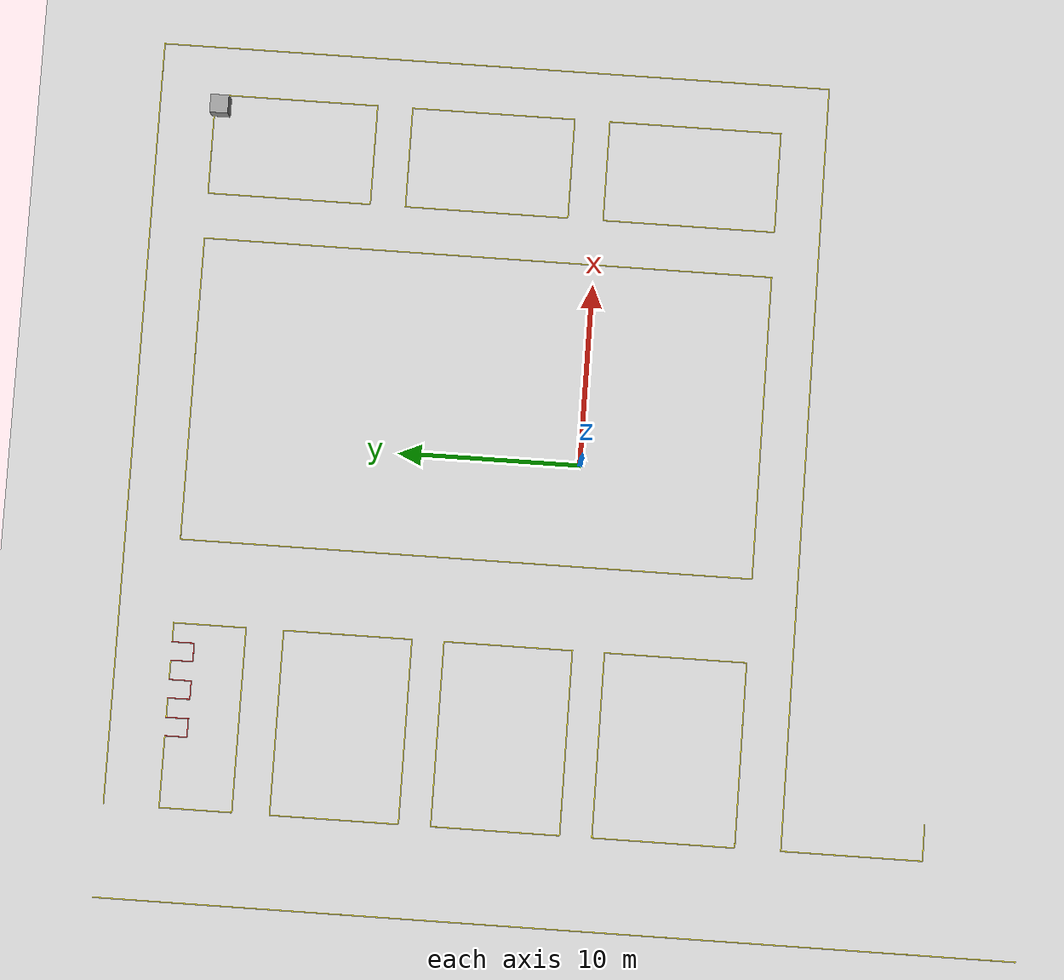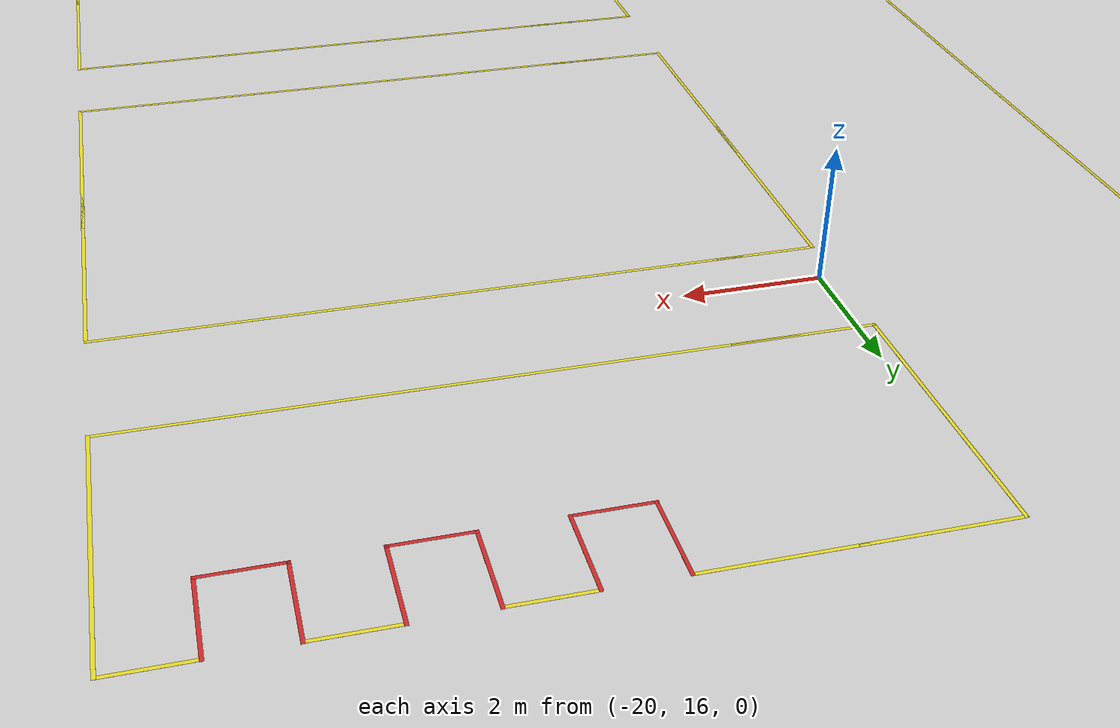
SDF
<sdf version="1.7">
 <world name="default">
  <light name="sun" type="directional">
   <pose>0 0 10 0 -0 0</pose>
   <diffuse>0.8 0.8 0.8 1</diffuse>
   <specular>0.2 0.2 0.2 1</specular>
   <attenuation>
    <range>1000</range>
    <constant>0.9</constant>
    <linear>0.01</linear>
    <quadratic>0.001</quadratic>
   </attenuation>
   <direction>-0.5 0.1 -0.9</direction>
   <spot><inner_angle>0</inner_angle><outer_angle>0</outer_angle><falloff>0</falloff></spot>
  </light>
  <model name="ground_plane">
   <static>1</static>
   <link name="link">
    <collision name="collision">
     <geometry><plane><normal>0 0 1</normal><size>100 100</size></plane></geometry>
     <surface>
      <contact><collide_bitmask>65535</collide_bitmask></contact>
      <friction><ode><mu>100</mu><mu2>50</mu2></ode></friction>
     </surface>
    </collision>
    <visual name="visual">
     <cast_shadows>0</cast_shadows>
     <geometry><plane><normal>0 0 1</normal><size>100 100</size></plane></geometry>
     <material>
      <script><uri>file://media/materials/scripts/gazebo.material</uri><name>Gazebo/Grey</name></script>
     </material>
    </visual>
   </link>
  </model>
  <gravity>0 0 -9.8</gravity>
  <magnetic_field>6e-06 2.3e-05 -4.2e-05</magnetic_field>
  <atmosphere type="adiabatic"/>
  <physics type="ode">
   <max_step_size>0.001</max_step_size>
   <real_time_factor>1</real_time_factor>
   <real_time_update_rate>1000</real_time_update_rate>
  </physics>
  <scene><ambient>0.4 0.4 0.4 1</ambient><background>0.7 0.7 0.7 1</background><shadows>1</shadows></scene>
  <spherical_coordinates>
   <surface_model>EARTH_WGS84</surface_model>
   <latitude_deg>0</latitude_deg>
   <longitude_deg>0</longitude_deg>
   <elevation>0</elevation>
   <heading_deg>0</heading_deg>
  </spherical_coordinates>
  <model name="line20m">
   <link name="link_0">
    <inertial>
     <mass>1</mass>
     <inertia>
      <ixx>0.166667</ixx>
      <ixy>0</ixy>
      <ixz>0</ixz>
      <iyy>0.166667</iyy>
      <iyz>0</iyz>
      <izz>0.166667</izz>
     </inertia>
    </inertial>
    <visual name="visual">
     <geometry><box><size>0.05 20 0.001</size></box></geometry>
     <material>
      <lighting>1</lighting>
      <script><uri>file://media/materials/scripts/gazebo.material</uri><name>Gazebo/Yellow</name></script>
     </material>
    </visual>
    <collision name="collision">
     <geometry><box><size>0.05 20 0.001</size></box></geometry>
     <surface>
      <friction>
       <ode><mu>1</mu><mu2>1</mu2><fdir1>0 0 0</fdir1><slip1>0</slip1><slip2>0</slip2></ode>
       <torsional>
        <coefficient>1</coefficient>
        <patch_radius>0</patch_radius>
        <surface_radius>0</surface_radius>
        <use_patch_radius>1</use_patch_radius>
        <ode><slip>0</slip></ode>
       </torsional>
      </friction>
      <bounce><restitution_coefficient>0</restitution_coefficient><threshold>1e+06</threshold></bounce>
      <contact>
       <collide_without_contact>0</collide_without_contact>
       <collide_without_contact_bitmask>1</collide_without_contact_bitmask>
       <collide_bitmask>1</collide_bitmask>
       <ode>
        <soft_cfm>0</soft_cfm>
        <soft_erp>0.2</soft_erp>
        <kp>1e+13</kp>
        <kd>1</kd>
        <max_vel>0.01</max_vel>
        <min_depth>0</min_depth>
       </ode>
       <bullet>
        <split_impulse>1</split_impulse>
        <split_impulse_penetration_threshold>-0.01</split_impulse_penetration_threshold>
        <soft_cfm>0</soft_cfm>
        <soft_erp>0.2</soft_erp>
        <kp>1e+13</kp>
        <kd>1</kd>
       </bullet>
      </contact>
     </surface>
    </collision>
   </link>
   <static>1</static>
   <pose>-25.125 14.7278 0.21 0 -0 0</pose>
  </model>
  <model name="line20m_0">
   <link name="link_0">
    <inertial>
     <mass>1</mass>
     <inertia>
      <ixx>0.166667</ixx>
      <ixy>0</ixy>
      <ixz>0</ixz>
      <iyy>0.166667</iyy>
      <iyz>0</iyz>
      <izz>0.166667</izz>
     </inertia>
    </inertial>
    <visual name="visual">
     <geometry><box><size>0.05 20 0.001</size></box></geometry>
     <material>
      <lighting>1</lighting>
      <script><uri>file://media/materials/scripts/gazebo.material</uri><name>Gazebo/Yellow</name></script>
     </material>
    </visual>
    <collision name="collision">
     <geometry><box><size>0.05 20 0.001</size></box></geometry>
     <surface>
      <friction>
       <ode><mu>1</mu><mu2>1</mu2><fdir1>0 0 0</fdir1><slip1>0</slip1><slip2>0</slip2></ode>
       <torsional>
        <coefficient>1</coefficient>
        <patch_radius>0</patch_radius>
        <surface_radius>0</surface_radius>
        <use_patch_radius>1</use_patch_radius>
        <ode><slip>0</slip></ode>
       </torsional>
      </friction>
      <bounce><restitution_coefficient>0</restitution_coefficient><threshold>1e+06</threshold></bounce>
      <contact>
       <collide_without_contact>0</collide_without_contact>
       <collide_without_contact_bitmask>1</collide_without_contact_bitmask>
       <collide_bitmask>1</collide_bitmask>
       <ode>
        <soft_cfm>0</soft_cfm>
        <soft_erp>0.2</soft_erp>
        <kp>1e+13</kp>
        <kd>1</kd>
        <max_vel>0.01</max_vel>
        <min_depth>0</min_depth>
       </ode>
       <bullet>
        <split_impulse>1</split_impulse>
        <split_impulse_penetration_threshold>-0.01</split_impulse_penetration_threshold>
        <soft_cfm>0</soft_cfm>
        <soft_erp>0.2</soft_erp>
        <kp>1e+13</kp>
        <kd>1</kd>
       </bullet>
      </contact>
     </surface>
    </collision>
   </link>
   <static>1</static>
   <pose>-25.125 -5.11082 0.21 0 -0 0</pose>
  </model>
  <model name="line9m">
   <link name="link_1">
    <inertial>
     <mass>1</mass>
     <inertia>
      <ixx>0.166667</ixx>
      <ixy>0</ixy>
      <ixz>0</ixz>
      <iyy>0.166667</iyy>
      <iyz>0</iyz>
      <izz>0.166667</izz>
     </inertia>
    </inertial>
    <visual name="visual">
     <geometry><box><size>9 0.05 0.001</size></box></geometry>
     <material>
      <lighting>1</lighting>
      <script><uri>file://media/materials/scripts/gazebo.material</uri><name>Gazebo/Yellow</name></script>
     </material>
    </visual>
    <collision name="collision">
     <geometry><box><size>9 0.05 0.001</size></box></geometry>
     <surface>
      <friction>
       <ode><mu>1</mu><mu2>1</mu2><fdir1>0 0 0</fdir1><slip1>0</slip1><slip2>0</slip2></ode>
       <torsional>
        <coefficient>1</coefficient>
        <patch_radius>0</patch_radius>
        <surface_radius>0</surface_radius>
        <use_patch_radius>1</use_patch_radius>
        <ode><slip>0</slip></ode>
       </torsional>
      </friction>
      <bounce><restitution_coefficient>0</restitution_coefficient><threshold>1e+06</threshold></bounce>
      <contact>
       <collide_without_contact>0</collide_without_contact>
       <collide_without_contact_bitmask>1</collide_without_contact_bitmask>
       <collide_bitmask>1</collide_bitmask>
       <ode>
        <soft_cfm>0</soft_cfm>
        <soft_erp>0.2</soft_erp>
        <kp>1e+13</kp>
        <kd>1</kd>
        <max_vel>0.01</max_vel>
        <min_depth>0</min_depth>
       </ode>
       <bullet>
        <split_impulse>1</split_impulse>
        <split_impulse_penetration_threshold>-0.01</split_impulse_penetration_threshold>
        <soft_cfm>0</soft_cfm>
        <soft_erp>0.2</soft_erp>
        <kp>1e+13</kp>
        <kd>1</kd>
       </bullet>
      </contact>
     </surface>
    </collision>
   </link>
   <static>1</static>
   <pose>-25.125 -18.8522 0.21 0 -0 1.571</pose>
  </model>
  <model name="line4m">
   <link name="link_3">
    <inertial>
     <mass>1</mass>
     <inertia>
      <ixx>0.166667</ixx>
      <ixy>0</ixy>
      <ixz>0</ixz>
      <iyy>0.166667</iyy>
      <iyz>0</iyz>
      <izz>0.166667</izz>
     </inertia>
    </inertial>
    <visual name="visual">
     <geometry><box><size>0.05 4 0.001</size></box></geometry>
     <material>
      <lighting>1</lighting>
      <script><uri>file://media/materials/scripts/gazebo.material</uri><name>Gazebo/Yellow</name></script>
     </material>
    </visual>
    <collision name="collision">
     <geometry><box><size>0.05 4 1e-06</size></box></geometry>
     <surface>
      <friction>
       <ode><mu>1</mu><mu2>1</mu2><fdir1>0 0 0</fdir1><slip1>0</slip1><slip2>0</slip2></ode>
       <torsional>
        <coefficient>1</coefficient>
        <patch_radius>0</patch_radius>
        <surface_radius>0</surface_radius>
        <use_patch_radius>1</use_patch_radius>
        <ode><slip>0</slip></ode>
       </torsional>
      </friction>
      <bounce><restitution_coefficient>0</restitution_coefficient><threshold>1e+06</threshold></bounce>
      <contact>
       <collide_without_contact>0</collide_without_contact>
       <collide_without_contact_bitmask>1</collide_without_contact_bitmask>
       <collide_bitmask>1</collide_bitmask>
       <ode>
        <soft_cfm>0</soft_cfm>
        <soft_erp>0.2</soft_erp>
        <kp>1e+13</kp>
        <kd>1</kd>
        <max_vel>0.01</max_vel>
        <min_depth>0</min_depth>
       </ode>
       <bullet>
        <split_impulse>1</split_impulse>
        <split_impulse_penetration_threshold>-0.01</split_impulse_penetration_threshold>
        <soft_cfm>0</soft_cfm>
        <soft_erp>0.2</soft_erp>
        <kp>1e+13</kp>
        <kd>1</kd>
       </bullet>
      </contact>
     </surface>
    </collision>
   </link>
   <static>1</static>
   <pose>-25.125 -23.3 0.21 0 -0 0</pose>
  </model>
  <model name="line22m">
   <link name="link_2">
    <inertial>
     <mass>1</mass>
     <inertia>
      <ixx>0.166667</ixx>
      <ixy>0</ixy>
      <ixz>0</ixz>
      <iyy>0.166667</iyy>
      <iyz>0</iyz>
      <izz>0.166667</izz>
     </inertia>
    </inertial>
    <visual name="visual">
     <geometry><box><size>0.05 22 0.001</size></box></geometry>
     <material>
      <lighting>1</lighting>
      <script><uri>file://media/materials/scripts/gazebo.material</uri><name>Gazebo/Yellow</name></script>
     </material>
    </visual>
    <collision name="collision">
     <geometry><box><size>0.05 22 0.001</size></box></geometry>
     <surface>
      <friction>
       <ode><mu>1</mu><mu2>1</mu2><fdir1>0 0 0</fdir1><slip1>0</slip1><slip2>0</slip2></ode>
       <torsional>
        <coefficient>1</coefficient>
        <patch_radius>0</patch_radius>
        <surface_radius>0</surface_radius>
        <use_patch_radius>1</use_patch_radius>
        <ode><slip>0</slip></ode>
       </torsional>
      </friction>
      <bounce><restitution_coefficient>0</restitution_coefficient><threshold>1e+06</threshold></bounce>
      <contact>
       <collide_without_contact>0</collide_without_contact>
       <collide_without_contact_bitmask>1</collide_without_contact_bitmask>
       <collide_bitmask>1</collide_bitmask>
       <ode>
        <soft_cfm>0</soft_cfm>
        <soft_erp>0.2</soft_erp>
        <kp>1e+13</kp>
        <kd>1</kd>
        <max_vel>0.01</max_vel>
        <min_depth>0</min_depth>
       </ode>
       <bullet>
        <split_impulse>1</split_impulse>
        <split_impulse_penetration_threshold>-0.01</split_impulse_penetration_threshold>
        <soft_cfm>0</soft_cfm>
        <soft_erp>0.2</soft_erp>
        <kp>1e+13</kp>
        <kd>1</kd>
       </bullet>
      </contact>
     </surface>
    </collision>
   </link>
   <static>1</static>
   <pose>-9.1 24.525 0.21 0 -0 1.571</pose>
  </model>
  <model name="line18m">
   <link name="link_1">
    <inertial>
     <mass>1</mass>
     <inertia>
      <ixx>0.166667</ixx>
      <ixy>0</ixy>
      <ixz>0</ixz>
      <iyy>0.166667</iyy>
      <iyz>0</iyz>
      <izz>0.166667</izz>
     </inertia>
    </inertial>
    <visual name="visual">
     <geometry><box><size>0.05 18 0.001</size></box></geometry>
     <material>
      <lighting>1</lighting>
      <script><uri>file://media/materials/scripts/gazebo.material</uri><name>Gazebo/Yellow</name></script>
     </material>
    </visual>
    <collision name="collision">
     <geometry><box><size>0.05 18 0.001</size></box></geometry>
     <surface>
      <friction>
       <ode><mu>1</mu><mu2>1</mu2><fdir1>0 0 0</fdir1><slip1>0</slip1><slip2>0</slip2></ode>
       <torsional>
        <coefficient>1</coefficient>
        <patch_radius>0</patch_radius>
        <surface_radius>0</surface_radius>
        <use_patch_radius>1</use_patch_radius>
        <ode><slip>0</slip></ode>
       </torsional>
      </friction>
      <bounce><restitution_coefficient>0</restitution_coefficient><threshold>1e+06</threshold></bounce>
      <contact>
       <collide_without_contact>0</collide_without_contact>
       <collide_without_contact_bitmask>1</collide_without_contact_bitmask>
       <collide_bitmask>1</collide_bitmask>
       <ode>
        <soft_cfm>0</soft_cfm>
        <soft_erp>0.2</soft_erp>
        <kp>1e+13</kp>
        <kd>1</kd>
        <max_vel>0.01</max_vel>
        <min_depth>0</min_depth>
       </ode>
       <bullet>
        <split_impulse>1</split_impulse>
        <split_impulse_penetration_threshold>-0.01</split_impulse_penetration_threshold>
        <soft_cfm>0</soft_cfm>
        <soft_erp>0.2</soft_erp>
        <kp>1e+13</kp>
        <kd>1</kd>
       </bullet>
      </contact>
     </surface>
    </collision>
   </link>
   <static>1</static>
   <pose>10.8 24.525 0.21 0 -0 1.571</pose>
  </model>
  <model name="line3200cm">
   <link name="link_4">
    <inertial>
     <mass>1</mass>
     <inertia>
      <ixx>0.166667</ixx>
      <ixy>0</ixy>
      <ixz>0</ixz>
      <iyy>0.166667</iyy>
      <iyz>0</iyz>
      <izz>0.166667</izz>
     </inertia>
    </inertial>
    <visual name="visual">
     <pose>0 0 0 0 -0 1.5708</pose>
     <geometry><box><size>0.05 32 0.001</size></box></geometry>
     <material>
      <lighting>1</lighting>
      <script><uri>file://media/materials/scripts/gazebo.material</uri><name>Gazebo/Yellow</name></script>
     </material>
    </visual>
    <collision name="collision">
     <pose>0 0 0 0 -0 1.5708</pose>
     <geometry><box><size>0.05 32 1e-05</size></box></geometry>
     <surface>
      <friction>
       <ode><mu>1</mu><mu2>1</mu2><fdir1>0 0 0</fdir1><slip1>0</slip1><slip2>0</slip2></ode>
       <torsional>
        <coefficient>1</coefficient>
        <patch_radius>0</patch_radius>
        <surface_radius>0</surface_radius>
        <use_patch_radius>1</use_patch_radius>
        <ode><slip>0</slip></ode>
       </torsional>
      </friction>
      <bounce><restitution_coefficient>0</restitution_coefficient><threshold>1e+06</threshold></bounce>
      <contact>
       <collide_without_contact>0</collide_without_contact>
       <collide_without_contact_bitmask>1</collide_without_contact_bitmask>
       <collide_bitmask>1</collide_bitmask>
       <ode>
        <soft_cfm>0</soft_cfm>
        <soft_erp>0.2</soft_erp>
        <kp>1e+13</kp>
        <kd>1</kd>
        <max_vel>0.01</max_vel>
        <min_depth>0</min_depth>
       </ode>
       <bullet>
        <split_impulse>1</split_impulse>
        <split_impulse_penetration_threshold>-0.01</split_impulse_penetration_threshold>
        <soft_cfm>0</soft_cfm>
        <soft_erp>0.2</soft_erp>
        <kp>1e+13</kp>
        <kd>1</kd>
       </bullet>
      </contact>
     </surface>
    </collision>
   </link>
   <static>1</static>
   <pose>21.75 8.5 0.21 0 -0 1.571</pose>
  </model>
  <model name="line2m_1">
   <link name="link_0">
    <inertial>
     <mass>1</mass>
     <inertia>
      <ixx>0.166667</ixx>
      <ixy>0</ixy>
      <ixz>0</ixz>
      <iyy>0.166667</iyy>
      <iyz>0</iyz>
      <izz>0.166667</izz>
     </inertia>
    </inertial>
    <visual name="visual">
     <geometry><box><size>2 0.05 0.001</size></box></geometry>
     <material>
      <lighting>1</lighting>
      <script><uri>file://media/materials/scripts/gazebo.material</uri><name>Gazebo/Yellow</name></script>
     </material>
    </visual>
    <collision name="collision">
     <geometry><box><size>2 0.05 1e-05</size></box></geometry>
     <surface>
      <friction>
       <ode><mu>1</mu><mu2>1</mu2><fdir1>0 0 0</fdir1><slip1>0</slip1><slip2>0</slip2></ode>
       <torsional>
        <coefficient>1</coefficient>
        <patch_radius>0</patch_radius>
        <surface_radius>0</surface_radius>
        <use_patch_radius>1</use_patch_radius>
        <ode><slip>0</slip></ode>
       </torsional>
      </friction>
      <bounce><restitution_coefficient>0</restitution_coefficient><threshold>1e+06</threshold></bounce>
      <contact>
       <collide_without_contact>0</collide_without_contact>
       <collide_without_contact_bitmask>1</collide_without_contact_bitmask>
       <collide_bitmask>1</collide_bitmask>
       <ode>
        <soft_cfm>0</soft_cfm>
        <soft_erp>0.2</soft_erp>
        <kp>1e+13</kp>
        <kd>1</kd>
        <max_vel>0.01</max_vel>
        <min_depth>0</min_depth>
       </ode>
       <bullet>
        <split_impulse>1</split_impulse>
        <split_impulse_penetration_threshold>-0.01</split_impulse_penetration_threshold>
        <soft_cfm>0</soft_cfm>
        <soft_erp>0.2</soft_erp>
        <kp>1e+13</kp>
        <kd>1</kd>
       </bullet>
      </contact>
     </surface>
    </collision>
   </link>
   <static>1</static>
   <pose>20.77 24.525 0.21 0 -0 0</pose>
  </model>
  <model name="line4m_0">
   <link name="link_3">
    <inertial>
     <mass>1</mass>
     <inertia>
      <ixx>0.166667</ixx>
      <ixy>0</ixy>
      <ixz>0</ixz>
      <iyy>0.166667</iyy>
      <iyz>0</iyz>
      <izz>0.166667</izz>
     </inertia>
    </inertial>
    <visual name="visual">
     <geometry><box><size>0.05 4 0.001</size></box></geometry>
     <material>
      <lighting>1</lighting>
      <script><uri>file://media/materials/scripts/gazebo.material</uri><name>Gazebo/Yellow</name></script>
     </material>
    </visual>
    <collision name="collision">
     <geometry><box><size>0.05 4 1e-06</size></box></geometry>
     <surface>
      <friction>
       <ode><mu>1</mu><mu2>1</mu2><fdir1>0 0 0</fdir1><slip1>0</slip1><slip2>0</slip2></ode>
       <torsional>
        <coefficient>1</coefficient>
        <patch_radius>0</patch_radius>
        <surface_radius>0</surface_radius>
        <use_patch_radius>1</use_patch_radius>
        <ode><slip>0</slip></ode>
       </torsional>
      </friction>
      <bounce><restitution_coefficient>0</restitution_coefficient><threshold>1e+06</threshold></bounce>
      <contact>
       <collide_without_contact>0</collide_without_contact>
       <collide_without_contact_bitmask>1</collide_without_contact_bitmask>
       <collide_bitmask>1</collide_bitmask>
       <ode>
        <soft_cfm>0</soft_cfm>
        <soft_erp>0.2</soft_erp>
        <kp>1e+13</kp>
        <kd>1</kd>
        <max_vel>0.01</max_vel>
        <min_depth>0</min_depth>
       </ode>
       <bullet>
        <split_impulse>1</split_impulse>
        <split_impulse_penetration_threshold>-0.01</split_impulse_penetration_threshold>
        <soft_cfm>0</soft_cfm>
        <soft_erp>0.2</soft_erp>
        <kp>1e+13</kp>
        <kd>1</kd>
       </bullet>
      </contact>
     </surface>
    </collision>
   </link>
   <static>1</static>
   <pose>21.75 -9.42976 0.21 0 -0 0</pose>
  </model>
  <model name="line2m_2">
   <link name="link_0">
    <inertial>
     <mass>1</mass>
     <inertia>
      <ixx>0.166667</ixx>
      <ixy>0</ixy>
      <ixz>0</ixz>
      <iyy>0.166667</iyy>
      <iyz>0</iyz>
      <izz>0.166667</izz>
     </inertia>
    </inertial>
    <visual name="visual">
     <geometry><box><size>2 0.05 0.001</size></box></geometry>
     <material>
      <lighting>1</lighting>
      <script><uri>file://media/materials/scripts/gazebo.material</uri><name>Gazebo/Yellow</name></script>
     </material>
    </visual>
    <collision name="collision">
     <geometry><box><size>2 0.05 1e-05</size></box></geometry>
     <surface>
      <friction>
       <ode><mu>1</mu><mu2>1</mu2><fdir1>0 0 0</fdir1><slip1>0</slip1><slip2>0</slip2></ode>
       <torsional>
        <coefficient>1</coefficient>
        <patch_radius>0</patch_radius>
        <surface_radius>0</surface_radius>
        <use_patch_radius>1</use_patch_radius>
        <ode><slip>0</slip></ode>
       </torsional>
      </friction>
      <bounce><restitution_coefficient>0</restitution_coefficient><threshold>1e+06</threshold></bounce>
      <contact>
       <collide_without_contact>0</collide_without_contact>
       <collide_without_contact_bitmask>1</collide_without_contact_bitmask>
       <collide_bitmask>1</collide_bitmask>
       <ode>
        <soft_cfm>0</soft_cfm>
        <soft_erp>0.2</soft_erp>
        <kp>1e+13</kp>
        <kd>1</kd>
        <max_vel>0.01</max_vel>
        <min_depth>0</min_depth>
       </ode>
       <bullet>
        <split_impulse>1</split_impulse>
        <split_impulse_penetration_threshold>-0.01</split_impulse_penetration_threshold>
        <soft_cfm>0</soft_cfm>
        <soft_erp>0.2</soft_erp>
        <kp>1e+13</kp>
        <kd>1</kd>
       </bullet>
      </contact>
     </surface>
    </collision>
   </link>
   <static>1</static>
   <pose>21.7501 -11.2686 0.21 0 -0 1.571</pose>
  </model>
  <model name="line9m_4">
   <link name="link_1">
    <inertial>
     <mass>1</mass>
     <inertia>
      <ixx>0.166667</ixx>
      <ixy>0</ixy>
      <ixz>0</ixz>
      <iyy>0.166667</iyy>
      <iyz>0</iyz>
      <izz>0.166667</izz>
     </inertia>
    </inertial>
    <visual name="visual">
     <geometry><box><size>9 0.05 0.001</size></box></geometry>
     <material>
      <lighting>1</lighting>
      <script><uri>file://media/materials/scripts/gazebo.material</uri><name>Gazebo/Yellow</name></script>
     </material>
    </visual>
    <collision name="collision">
     <geometry><box><size>9 0.05 0.001</size></box></geometry>
     <surface>
      <friction>
       <ode><mu>1</mu><mu2>1</mu2><fdir1>0 0 0</fdir1><slip1>0</slip1><slip2>0</slip2></ode>
       <torsional>
        <coefficient>1</coefficient>
        <patch_radius>0</patch_radius>
        <surface_radius>0</surface_radius>
        <use_patch_radius>1</use_patch_radius>
        <ode><slip>0</slip></ode>
       </torsional>
      </friction>
      <bounce><restitution_coefficient>0</restitution_coefficient><threshold>1e+06</threshold></bounce>
      <contact>
       <collide_without_contact>0</collide_without_contact>
       <collide_without_contact_bitmask>1</collide_without_contact_bitmask>
       <collide_bitmask>1</collide_bitmask>
       <ode>
        <soft_cfm>0</soft_cfm>
        <soft_erp>0.2</soft_erp>
        <kp>1e+13</kp>
        <kd>1</kd>
        <max_vel>0.01</max_vel>
        <min_depth>0</min_depth>
       </ode>
       <bullet>
        <split_impulse>1</split_impulse>
        <split_impulse_penetration_threshold>-0.01</split_impulse_penetration_threshold>
        <soft_cfm>0</soft_cfm>
        <soft_erp>0.2</soft_erp>
        <kp>1e+13</kp>
        <kd>1</kd>
       </bullet>
      </contact>
     </surface>
    </collision>
   </link>
   <static>1</static>
   <pose>17.275 -12.25 0.21 0 -0 0</pose>
  </model>
  <model name="line3200cm_0">
   <link name="link_4">
    <inertial>
     <mass>1</mass>
     <inertia>
      <ixx>0.166667</ixx>
      <ixy>0</ixy>
      <ixz>0</ixz>
      <iyy>0.166667</iyy>
      <iyz>0</iyz>
      <izz>0.166667</izz>
     </inertia>
    </inertial>
    <visual name="visual">
     <pose>0 0 0 0 -0 1.5708</pose>
     <geometry><box><size>0.05 32 0.001</size></box></geometry>
     <material>
      <lighting>1</lighting>
      <script><uri>file://media/materials/scripts/gazebo.material</uri><name>Gazebo/Yellow</name></script>
     </material>
    </visual>
    <collision name="collision">
     <pose>0 0 0 0 -0 1.5708</pose>
     <geometry><box><size>0.05 32 1e-05</size></box></geometry>
     <surface>
      <friction>
       <ode><mu>1</mu><mu2>1</mu2><fdir1>0 0 0</fdir1><slip1>0</slip1><slip2>0</slip2></ode>
       <torsional>
        <coefficient>1</coefficient>
        <patch_radius>0</patch_radius>
        <surface_radius>0</surface_radius>
        <use_patch_radius>1</use_patch_radius>
        <ode><slip>0</slip></ode>
       </torsional>
      </friction>
      <bounce><restitution_coefficient>0</restitution_coefficient><threshold>1e+06</threshold></bounce>
      <contact>
       <collide_without_contact>0</collide_without_contact>
       <collide_without_contact_bitmask>1</collide_without_contact_bitmask>
       <collide_bitmask>1</collide_bitmask>
       <ode>
        <soft_cfm>0</soft_cfm>
        <soft_erp>0.2</soft_erp>
        <kp>1e+13</kp>
        <kd>1</kd>
        <max_vel>0.01</max_vel>
        <min_depth>0</min_depth>
       </ode>
       <bullet>
        <split_impulse>1</split_impulse>
        <split_impulse_penetration_threshold>-0.01</split_impulse_penetration_threshold>
        <soft_cfm>0</soft_cfm>
        <soft_erp>0.2</soft_erp>
        <kp>1e+13</kp>
        <kd>1</kd>
       </bullet>
      </contact>
     </surface>
    </collision>
   </link>
   <static>1</static>
   <pose>-2.1 -12.25 0.21 0 -0 0</pose>
  </model>
  <model name="line4m_1">
   <link name="link_3">
    <inertial>
     <mass>1</mass>
     <inertia>
      <ixx>0.166667</ixx>
      <ixy>0</ixy>
      <ixz>0</ixz>
      <iyy>0.166667</iyy>
      <iyz>0</iyz>
      <izz>0.166667</izz>
     </inertia>
    </inertial>
    <visual name="visual">
     <geometry><box><size>0.05 4 0.001</size></box></geometry>
     <material>
      <lighting>1</lighting>
      <script><uri>file://media/materials/scripts/gazebo.material</uri><name>Gazebo/Yellow</name></script>
     </material>
    </visual>
    <collision name="collision">
     <geometry><box><size>0.05 4 1e-06</size></box></geometry>
     <surface>
      <friction>
       <ode><mu>1</mu><mu2>1</mu2><fdir1>0 0 0</fdir1><slip1>0</slip1><slip2>0</slip2></ode>
       <torsional>
        <coefficient>1</coefficient>
        <patch_radius>0</patch_radius>
        <surface_radius>0</surface_radius>
        <use_patch_radius>1</use_patch_radius>
        <ode><slip>0</slip></ode>
       </torsional>
      </friction>
      <bounce><restitution_coefficient>0</restitution_coefficient><threshold>1e+06</threshold></bounce>
      <contact>
       <collide_without_contact>0</collide_without_contact>
       <collide_without_contact_bitmask>1</collide_without_contact_bitmask>
       <collide_bitmask>1</collide_bitmask>
       <ode>
        <soft_cfm>0</soft_cfm>
        <soft_erp>0.2</soft_erp>
        <kp>1e+13</kp>
        <kd>1</kd>
        <max_vel>0.01</max_vel>
        <min_depth>0</min_depth>
       </ode>
       <bullet>
        <split_impulse>1</split_impulse>
        <split_impulse_penetration_threshold>-0.01</split_impulse_penetration_threshold>
        <soft_cfm>0</soft_cfm>
        <soft_erp>0.2</soft_erp>
        <kp>1e+13</kp>
        <kd>1</kd>
       </bullet>
      </contact>
     </surface>
    </collision>
   </link>
   <static>1</static>
   <pose>-20.075 -14.225 0.21 0 -0 0</pose>
  </model>
  <model name="line4m_2">
   <link name="link_3">
    <inertial>
     <mass>1</mass>
     <inertia>
      <ixx>0.166667</ixx>
      <ixy>0</ixy>
      <ixz>0</ixz>
      <iyy>0.166667</iyy>
      <iyz>0</iyz>
      <izz>0.166667</izz>
     </inertia>
    </inertial>
    <visual name="visual">
     <geometry><box><size>0.05 4 0.001</size></box></geometry>
     <material>
      <lighting>1</lighting>
      <script><uri>file://media/materials/scripts/gazebo.material</uri><name>Gazebo/Yellow</name></script>
     </material>
    </visual>
    <collision name="collision">
     <geometry><box><size>0.05 4 1e-06</size></box></geometry>
     <surface>
      <friction>
       <ode><mu>1</mu><mu2>1</mu2><fdir1>0 0 0</fdir1><slip1>0</slip1><slip2>0</slip2></ode>
       <torsional>
        <coefficient>1</coefficient>
        <patch_radius>0</patch_radius>
        <surface_radius>0</surface_radius>
        <use_patch_radius>1</use_patch_radius>
        <ode><slip>0</slip></ode>
       </torsional>
      </friction>
      <bounce><restitution_coefficient>0</restitution_coefficient><threshold>1e+06</threshold></bounce>
      <contact>
       <collide_without_contact>0</collide_without_contact>
       <collide_without_contact_bitmask>1</collide_without_contact_bitmask>
       <collide_bitmask>1</collide_bitmask>
       <ode>
        <soft_cfm>0</soft_cfm>
        <soft_erp>0.2</soft_erp>
        <kp>1e+13</kp>
        <kd>1</kd>
        <max_vel>0.01</max_vel>
        <min_depth>0</min_depth>
       </ode>
       <bullet>
        <split_impulse>1</split_impulse>
        <split_impulse_penetration_threshold>-0.01</split_impulse_penetration_threshold>
        <soft_cfm>0</soft_cfm>
        <soft_erp>0.2</soft_erp>
        <kp>1e+13</kp>
        <kd>1</kd>
       </bullet>
      </contact>
     </surface>
    </collision>
   </link>
   <static>1</static>
   <pose>-20.075 -17.9393 0.21 0 -0 0</pose>
  </model>
  <model name="oneDemoParking">
   <link name="link_1">
    <inertial>
     <mass>1</mass>
     <inertia>
      <ixx>0.166667</ixx>
      <ixy>0</ixy>
      <ixz>0</ixz>
      <iyy>0.166667</iyy>
      <iyz>0</iyz>
      <izz>0.166667</izz>
     </inertia>
    </inertial>
    <visual name="visual">
     <pose>-0.5 0 0 0 -0 0</pose>
     <geometry><box><size>0.05 1.26 0.001</size></box></geometry>
     <material>
      <lighting>1</lighting>
      <script><uri>file://media/materials/scripts/gazebo.material</uri><name>Gazebo/Red</name></script>
      <shader type="pixel"><normal_map>__default__</normal_map></shader>
     </material>
    </visual>
    <visual name="ModelPreview_3::link_1::visual_3">
     <pose>0 0.605 0 0 -0 0</pose>
     <geometry><box><size>1.05 0.05 0.001</size></box></geometry>
     <material>
      <lighting>1</lighting>
      <script><uri>file://media/materials/scripts/gazebo.material</uri><name>Gazebo/Red</name></script>
      <shader type="pixel"><normal_map>__default__</normal_map></shader>
     </material>
    </visual>
    <visual name="ModelPreview_3::link_1::visual_2">
     <pose>0.5 0 0 0 -0 0</pose>
     <geometry><box><size>0.05 1.26 0.001</size></box></geometry>
     <material>
      <lighting>1</lighting>
      <script><uri>file://media/materials/scripts/gazebo.material</uri><name>Gazebo/Red</name></script>
      <shader type="pixel"><normal_map>__default__</normal_map></shader>
     </material>
    </visual>
    <collision name="collision">
     <pose>-0.5 0 0 0 -0 0</pose>
     <geometry><box><size>0.05 1.26 0.001</size></box></geometry>
     <surface>
      <friction>
       <ode><mu>1</mu><mu2>1</mu2><fdir1>0 0 0</fdir1><slip1>0</slip1><slip2>0</slip2></ode>
       <torsional>
        <coefficient>1</coefficient>
        <patch_radius>0</patch_radius>
        <surface_radius>0</surface_radius>
        <use_patch_radius>1</use_patch_radius>
        <ode><slip>0</slip></ode>
       </torsional>
      </friction>
      <bounce><restitution_coefficient>0</restitution_coefficient><threshold>1e+06</threshold></bounce>
      <contact>
       <collide_without_contact>0</collide_without_contact>
       <collide_without_contact_bitmask>1</collide_without_contact_bitmask>
       <collide_bitmask>1</collide_bitmask>
       <ode>
        <soft_cfm>0</soft_cfm>
        <soft_erp>0.2</soft_erp>
        <kp>1e+13</kp>
        <kd>1</kd>
        <max_vel>0.01</max_vel>
        <min_depth>0</min_depth>
       </ode>
       <bullet>
        <split_impulse>1</split_impulse>
        <split_impulse_penetration_threshold>-0.01</split_impulse_penetration_threshold>
        <soft_cfm>0</soft_cfm>
        <soft_erp>0.2</soft_erp>
        <kp>1e+13</kp>
        <kd>1</kd>
       </bullet>
      </contact>
     </surface>
    </collision>
    <collision name="collision_1">
     <pose>0.5 0 0 0 -0 0</pose>
     <geometry><box><size>0.05 1.26 0.001</size></box></geometry>
     <surface>
      <friction>
       <ode><mu>1</mu><mu2>1</mu2><fdir1>0 0 0</fdir1><slip1>0</slip1><slip2>0</slip2></ode>
       <torsional>
        <coefficient>1</coefficient>
        <patch_radius>0</patch_radius>
        <surface_radius>0</surface_radius>
        <use_patch_radius>1</use_patch_radius>
        <ode><slip>0</slip></ode>
       </torsional>
      </friction>
      <bounce><restitution_coefficient>0</restitution_coefficient><threshold>1e+06</threshold></bounce>
      <contact>
       <collide_without_contact>0</collide_without_contact>
       <collide_without_contact_bitmask>1</collide_without_contact_bitmask>
       <collide_bitmask>1</collide_bitmask>
       <ode>
        <soft_cfm>0</soft_cfm>
        <soft_erp>0.2</soft_erp>
        <kp>1e+13</kp>
        <kd>1</kd>
        <max_vel>0.01</max_vel>
        <min_depth>0</min_depth>
       </ode>
       <bullet>
        <split_impulse>1</split_impulse>
        <split_impulse_penetration_threshold>-0.01</split_impulse_penetration_threshold>
        <soft_cfm>0</soft_cfm>
        <soft_erp>0.2</soft_erp>
        <kp>1e+13</kp>
        <kd>1</kd>
       </bullet>
      </contact>
     </surface>
    </collision>
    <collision name="collision_2">
     <pose>0 0.605 0 0 -0 0</pose>
     <geometry><box><size>1.05 0.05 0.001</size></box></geometry>
     <surface>
      <friction>
       <ode><mu>1</mu><mu2>1</mu2><fdir1>0 0 0</fdir1><slip1>0</slip1><slip2>0</slip2></ode>
       <torsional>
        <coefficient>1</coefficient>
        <patch_radius>0</patch_radius>
        <surface_radius>0</surface_radius>
        <use_patch_radius>1</use_patch_radius>
        <ode><slip>0</slip></ode>
       </torsional>
      </friction>
      <bounce><restitution_coefficient>0</restitution_coefficient><threshold>1e+06</threshold></bounce>
      <contact>
       <collide_without_contact>0</collide_without_contact>
       <collide_without_contact_bitmask>1</collide_without_contact_bitmask>
       <collide_bitmask>1</collide_bitmask>
       <ode>
        <soft_cfm>0</soft_cfm>
        <soft_erp>0.2</soft_erp>
        <kp>1e+13</kp>
        <kd>1</kd>
        <max_vel>0.01</max_vel>
        <min_depth>0</min_depth>
       </ode>
       <bullet>
        <split_impulse>1</split_impulse>
        <split_impulse_penetration_threshold>-0.01</split_impulse_penetration_threshold>
        <soft_cfm>0</soft_cfm>
        <soft_erp>0.2</soft_erp>
        <kp>1e+13</kp>
        <kd>1</kd>
       </bullet>
      </contact>
     </surface>
    </collision>
    <collision name="collision_3">
     <pose>-0 -0.4 0 0 -0 0</pose>
     <geometry><cylinder><radius>0.2</radius><length>0.001</length></cylinder></geometry>
     <surface>
      <friction>
       <ode><mu>1</mu><mu2>1</mu2><fdir1>0 0 0</fdir1><slip1>0</slip1><slip2>0</slip2></ode>
       <torsional>
        <coefficient>1</coefficient>
        <patch_radius>0</patch_radius>
        <surface_radius>0</surface_radius>
        <use_patch_radius>1</use_patch_radius>
        <ode><slip>0</slip></ode>
       </torsional>
      </friction>
      <bounce><restitution_coefficient>0</restitution_coefficient><threshold>1e+06</threshold></bounce>
      <contact>
       <collide_without_contact>0</collide_without_contact>
       <collide_without_contact_bitmask>1</collide_without_contact_bitmask>
       <collide_bitmask>1</collide_bitmask>
       <ode>
        <soft_cfm>0</soft_cfm>
        <soft_erp>0.2</soft_erp>
        <kp>1e+13</kp>
        <kd>1</kd>
        <max_vel>0.01</max_vel>
        <min_depth>0</min_depth>
       </ode>
       <bullet>
        <split_impulse>1</split_impulse>
        <split_impulse_penetration_threshold>-0.01</split_impulse_penetration_threshold>
        <soft_cfm>0</soft_cfm>
        <soft_erp>0.2</soft_erp>
        <kp>1e+13</kp>
        <kd>1</kd>
       </bullet>
      </contact>
     </surface>
    </collision>
   </link>
   <static>1</static>
   <pose>-11.6 20.9 0.21 0 0 -3.14119</pose>
  </model>
  <model name="oneDemoParking_0">
   <link name="link_1">
    <inertial>
     <mass>1</mass>
     <inertia>
      <ixx>0.166667</ixx>
      <ixy>0</ixy>
      <ixz>0</ixz>
      <iyy>0.166667</iyy>
      <iyz>0</iyz>
      <izz>0.166667</izz>
     </inertia>
    </inertial>
    <visual name="visual">
     <pose>-0.5 0 0 0 -0 0</pose>
     <geometry><box><size>0.05 1.26 0.001</size></box></geometry>
     <material>
      <lighting>1</lighting>
      <script><uri>file://media/materials/scripts/gazebo.material</uri><name>Gazebo/Red</name></script>
      <shader type="pixel"><normal_map>__default__</normal_map></shader>
     </material>
    </visual>
    <visual name="ModelPreview_3::link_1::visual_3">
     <pose>0 0.605 0 0 -0 0</pose>
     <geometry><box><size>1.05 0.05 0.001</size></box></geometry>
     <material>
      <lighting>1</lighting>
      <script><uri>file://media/materials/scripts/gazebo.material</uri><name>Gazebo/Red</name></script>
      <shader type="pixel"><normal_map>__default__</normal_map></shader>
     </material>
    </visual>
    <visual name="ModelPreview_3::link_1::visual_2">
     <pose>0.5 0 0 0 -0 0</pose>
     <geometry><box><size>0.05 1.26 0.001</size></box></geometry>
     <material>
      <lighting>1</lighting>
      <script><uri>file://media/materials/scripts/gazebo.material</uri><name>Gazebo/Red</name></script>
      <shader type="pixel"><normal_map>__default__</normal_map></shader>
     </material>
    </visual>
    <collision name="collision">
     <pose>-0.5 0 0 0 -0 0</pose>
     <geometry><box><size>0.05 1.26 0.001</size></box></geometry>
     <surface>
      <friction>
       <ode><mu>1</mu><mu2>1</mu2><fdir1>0 0 0</fdir1><slip1>0</slip1><slip2>0</slip2></ode>
       <torsional>
        <coefficient>1</coefficient>
        <patch_radius>0</patch_radius>
        <surface_radius>0</surface_radius>
        <use_patch_radius>1</use_patch_radius>
        <ode><slip>0</slip></ode>
       </torsional>
      </friction>
      <bounce><restitution_coefficient>0</restitution_coefficient><threshold>1e+06</threshold></bounce>
      <contact>
       <collide_without_contact>0</collide_without_contact>
       <collide_without_contact_bitmask>1</collide_without_contact_bitmask>
       <collide_bitmask>1</collide_bitmask>
       <ode>
        <soft_cfm>0</soft_cfm>
        <soft_erp>0.2</soft_erp>
        <kp>1e+13</kp>
        <kd>1</kd>
        <max_vel>0.01</max_vel>
        <min_depth>0</min_depth>
       </ode>
       <bullet>
        <split_impulse>1</split_impulse>
        <split_impulse_penetration_threshold>-0.01</split_impulse_penetration_threshold>
        <soft_cfm>0</soft_cfm>
        <soft_erp>0.2</soft_erp>
        <kp>1e+13</kp>
        <kd>1</kd>
       </bullet>
      </contact>
     </surface>
    </collision>
    <collision name="collision_1">
     <pose>0.5 0 0 0 -0 0</pose>
     <geometry><box><size>0.05 1.26 0.001</size></box></geometry>
     <surface>
      <friction>
       <ode><mu>1</mu><mu2>1</mu2><fdir1>0 0 0</fdir1><slip1>0</slip1><slip2>0</slip2></ode>
       <torsional>
        <coefficient>1</coefficient>
        <patch_radius>0</patch_radius>
        <surface_radius>0</surface_radius>
        <use_patch_radius>1</use_patch_radius>
        <ode><slip>0</slip></ode>
       </torsional>
      </friction>
      <bounce><restitution_coefficient>0</restitution_coefficient><threshold>1e+06</threshold></bounce>
      <contact>
       <collide_without_contact>0</collide_without_contact>
       <collide_without_contact_bitmask>1</collide_without_contact_bitmask>
       <collide_bitmask>1</collide_bitmask>
       <ode>
        <soft_cfm>0</soft_cfm>
        <soft_erp>0.2</soft_erp>
        <kp>1e+13</kp>
        <kd>1</kd>
        <max_vel>0.01</max_vel>
        <min_depth>0</min_depth>
       </ode>
       <bullet>
        <split_impulse>1</split_impulse>
        <split_impulse_penetration_threshold>-0.01</split_impulse_penetration_threshold>
        <soft_cfm>0</soft_cfm>
        <soft_erp>0.2</soft_erp>
        <kp>1e+13</kp>
        <kd>1</kd>
       </bullet>
      </contact>
     </surface>
    </collision>
    <collision name="collision_2">
     <pose>0 0.605 0 0 -0 0</pose>
     <geometry><box><size>1.05 0.05 0.001</size></box></geometry>
     <surface>
      <friction>
       <ode><mu>1</mu><mu2>1</mu2><fdir1>0 0 0</fdir1><slip1>0</slip1><slip2>0</slip2></ode>
       <torsional>
        <coefficient>1</coefficient>
        <patch_radius>0</patch_radius>
        <surface_radius>0</surface_radius>
        <use_patch_radius>1</use_patch_radius>
        <ode><slip>0</slip></ode>
       </torsional>
      </friction>
      <bounce><restitution_coefficient>0</restitution_coefficient><threshold>1e+06</threshold></bounce>
      <contact>
       <collide_without_contact>0</collide_without_contact>
       <collide_without_contact_bitmask>1</collide_without_contact_bitmask>
       <collide_bitmask>1</collide_bitmask>
       <ode>
        <soft_cfm>0</soft_cfm>
        <soft_erp>0.2</soft_erp>
        <kp>1e+13</kp>
        <kd>1</kd>
        <max_vel>0.01</max_vel>
        <min_depth>0</min_depth>
       </ode>
       <bullet>
        <split_impulse>1</split_impulse>
        <split_impulse_penetration_threshold>-0.01</split_impulse_penetration_threshold>
        <soft_cfm>0</soft_cfm>
        <soft_erp>0.2</soft_erp>
        <kp>1e+13</kp>
        <kd>1</kd>
       </bullet>
      </contact>
     </surface>
    </collision>
    <collision name="collision_3">
     <pose>-0 -0.4 0 0 -0 0</pose>
     <geometry><cylinder><radius>0.2</radius><length>0.001</length></cylinder></geometry>
     <surface>
      <friction>
       <ode><mu>1</mu><mu2>1</mu2><fdir1>0 0 0</fdir1><slip1>0</slip1><slip2>0</slip2></ode>
       <torsional>
        <coefficient>1</coefficient>
        <patch_radius>0</patch_radius>
        <surface_radius>0</surface_radius>
        <use_patch_radius>1</use_patch_radius>
        <ode><slip>0</slip></ode>
       </torsional>
      </friction>
      <bounce><restitution_coefficient>0</restitution_coefficient><threshold>1e+06</threshold></bounce>
      <contact>
       <collide_without_contact>0</collide_without_contact>
       <collide_without_contact_bitmask>1</collide_without_contact_bitmask>
       <collide_bitmask>1</collide_bitmask>
       <ode>
        <soft_cfm>0</soft_cfm>
        <soft_erp>0.2</soft_erp>
        <kp>1e+13</kp>
        <kd>1</kd>
        <max_vel>0.01</max_vel>
        <min_depth>0</min_depth>
       </ode>
       <bullet>
        <split_impulse>1</split_impulse>
        <split_impulse_penetration_threshold>-0.01</split_impulse_penetration_threshold>
        <soft_cfm>0</soft_cfm>
        <soft_erp>0.2</soft_erp>
        <kp>1e+13</kp>
        <kd>1</kd>
       </bullet>
      </contact>
     </surface>
    </collision>
   </link>
   <static>1</static>
   <pose>-13.6482 20.9 0.21 0 0 -3.14119</pose>
  </model>
  <model name="oneDemoParking_1">
   <link name="link_1">
    <inertial>
     <mass>1</mass>
     <inertia>
      <ixx>0.166667</ixx>
      <ixy>0</ixy>
      <ixz>0</ixz>
      <iyy>0.166667</iyy>
      <iyz>0</iyz>
      <izz>0.166667</izz>
     </inertia>
    </inertial>
    <visual name="visual">
     <pose>-0.5 0 0 0 -0 0</pose>
     <geometry><box><size>0.05 1.26 0.001</size></box></geometry>
     <material>
      <lighting>1</lighting>
      <script><uri>file://media/materials/scripts/gazebo.material</uri><name>Gazebo/Red</name></script>
      <shader type="pixel"><normal_map>__default__</normal_map></shader>
     </material>
    </visual>
    <visual name="ModelPreview_3::link_1::visual_3">
     <pose>0 0.605 0 0 -0 0</pose>
     <geometry><box><size>1.05 0.05 0.001</size></box></geometry>
     <material>
      <lighting>1</lighting>
      <script><uri>file://media/materials/scripts/gazebo.material</uri><name>Gazebo/Red</name></script>
      <shader type="pixel"><normal_map>__default__</normal_map></shader>
     </material>
    </visual>
    <visual name="ModelPreview_3::link_1::visual_2">
     <pose>0.5 0 0 0 -0 0</pose>
     <geometry><box><size>0.05 1.26 0.001</size></box></geometry>
     <material>
      <lighting>1</lighting>
      <script><uri>file://media/materials/scripts/gazebo.material</uri><name>Gazebo/Red</name></script>
      <shader type="pixel"><normal_map>__default__</normal_map></shader>
     </material>
    </visual>
    <collision name="collision">
     <pose>-0.5 0 0 0 -0 0</pose>
     <geometry><box><size>0.05 1.26 0.001</size></box></geometry>
     <surface>
      <friction>
       <ode><mu>1</mu><mu2>1</mu2><fdir1>0 0 0</fdir1><slip1>0</slip1><slip2>0</slip2></ode>
       <torsional>
        <coefficient>1</coefficient>
        <patch_radius>0</patch_radius>
        <surface_radius>0</surface_radius>
        <use_patch_radius>1</use_patch_radius>
        <ode><slip>0</slip></ode>
       </torsional>
      </friction>
      <bounce><restitution_coefficient>0</restitution_coefficient><threshold>1e+06</threshold></bounce>
      <contact>
       <collide_without_contact>0</collide_without_contact>
       <collide_without_contact_bitmask>1</collide_without_contact_bitmask>
       <collide_bitmask>1</collide_bitmask>
       <ode>
        <soft_cfm>0</soft_cfm>
        <soft_erp>0.2</soft_erp>
        <kp>1e+13</kp>
        <kd>1</kd>
        <max_vel>0.01</max_vel>
        <min_depth>0</min_depth>
       </ode>
       <bullet>
        <split_impulse>1</split_impulse>
        <split_impulse_penetration_threshold>-0.01</split_impulse_penetration_threshold>
        <soft_cfm>0</soft_cfm>
        <soft_erp>0.2</soft_erp>
        <kp>1e+13</kp>
        <kd>1</kd>
       </bullet>
      </contact>
     </surface>
    </collision>
    <collision name="collision_1">
     <pose>0.5 0 0 0 -0 0</pose>
     <geometry><box><size>0.05 1.26 0.001</size></box></geometry>
     <surface>
      <friction>
       <ode><mu>1</mu><mu2>1</mu2><fdir1>0 0 0</fdir1><slip1>0</slip1><slip2>0</slip2></ode>
       <torsional>
        <coefficient>1</coefficient>
        <patch_radius>0</patch_radius>
        <surface_radius>0</surface_radius>
        <use_patch_radius>1</use_patch_radius>
        <ode><slip>0</slip></ode>
       </torsional>
      </friction>
      <bounce><restitution_coefficient>0</restitution_coefficient><threshold>1e+06</threshold></bounce>
      <contact>
       <collide_without_contact>0</collide_without_contact>
       <collide_without_contact_bitmask>1</collide_without_contact_bitmask>
       <collide_bitmask>1</collide_bitmask>
       <ode>
        <soft_cfm>0</soft_cfm>
        <soft_erp>0.2</soft_erp>
        <kp>1e+13</kp>
        <kd>1</kd>
        <max_vel>0.01</max_vel>
        <min_depth>0</min_depth>
       </ode>
       <bullet>
        <split_impulse>1</split_impulse>
        <split_impulse_penetration_threshold>-0.01</split_impulse_penetration_threshold>
        <soft_cfm>0</soft_cfm>
        <soft_erp>0.2</soft_erp>
        <kp>1e+13</kp>
        <kd>1</kd>
       </bullet>
      </contact>
     </surface>
    </collision>
    <collision name="collision_2">
     <pose>0 0.605 0 0 -0 0</pose>
     <geometry><box><size>1.05 0.05 0.001</size></box></geometry>
     <surface>
      <friction>
       <ode><mu>1</mu><mu2>1</mu2><fdir1>0 0 0</fdir1><slip1>0</slip1><slip2>0</slip2></ode>
       <torsional>
        <coefficient>1</coefficient>
        <patch_radius>0</patch_radius>
        <surface_radius>0</surface_radius>
        <use_patch_radius>1</use_patch_radius>
        <ode><slip>0</slip></ode>
       </torsional>
      </friction>
      <bounce><restitution_coefficient>0</restitution_coefficient><threshold>1e+06</threshold></bounce>
      <contact>
       <collide_without_contact>0</collide_without_contact>
       <collide_without_contact_bitmask>1</collide_without_contact_bitmask>
       <collide_bitmask>1</collide_bitmask>
       <ode>
        <soft_cfm>0</soft_cfm>
        <soft_erp>0.2</soft_erp>
        <kp>1e+13</kp>
        <kd>1</kd>
        <max_vel>0.01</max_vel>
        <min_depth>0</min_depth>
       </ode>
       <bullet>
        <split_impulse>1</split_impulse>
        <split_impulse_penetration_threshold>-0.01</split_impulse_penetration_threshold>
        <soft_cfm>0</soft_cfm>
        <soft_erp>0.2</soft_erp>
        <kp>1e+13</kp>
        <kd>1</kd>
       </bullet>
      </contact>
     </surface>
    </collision>
    <collision name="collision_3">
     <pose>-0 -0.4 0 0 -0 0</pose>
     <geometry><cylinder><radius>0.2</radius><length>0.001</length></cylinder></geometry>
     <surface>
      <friction>
       <ode><mu>1</mu><mu2>1</mu2><fdir1>0 0 0</fdir1><slip1>0</slip1><slip2>0</slip2></ode>
       <torsional>
        <coefficient>1</coefficient>
        <patch_radius>0</patch_radius>
        <surface_radius>0</surface_radius>
        <use_patch_radius>1</use_patch_radius>
        <ode><slip>0</slip></ode>
       </torsional>
      </friction>
      <bounce><restitution_coefficient>0</restitution_coefficient><threshold>1e+06</threshold></bounce>
      <contact>
       <collide_without_contact>0</collide_without_contact>
       <collide_without_contact_bitmask>1</collide_without_contact_bitmask>
       <collide_bitmask>1</collide_bitmask>
       <ode>
        <soft_cfm>0</soft_cfm>
        <soft_erp>0.2</soft_erp>
        <kp>1e+13</kp>
        <kd>1</kd>
        <max_vel>0.01</max_vel>
        <min_depth>0</min_depth>
       </ode>
       <bullet>
        <split_impulse>1</split_impulse>
        <split_impulse_penetration_threshold>-0.01</split_impulse_penetration_threshold>
        <soft_cfm>0</soft_cfm>
        <soft_erp>0.2</soft_erp>
        <kp>1e+13</kp>
        <kd>1</kd>
       </bullet>
      </contact>
     </surface>
    </collision>
   </link>
   <static>1</static>
   <pose>-15.7 20.8943 0.21 0 0 -3.14119</pose>
  </model>
  <model name="line9m_0">
   <link name="link_1">
    <inertial>
     <mass>1</mass>
     <inertia>
      <ixx>0.166667</ixx>
      <ixy>0</ixy>
      <ixz>0</ixz>
      <iyy>0.166667</iyy>
      <iyz>0</iyz>
      <izz>0.166667</izz>
     </inertia>
    </inertial>
    <visual name="visual">
     <geometry><box><size>9 0.05 0.001</size></box></geometry>
     <material>
      <lighting>1</lighting>
      <script><uri>file://media/materials/scripts/gazebo.material</uri><name>Gazebo/Yellow</name></script>
     </material>
    </visual>
    <collision name="collision">
     <geometry><box><size>9 0.05 0.001</size></box></geometry>
     <surface>
      <friction>
       <ode><mu>1</mu><mu2>1</mu2><fdir1>0 0 0</fdir1><slip1>0</slip1><slip2>0</slip2></ode>
       <torsional>
        <coefficient>1</coefficient>
        <patch_radius>0</patch_radius>
        <surface_radius>0</surface_radius>
        <use_patch_radius>1</use_patch_radius>
        <ode><slip>0</slip></ode>
       </torsional>
      </friction>
      <bounce><restitution_coefficient>0</restitution_coefficient><threshold>1e+06</threshold></bounce>
      <contact>
       <collide_without_contact>0</collide_without_contact>
       <collide_without_contact_bitmask>1</collide_without_contact_bitmask>
       <collide_bitmask>1</collide_bitmask>
       <ode>
        <soft_cfm>0</soft_cfm>
        <soft_erp>0.2</soft_erp>
        <kp>1e+13</kp>
        <kd>1</kd>
        <max_vel>0.01</max_vel>
        <min_depth>0</min_depth>
       </ode>
       <bullet>
        <split_impulse>1</split_impulse>
        <split_impulse_penetration_threshold>-0.01</split_impulse_penetration_threshold>
        <soft_cfm>0</soft_cfm>
        <soft_erp>0.2</soft_erp>
        <kp>1e+13</kp>
        <kd>1</kd>
       </bullet>
      </contact>
     </surface>
    </collision>
   </link>
   <static>1</static>
   <pose>13.6 17.02 0.21 0 -0 1.571</pose>
  </model>
  <model name="line9m_1">
   <link name="link_1">
    <inertial>
     <mass>1</mass>
     <inertia>
      <ixx>0.166667</ixx>
      <ixy>0</ixy>
      <ixz>0</ixz>
      <iyy>0.166667</iyy>
      <iyz>0</iyz>
      <izz>0.166667</izz>
     </inertia>
    </inertial>
    <visual name="visual">
     <geometry><box><size>9 0.05 0.001</size></box></geometry>
     <material>
      <lighting>1</lighting>
      <script><uri>file://media/materials/scripts/gazebo.material</uri><name>Gazebo/Yellow</name></script>
     </material>
    </visual>
    <collision name="collision">
     <geometry><box><size>9 0.05 0.001</size></box></geometry>
     <surface>
      <friction>
       <ode><mu>1</mu><mu2>1</mu2><fdir1>0 0 0</fdir1><slip1>0</slip1><slip2>0</slip2></ode>
       <torsional>
        <coefficient>1</coefficient>
        <patch_radius>0</patch_radius>
        <surface_radius>0</surface_radius>
        <use_patch_radius>1</use_patch_radius>
        <ode><slip>0</slip></ode>
       </torsional>
      </friction>
      <bounce><restitution_coefficient>0</restitution_coefficient><threshold>1e+06</threshold></bounce>
      <contact>
       <collide_without_contact>0</collide_without_contact>
       <collide_without_contact_bitmask>1</collide_without_contact_bitmask>
       <collide_bitmask>1</collide_bitmask>
       <ode>
        <soft_cfm>0</soft_cfm>
        <soft_erp>0.2</soft_erp>
        <kp>1e+13</kp>
        <kd>1</kd>
        <max_vel>0.01</max_vel>
        <min_depth>0</min_depth>
       </ode>
       <bullet>
        <split_impulse>1</split_impulse>
        <split_impulse_penetration_threshold>-0.01</split_impulse_penetration_threshold>
        <soft_cfm>0</soft_cfm>
        <soft_erp>0.2</soft_erp>
        <kp>1e+13</kp>
        <kd>1</kd>
       </bullet>
      </contact>
     </surface>
    </collision>
   </link>
   <static>1</static>
   <pose>13.6 6.11747 0.21 0 -0 1.571</pose>
  </model>
  <model name="line9m_2">
   <link name="link_1">
    <inertial>
     <mass>1</mass>
     <inertia>
      <ixx>0.166667</ixx>
      <ixy>0</ixy>
      <ixz>0</ixz>
      <iyy>0.166667</iyy>
      <iyz>0</iyz>
      <izz>0.166667</izz>
     </inertia>
    </inertial>
    <visual name="visual">
     <geometry><box><size>9 0.05 0.001</size></box></geometry>
     <material>
      <lighting>1</lighting>
      <script><uri>file://media/materials/scripts/gazebo.material</uri><name>Gazebo/Yellow</name></script>
     </material>
    </visual>
    <collision name="collision">
     <geometry><box><size>9 0.05 0.001</size></box></geometry>
     <surface>
      <friction>
       <ode><mu>1</mu><mu2>1</mu2><fdir1>0 0 0</fdir1><slip1>0</slip1><slip2>0</slip2></ode>
       <torsional>
        <coefficient>1</coefficient>
        <patch_radius>0</patch_radius>
        <surface_radius>0</surface_radius>
        <use_patch_radius>1</use_patch_radius>
        <ode><slip>0</slip></ode>
       </torsional>
      </friction>
      <bounce><restitution_coefficient>0</restitution_coefficient><threshold>1e+06</threshold></bounce>
      <contact>
       <collide_without_contact>0</collide_without_contact>
       <collide_without_contact_bitmask>1</collide_without_contact_bitmask>
       <collide_bitmask>1</collide_bitmask>
       <ode>
        <soft_cfm>0</soft_cfm>
        <soft_erp>0.2</soft_erp>
        <kp>1e+13</kp>
        <kd>1</kd>
        <max_vel>0.01</max_vel>
        <min_depth>0</min_depth>
       </ode>
       <bullet>
        <split_impulse>1</split_impulse>
        <split_impulse_penetration_threshold>-0.01</split_impulse_penetration_threshold>
        <soft_cfm>0</soft_cfm>
        <soft_erp>0.2</soft_erp>
        <kp>1e+13</kp>
        <kd>1</kd>
       </bullet>
      </contact>
     </surface>
    </collision>
   </link>
   <static>1</static>
   <pose>13.6 -4.78637 0.21 0 -0 1.571</pose>
  </model>
  <model name="line20m_1">
   <link name="link_0">
    <inertial>
     <mass>1</mass>
     <inertia>
      <ixx>0.166667</ixx>
      <ixy>0</ixy>
      <ixz>0</ixz>
      <iyy>0.166667</iyy>
      <iyz>0</iyz>
      <izz>0.166667</izz>
     </inertia>
    </inertial>
    <visual name="visual">
     <geometry><box><size>0.05 20 0.001</size></box></geometry>
     <material>
      <lighting>1</lighting>
      <script><uri>file://media/materials/scripts/gazebo.material</uri><name>Gazebo/Yellow</name></script>
     </material>
    </visual>
    <collision name="collision">
     <geometry><box><size>0.05 20 0.001</size></box></geometry>
     <surface>
      <friction>
       <ode><mu>1</mu><mu2>1</mu2><fdir1>0 0 0</fdir1><slip1>0</slip1><slip2>0</slip2></ode>
       <torsional>
        <coefficient>1</coefficient>
        <patch_radius>0</patch_radius>
        <surface_radius>0</surface_radius>
        <use_patch_radius>1</use_patch_radius>
        <ode><slip>0</slip></ode>
       </torsional>
      </friction>
      <bounce><restitution_coefficient>0</restitution_coefficient><threshold>1e+06</threshold></bounce>
      <contact>
       <collide_without_contact>0</collide_without_contact>
       <collide_without_contact_bitmask>1</collide_without_contact_bitmask>
       <collide_bitmask>1</collide_bitmask>
       <ode>
        <soft_cfm>0</soft_cfm>
        <soft_erp>0.2</soft_erp>
        <kp>1e+13</kp>
        <kd>1</kd>
        <max_vel>0.01</max_vel>
        <min_depth>0</min_depth>
       </ode>
       <bullet>
        <split_impulse>1</split_impulse>
        <split_impulse_penetration_threshold>-0.01</split_impulse_penetration_threshold>
        <soft_cfm>0</soft_cfm>
        <soft_erp>0.2</soft_erp>
        <kp>1e+13</kp>
        <kd>1</kd>
       </bullet>
      </contact>
     </surface>
    </collision>
   </link>
   <static>1</static>
   <pose>11.1 11.5014 0.21 0 -0 0</pose>
  </model>
  <model name="line9m_3">
   <link name="link_1">
    <inertial>
     <mass>1</mass>
     <inertia>
      <ixx>0.166667</ixx>
      <ixy>0</ixy>
      <ixz>0</ixz>
      <iyy>0.166667</iyy>
      <iyz>0</iyz>
      <izz>0.166667</izz>
     </inertia>
    </inertial>
    <visual name="visual">
     <geometry><box><size>9 0.05 0.001</size></box></geometry>
     <material>
      <lighting>1</lighting>
      <script><uri>file://media/materials/scripts/gazebo.material</uri><name>Gazebo/Yellow</name></script>
     </material>
    </visual>
    <collision name="collision">
     <geometry><box><size>9 0.05 0.001</size></box></geometry>
     <surface>
      <friction>
       <ode><mu>1</mu><mu2>1</mu2><fdir1>0 0 0</fdir1><slip1>0</slip1><slip2>0</slip2></ode>
       <torsional>
        <coefficient>1</coefficient>
        <patch_radius>0</patch_radius>
        <surface_radius>0</surface_radius>
        <use_patch_radius>1</use_patch_radius>
        <ode><slip>0</slip></ode>
       </torsional>
      </friction>
      <bounce><restitution_coefficient>0</restitution_coefficient><threshold>1e+06</threshold></bounce>
      <contact>
       <collide_without_contact>0</collide_without_contact>
       <collide_without_contact_bitmask>1</collide_without_contact_bitmask>
       <collide_bitmask>1</collide_bitmask>
       <ode>
        <soft_cfm>0</soft_cfm>
        <soft_erp>0.2</soft_erp>
        <kp>1e+13</kp>
        <kd>1</kd>
        <max_vel>0.01</max_vel>
        <min_depth>0</min_depth>
       </ode>
       <bullet>
        <split_impulse>1</split_impulse>
        <split_impulse_penetration_threshold>-0.01</split_impulse_penetration_threshold>
        <soft_cfm>0</soft_cfm>
        <soft_erp>0.2</soft_erp>
        <kp>1e+13</kp>
        <kd>1</kd>
       </bullet>
      </contact>
     </surface>
    </collision>
   </link>
   <static>1</static>
   <pose>11.1 -3.08678 0.21 0 -0 1.571</pose>
  </model>
  <model name="line4m_3">
   <link name="link_3">
    <inertial>
     <mass>1</mass>
     <inertia>
      <ixx>0.166667</ixx>
      <ixy>0</ixy>
      <ixz>0</ixz>
      <iyy>0.166667</iyy>
      <iyz>0</iyz>
      <izz>0.166667</izz>
     </inertia>
    </inertial>
    <visual name="visual">
     <geometry><box><size>0.05 4 0.001</size></box></geometry>
     <material>
      <lighting>1</lighting>
      <script><uri>file://media/materials/scripts/gazebo.material</uri><name>Gazebo/Yellow</name></script>
     </material>
    </visual>
    <collision name="collision">
     <geometry><box><size>0.05 4 1e-06</size></box></geometry>
     <surface>
      <friction>
       <ode><mu>1</mu><mu2>1</mu2><fdir1>0 0 0</fdir1><slip1>0</slip1><slip2>0</slip2></ode>
       <torsional>
        <coefficient>1</coefficient>
        <patch_radius>0</patch_radius>
        <surface_radius>0</surface_radius>
        <use_patch_radius>1</use_patch_radius>
        <ode><slip>0</slip></ode>
       </torsional>
      </friction>
      <bounce><restitution_coefficient>0</restitution_coefficient><threshold>1e+06</threshold></bounce>
      <contact>
       <collide_without_contact>0</collide_without_contact>
       <collide_without_contact_bitmask>1</collide_without_contact_bitmask>
       <collide_bitmask>1</collide_bitmask>
       <ode>
        <soft_cfm>0</soft_cfm>
        <soft_erp>0.2</soft_erp>
        <kp>1e+13</kp>
        <kd>1</kd>
        <max_vel>0.01</max_vel>
        <min_depth>0</min_depth>
       </ode>
       <bullet>
        <split_impulse>1</split_impulse>
        <split_impulse_penetration_threshold>-0.01</split_impulse_penetration_threshold>
        <soft_cfm>0</soft_cfm>
        <soft_erp>0.2</soft_erp>
        <kp>1e+13</kp>
        <kd>1</kd>
       </bullet>
      </contact>
     </surface>
    </collision>
   </link>
   <static>1</static>
   <pose>11.1 -7.775 0.21 0 -0 0</pose>
  </model>
  <model name="line9m_5">
   <link name="link_1">
    <inertial>
     <mass>1</mass>
     <inertia>
      <ixx>0.166667</ixx>
      <ixy>0</ixy>
      <ixz>0</ixz>
      <iyy>0.166667</iyy>
      <iyz>0</iyz>
      <izz>0.166667</izz>
     </inertia>
    </inertial>
    <visual name="visual">
     <geometry><box><size>9 0.05 0.001</size></box></geometry>
     <material>
      <lighting>1</lighting>
      <script><uri>file://media/materials/scripts/gazebo.material</uri><name>Gazebo/Yellow</name></script>
     </material>
    </visual>
    <collision name="collision">
     <geometry><box><size>9 0.05 0.001</size></box></geometry>
     <surface>
      <friction>
       <ode><mu>1</mu><mu2>1</mu2><fdir1>0 0 0</fdir1><slip1>0</slip1><slip2>0</slip2></ode>
       <torsional>
        <coefficient>1</coefficient>
        <patch_radius>0</patch_radius>
        <surface_radius>0</surface_radius>
        <use_patch_radius>1</use_patch_radius>
        <ode><slip>0</slip></ode>
       </torsional>
      </friction>
      <bounce><restitution_coefficient>0</restitution_coefficient><threshold>1e+06</threshold></bounce>
      <contact>
       <collide_without_contact>0</collide_without_contact>
       <collide_without_contact_bitmask>1</collide_without_contact_bitmask>
       <collide_bitmask>1</collide_bitmask>
       <ode>
        <soft_cfm>0</soft_cfm>
        <soft_erp>0.2</soft_erp>
        <kp>1e+13</kp>
        <kd>1</kd>
        <max_vel>0.01</max_vel>
        <min_depth>0</min_depth>
       </ode>
       <bullet>
        <split_impulse>1</split_impulse>
        <split_impulse_penetration_threshold>-0.01</split_impulse_penetration_threshold>
        <soft_cfm>0</soft_cfm>
        <soft_erp>0.2</soft_erp>
        <kp>1e+13</kp>
        <kd>1</kd>
       </bullet>
      </contact>
     </surface>
    </collision>
   </link>
   <static>1</static>
   <pose>-14.5368 -9.75 0.21 0 -0 0</pose>
  </model>
  <model name="line2m">
   <link name="link_0">
    <inertial>
     <mass>1</mass>
     <inertia>
      <ixx>0.166667</ixx>
      <ixy>0</ixy>
      <ixz>0</ixz>
      <iyy>0.166667</iyy>
      <iyz>0</iyz>
      <izz>0.166667</izz>
     </inertia>
    </inertial>
    <visual name="visual">
     <geometry><box><size>2 0.05 0.001</size></box></geometry>
     <material>
      <lighting>1</lighting>
      <script><uri>file://media/materials/scripts/gazebo.material</uri><name>Gazebo/Yellow</name></script>
     </material>
    </visual>
    <collision name="collision">
     <geometry><box><size>2 0.05 1e-05</size></box></geometry>
     <surface>
      <friction>
       <ode><mu>1</mu><mu2>1</mu2><fdir1>0 0 0</fdir1><slip1>0</slip1><slip2>0</slip2></ode>
       <torsional>
        <coefficient>1</coefficient>
        <patch_radius>0</patch_radius>
        <surface_radius>0</surface_radius>
        <use_patch_radius>1</use_patch_radius>
        <ode><slip>0</slip></ode>
       </torsional>
      </friction>
      <bounce><restitution_coefficient>0</restitution_coefficient><threshold>1e+06</threshold></bounce>
      <contact>
       <collide_without_contact>0</collide_without_contact>
       <collide_without_contact_bitmask>1</collide_without_contact_bitmask>
       <collide_bitmask>1</collide_bitmask>
       <ode>
        <soft_cfm>0</soft_cfm>
        <soft_erp>0.2</soft_erp>
        <kp>1e+13</kp>
        <kd>1</kd>
        <max_vel>0.01</max_vel>
        <min_depth>0</min_depth>
       </ode>
       <bullet>
        <split_impulse>1</split_impulse>
        <split_impulse_penetration_threshold>-0.01</split_impulse_penetration_threshold>
        <soft_cfm>0</soft_cfm>
        <soft_erp>0.2</soft_erp>
        <kp>1e+13</kp>
        <kd>1</kd>
       </bullet>
      </contact>
     </surface>
    </collision>
   </link>
   <static>1</static>
   <pose>-19.0816 -9.75 0.21 0 -0 0</pose>
  </model>
  <model name="line9m_7">
   <link name="link_1">
    <inertial>
     <mass>1</mass>
     <inertia>
      <ixx>0.166667</ixx>
      <ixy>0</ixy>
      <ixz>0</ixz>
      <iyy>0.166667</iyy>
      <iyz>0</iyz>
      <izz>0.166667</izz>
     </inertia>
    </inertial>
    <visual name="visual">
     <geometry><box><size>9 0.05 0.001</size></box></geometry>
     <material>
      <lighting>1</lighting>
      <script><uri>file://media/materials/scripts/gazebo.material</uri><name>Gazebo/Yellow</name></script>
     </material>
    </visual>
    <collision name="collision">
     <geometry><box><size>9 0.05 0.001</size></box></geometry>
     <surface>
      <friction>
       <ode><mu>1</mu><mu2>1</mu2><fdir1>0 0 0</fdir1><slip1>0</slip1><slip2>0</slip2></ode>
       <torsional>
        <coefficient>1</coefficient>
        <patch_radius>0</patch_radius>
        <surface_radius>0</surface_radius>
        <use_patch_radius>1</use_patch_radius>
        <ode><slip>0</slip></ode>
       </torsional>
      </friction>
      <bounce><restitution_coefficient>0</restitution_coefficient><threshold>1e+06</threshold></bounce>
      <contact>
       <collide_without_contact>0</collide_without_contact>
       <collide_without_contact_bitmask>1</collide_without_contact_bitmask>
       <collide_bitmask>1</collide_bitmask>
       <ode>
        <soft_cfm>0</soft_cfm>
        <soft_erp>0.2</soft_erp>
        <kp>1e+13</kp>
        <kd>1</kd>
        <max_vel>0.01</max_vel>
        <min_depth>0</min_depth>
       </ode>
       <bullet>
        <split_impulse>1</split_impulse>
        <split_impulse_penetration_threshold>-0.01</split_impulse_penetration_threshold>
        <soft_cfm>0</soft_cfm>
        <soft_erp>0.2</soft_erp>
        <kp>1e+13</kp>
        <kd>1</kd>
       </bullet>
      </contact>
     </surface>
    </collision>
   </link>
   <static>1</static>
   <pose>6.59544 -9.75 0.21 0 -0 0</pose>
  </model>
  <model name="line9m_8">
   <link name="link_1">
    <inertial>
     <mass>1</mass>
     <inertia>
      <ixx>0.166667</ixx>
      <ixy>0</ixy>
      <ixz>0</ixz>
      <iyy>0.166667</iyy>
      <iyz>0</iyz>
      <izz>0.166667</izz>
     </inertia>
    </inertial>
    <visual name="visual">
     <geometry><box><size>9 0.05 0.001</size></box></geometry>
     <material>
      <lighting>1</lighting>
      <script><uri>file://media/materials/scripts/gazebo.material</uri><name>Gazebo/Yellow</name></script>
     </material>
    </visual>
    <collision name="collision">
     <geometry><box><size>9 0.05 0.001</size></box></geometry>
     <surface>
      <friction>
       <ode><mu>1</mu><mu2>1</mu2><fdir1>0 0 0</fdir1><slip1>0</slip1><slip2>0</slip2></ode>
       <torsional>
        <coefficient>1</coefficient>
        <patch_radius>0</patch_radius>
        <surface_radius>0</surface_radius>
        <use_patch_radius>1</use_patch_radius>
        <ode><slip>0</slip></ode>
       </torsional>
      </friction>
      <bounce><restitution_coefficient>0</restitution_coefficient><threshold>1e+06</threshold></bounce>
      <contact>
       <collide_without_contact>0</collide_without_contact>
       <collide_without_contact_bitmask>1</collide_without_contact_bitmask>
       <collide_bitmask>1</collide_bitmask>
       <ode>
        <soft_cfm>0</soft_cfm>
        <soft_erp>0.2</soft_erp>
        <kp>1e+13</kp>
        <kd>1</kd>
        <max_vel>0.01</max_vel>
        <min_depth>0</min_depth>
       </ode>
       <bullet>
        <split_impulse>1</split_impulse>
        <split_impulse_penetration_threshold>-0.01</split_impulse_penetration_threshold>
        <soft_cfm>0</soft_cfm>
        <soft_erp>0.2</soft_erp>
        <kp>1e+13</kp>
        <kd>1</kd>
       </bullet>
      </contact>
     </surface>
    </collision>
   </link>
   <static>1</static>
   <pose>-1.02016 -9.75 0.21 0 -0 0</pose>
  </model>
  <model name="line4m_5">
   <link name="link_3">
    <inertial>
     <mass>1</mass>
     <inertia>
      <ixx>0.166667</ixx>
      <ixy>0</ixy>
      <ixz>0</ixz>
      <iyy>0.166667</iyy>
      <iyz>0</iyz>
      <izz>0.166667</izz>
     </inertia>
    </inertial>
    <visual name="visual">
     <geometry><box><size>0.05 4 0.001</size></box></geometry>
     <material>
      <lighting>1</lighting>
      <script><uri>file://media/materials/scripts/gazebo.material</uri><name>Gazebo/Yellow</name></script>
     </material>
    </visual>
    <collision name="collision">
     <geometry><box><size>0.05 4 1e-06</size></box></geometry>
     <surface>
      <friction>
       <ode><mu>1</mu><mu2>1</mu2><fdir1>0 0 0</fdir1><slip1>0</slip1><slip2>0</slip2></ode>
       <torsional>
        <coefficient>1</coefficient>
        <patch_radius>0</patch_radius>
        <surface_radius>0</surface_radius>
        <use_patch_radius>1</use_patch_radius>
        <ode><slip>0</slip></ode>
       </torsional>
      </friction>
      <bounce><restitution_coefficient>0</restitution_coefficient><threshold>1e+06</threshold></bounce>
      <contact>
       <collide_without_contact>0</collide_without_contact>
       <collide_without_contact_bitmask>1</collide_without_contact_bitmask>
       <collide_bitmask>1</collide_bitmask>
       <ode>
        <soft_cfm>0</soft_cfm>
        <soft_erp>0.2</soft_erp>
        <kp>1e+13</kp>
        <kd>1</kd>
        <max_vel>0.01</max_vel>
        <min_depth>0</min_depth>
       </ode>
       <bullet>
        <split_impulse>1</split_impulse>
        <split_impulse_penetration_threshold>-0.01</split_impulse_penetration_threshold>
        <soft_cfm>0</soft_cfm>
        <soft_erp>0.2</soft_erp>
        <kp>1e+13</kp>
        <kd>1</kd>
       </bullet>
      </contact>
     </surface>
    </collision>
   </link>
   <static>1</static>
   <pose>-5.5 -7.77128 0.21 0 -0 0</pose>
  </model>
  <model name="line4m_6">
   <link name="link_3">
    <inertial>
     <mass>1</mass>
     <inertia>
      <ixx>0.166667</ixx>
      <ixy>0</ixy>
      <ixz>0</ixz>
      <iyy>0.166667</iyy>
      <iyz>0</iyz>
      <izz>0.166667</izz>
     </inertia>
    </inertial>
    <visual name="visual">
     <geometry><box><size>0.05 4 0.001</size></box></geometry>
     <material>
      <lighting>1</lighting>
      <script><uri>file://media/materials/scripts/gazebo.material</uri><name>Gazebo/Yellow</name></script>
     </material>
    </visual>
    <collision name="collision">
     <geometry><box><size>0.05 4 1e-06</size></box></geometry>
     <surface>
      <friction>
       <ode><mu>1</mu><mu2>1</mu2><fdir1>0 0 0</fdir1><slip1>0</slip1><slip2>0</slip2></ode>
       <torsional>
        <coefficient>1</coefficient>
        <patch_radius>0</patch_radius>
        <surface_radius>0</surface_radius>
        <use_patch_radius>1</use_patch_radius>
        <ode><slip>0</slip></ode>
       </torsional>
      </friction>
      <bounce><restitution_coefficient>0</restitution_coefficient><threshold>1e+06</threshold></bounce>
      <contact>
       <collide_without_contact>0</collide_without_contact>
       <collide_without_contact_bitmask>1</collide_without_contact_bitmask>
       <collide_bitmask>1</collide_bitmask>
       <ode>
        <soft_cfm>0</soft_cfm>
        <soft_erp>0.2</soft_erp>
        <kp>1e+13</kp>
        <kd>1</kd>
        <max_vel>0.01</max_vel>
        <min_depth>0</min_depth>
       </ode>
       <bullet>
        <split_impulse>1</split_impulse>
        <split_impulse_penetration_threshold>-0.01</split_impulse_penetration_threshold>
        <soft_cfm>0</soft_cfm>
        <soft_erp>0.2</soft_erp>
        <kp>1e+13</kp>
        <kd>1</kd>
       </bullet>
      </contact>
     </surface>
    </collision>
   </link>
   <static>1</static>
   <pose>-5.5 -3.77935 0.21 0 -0 0</pose>
  </model>
  <model name="line9m_9">
   <link name="link_1">
    <inertial>
     <mass>1</mass>
     <inertia>
      <ixx>0.166667</ixx>
      <ixy>0</ixy>
      <ixz>0</ixz>
      <iyy>0.166667</iyy>
      <iyz>0</iyz>
      <izz>0.166667</izz>
     </inertia>
    </inertial>
    <visual name="visual">
     <geometry><box><size>9 0.05 0.001</size></box></geometry>
     <material>
      <lighting>1</lighting>
      <script><uri>file://media/materials/scripts/gazebo.material</uri><name>Gazebo/Yellow</name></script>
     </material>
    </visual>
    <collision name="collision">
     <geometry><box><size>9 0.05 0.001</size></box></geometry>
     <surface>
      <friction>
       <ode><mu>1</mu><mu2>1</mu2><fdir1>0 0 0</fdir1><slip1>0</slip1><slip2>0</slip2></ode>
       <torsional>
        <coefficient>1</coefficient>
        <patch_radius>0</patch_radius>
        <surface_radius>0</surface_radius>
        <use_patch_radius>1</use_patch_radius>
        <ode><slip>0</slip></ode>
       </torsional>
      </friction>
      <bounce><restitution_coefficient>0</restitution_coefficient><threshold>1e+06</threshold></bounce>
      <contact>
       <collide_without_contact>0</collide_without_contact>
       <collide_without_contact_bitmask>1</collide_without_contact_bitmask>
       <collide_bitmask>1</collide_bitmask>
       <ode>
        <soft_cfm>0</soft_cfm>
        <soft_erp>0.2</soft_erp>
        <kp>1e+13</kp>
        <kd>1</kd>
        <max_vel>0.01</max_vel>
        <min_depth>0</min_depth>
       </ode>
       <bullet>
        <split_impulse>1</split_impulse>
        <split_impulse_penetration_threshold>-0.01</split_impulse_penetration_threshold>
        <soft_cfm>0</soft_cfm>
        <soft_erp>0.2</soft_erp>
        <kp>1e+13</kp>
        <kd>1</kd>
       </bullet>
      </contact>
     </surface>
    </collision>
   </link>
   <static>1</static>
   <pose>-5.5 2.57324 0.21 0 -0 1.571</pose>
  </model>
  <model name="line9m_10">
   <link name="link_1">
    <inertial>
     <mass>1</mass>
     <inertia>
      <ixx>0.166667</ixx>
      <ixy>0</ixy>
      <ixz>0</ixz>
      <iyy>0.166667</iyy>
      <iyz>0</iyz>
      <izz>0.166667</izz>
     </inertia>
    </inertial>
    <visual name="visual">
     <geometry><box><size>9 0.05 0.001</size></box></geometry>
     <material>
      <lighting>1</lighting>
      <script><uri>file://media/materials/scripts/gazebo.material</uri><name>Gazebo/Yellow</name></script>
     </material>
    </visual>
    <collision name="collision">
     <geometry><box><size>9 0.05 0.001</size></box></geometry>
     <surface>
      <friction>
       <ode><mu>1</mu><mu2>1</mu2><fdir1>0 0 0</fdir1><slip1>0</slip1><slip2>0</slip2></ode>
       <torsional>
        <coefficient>1</coefficient>
        <patch_radius>0</patch_radius>
        <surface_radius>0</surface_radius>
        <use_patch_radius>1</use_patch_radius>
        <ode><slip>0</slip></ode>
       </torsional>
      </friction>
      <bounce><restitution_coefficient>0</restitution_coefficient><threshold>1e+06</threshold></bounce>
      <contact>
       <collide_without_contact>0</collide_without_contact>
       <collide_without_contact_bitmask>1</collide_without_contact_bitmask>
       <collide_bitmask>1</collide_bitmask>
       <ode>
        <soft_cfm>0</soft_cfm>
        <soft_erp>0.2</soft_erp>
        <kp>1e+13</kp>
        <kd>1</kd>
        <max_vel>0.01</max_vel>
        <min_depth>0</min_depth>
       </ode>
       <bullet>
        <split_impulse>1</split_impulse>
        <split_impulse_penetration_threshold>-0.01</split_impulse_penetration_threshold>
        <soft_cfm>0</soft_cfm>
        <soft_erp>0.2</soft_erp>
        <kp>1e+13</kp>
        <kd>1</kd>
       </bullet>
      </contact>
     </surface>
    </collision>
   </link>
   <static>1</static>
   <pose>-5.5 11.402 0.21 0 -0 1.571</pose>
  </model>
  <model name="line4m_7">
   <link name="link_3">
    <inertial>
     <mass>1</mass>
     <inertia>
      <ixx>0.166667</ixx>
      <ixy>0</ixy>
      <ixz>0</ixz>
      <iyy>0.166667</iyy>
      <iyz>0</iyz>
      <izz>0.166667</izz>
     </inertia>
    </inertial>
    <visual name="visual">
     <geometry><box><size>0.05 4 0.001</size></box></geometry>
     <material>
      <lighting>1</lighting>
      <script><uri>file://media/materials/scripts/gazebo.material</uri><name>Gazebo/Yellow</name></script>
     </material>
    </visual>
    <collision name="collision">
     <geometry><box><size>0.05 4 1e-06</size></box></geometry>
     <surface>
      <friction>
       <ode><mu>1</mu><mu2>1</mu2><fdir1>0 0 0</fdir1><slip1>0</slip1><slip2>0</slip2></ode>
       <torsional>
        <coefficient>1</coefficient>
        <patch_radius>0</patch_radius>
        <surface_radius>0</surface_radius>
        <use_patch_radius>1</use_patch_radius>
        <ode><slip>0</slip></ode>
       </torsional>
      </friction>
      <bounce><restitution_coefficient>0</restitution_coefficient><threshold>1e+06</threshold></bounce>
      <contact>
       <collide_without_contact>0</collide_without_contact>
       <collide_without_contact_bitmask>1</collide_without_contact_bitmask>
       <collide_bitmask>1</collide_bitmask>
       <ode>
        <soft_cfm>0</soft_cfm>
        <soft_erp>0.2</soft_erp>
        <kp>1e+13</kp>
        <kd>1</kd>
        <max_vel>0.01</max_vel>
        <min_depth>0</min_depth>
       </ode>
       <bullet>
        <split_impulse>1</split_impulse>
        <split_impulse_penetration_threshold>-0.01</split_impulse_penetration_threshold>
        <soft_cfm>0</soft_cfm>
        <soft_erp>0.2</soft_erp>
        <kp>1e+13</kp>
        <kd>1</kd>
       </bullet>
      </contact>
     </surface>
    </collision>
   </link>
   <static>1</static>
   <pose>-5.5 17.5624 0.21 0 -0 0</pose>
  </model>
  <model name="line9m_11">
   <link name="link_1">
    <inertial>
     <mass>1</mass>
     <inertia>
      <ixx>0.166667</ixx>
      <ixy>0</ixy>
      <ixz>0</ixz>
      <iyy>0.166667</iyy>
      <iyz>0</iyz>
      <izz>0.166667</izz>
     </inertia>
    </inertial>
    <visual name="visual">
     <geometry><box><size>9 0.05 0.001</size></box></geometry>
     <material>
      <lighting>1</lighting>
      <script><uri>file://media/materials/scripts/gazebo.material</uri><name>Gazebo/Yellow</name></script>
     </material>
    </visual>
    <collision name="collision">
     <geometry><box><size>9 0.05 0.001</size></box></geometry>
     <surface>
      <friction>
       <ode><mu>1</mu><mu2>1</mu2><fdir1>0 0 0</fdir1><slip1>0</slip1><slip2>0</slip2></ode>
       <torsional>
        <coefficient>1</coefficient>
        <patch_radius>0</patch_radius>
        <surface_radius>0</surface_radius>
        <use_patch_radius>1</use_patch_radius>
        <ode><slip>0</slip></ode>
       </torsional>
      </friction>
      <bounce><restitution_coefficient>0</restitution_coefficient><threshold>1e+06</threshold></bounce>
      <contact>
       <collide_without_contact>0</collide_without_contact>
       <collide_without_contact_bitmask>1</collide_without_contact_bitmask>
       <collide_bitmask>1</collide_bitmask>
       <ode>
        <soft_cfm>0</soft_cfm>
        <soft_erp>0.2</soft_erp>
        <kp>1e+13</kp>
        <kd>1</kd>
        <max_vel>0.01</max_vel>
        <min_depth>0</min_depth>
       </ode>
       <bullet>
        <split_impulse>1</split_impulse>
        <split_impulse_penetration_threshold>-0.01</split_impulse_penetration_threshold>
        <soft_cfm>0</soft_cfm>
        <soft_erp>0.2</soft_erp>
        <kp>1e+13</kp>
        <kd>1</kd>
       </bullet>
      </contact>
     </surface>
    </collision>
   </link>
   <static>1</static>
   <pose>6.62469 21.5 0.21 0 -0 0</pose>
  </model>
  <model name="line4m_8">
   <link name="link_3">
    <inertial>
     <mass>1</mass>
     <inertia>
      <ixx>0.166667</ixx>
      <ixy>0</ixy>
      <ixz>0</ixz>
      <iyy>0.166667</iyy>
      <iyz>0</iyz>
      <izz>0.166667</izz>
     </inertia>
    </inertial>
    <visual name="visual">
     <geometry><box><size>0.05 4 0.001</size></box></geometry>
     <material>
      <lighting>1</lighting>
      <script><uri>file://media/materials/scripts/gazebo.material</uri><name>Gazebo/Yellow</name></script>
     </material>
    </visual>
    <collision name="collision">
     <geometry><box><size>0.05 4 1e-06</size></box></geometry>
     <surface>
      <friction>
       <ode><mu>1</mu><mu2>1</mu2><fdir1>0 0 0</fdir1><slip1>0</slip1><slip2>0</slip2></ode>
       <torsional>
        <coefficient>1</coefficient>
        <patch_radius>0</patch_radius>
        <surface_radius>0</surface_radius>
        <use_patch_radius>1</use_patch_radius>
        <ode><slip>0</slip></ode>
       </torsional>
      </friction>
      <bounce><restitution_coefficient>0</restitution_coefficient><threshold>1e+06</threshold></bounce>
      <contact>
       <collide_without_contact>0</collide_without_contact>
       <collide_without_contact_bitmask>1</collide_without_contact_bitmask>
       <collide_bitmask>1</collide_bitmask>
       <ode>
        <soft_cfm>0</soft_cfm>
        <soft_erp>0.2</soft_erp>
        <kp>1e+13</kp>
        <kd>1</kd>
        <max_vel>0.01</max_vel>
        <min_depth>0</min_depth>
       </ode>
       <bullet>
        <split_impulse>1</split_impulse>
        <split_impulse_penetration_threshold>-0.01</split_impulse_penetration_threshold>
        <soft_cfm>0</soft_cfm>
        <soft_erp>0.2</soft_erp>
        <kp>1e+13</kp>
        <kd>1</kd>
       </bullet>
      </contact>
     </surface>
    </collision>
   </link>
   <static>1</static>
   <pose>15.5847 12.54 0.21 0 -0 1.571</pose>
  </model>
  <model name="line4m_9">
   <link name="link_3">
    <inertial>
     <mass>1</mass>
     <inertia>
      <ixx>0.166667</ixx>
      <ixy>0</ixy>
      <ixz>0</ixz>
      <iyy>0.166667</iyy>
      <iyz>0</iyz>
      <izz>0.166667</izz>
     </inertia>
    </inertial>
    <visual name="visual">
     <geometry><box><size>0.05 4 0.001</size></box></geometry>
     <material>
      <lighting>1</lighting>
      <script><uri>file://media/materials/scripts/gazebo.material</uri><name>Gazebo/Yellow</name></script>
     </material>
    </visual>
    <collision name="collision">
     <geometry><box><size>0.05 4 1e-06</size></box></geometry>
     <surface>
      <friction>
       <ode><mu>1</mu><mu2>1</mu2><fdir1>0 0 0</fdir1><slip1>0</slip1><slip2>0</slip2></ode>
       <torsional>
        <coefficient>1</coefficient>
        <patch_radius>0</patch_radius>
        <surface_radius>0</surface_radius>
        <use_patch_radius>1</use_patch_radius>
        <ode><slip>0</slip></ode>
       </torsional>
      </friction>
      <bounce><restitution_coefficient>0</restitution_coefficient><threshold>1e+06</threshold></bounce>
      <contact>
       <collide_without_contact>0</collide_without_contact>
       <collide_without_contact_bitmask>1</collide_without_contact_bitmask>
       <collide_bitmask>1</collide_bitmask>
       <ode>
        <soft_cfm>0</soft_cfm>
        <soft_erp>0.2</soft_erp>
        <kp>1e+13</kp>
        <kd>1</kd>
        <max_vel>0.01</max_vel>
        <min_depth>0</min_depth>
       </ode>
       <bullet>
        <split_impulse>1</split_impulse>
        <split_impulse_penetration_threshold>-0.01</split_impulse_penetration_threshold>
        <soft_cfm>0</soft_cfm>
        <soft_erp>0.2</soft_erp>
        <kp>1e+13</kp>
        <kd>1</kd>
       </bullet>
      </contact>
     </surface>
    </collision>
   </link>
   <static>1</static>
   <pose>17.124 12.5399 0.21 0 -0 1.571</pose>
  </model>
  <model name="line4m_10">
   <link name="link_3">
    <inertial>
     <mass>1</mass>
     <inertia>
      <ixx>0.166667</ixx>
      <ixy>0</ixy>
      <ixz>0</ixz>
      <iyy>0.166667</iyy>
      <iyz>0</iyz>
      <izz>0.166667</izz>
     </inertia>
    </inertial>
    <visual name="visual">
     <geometry><box><size>0.05 4 0.001</size></box></geometry>
     <material>
      <lighting>1</lighting>
      <script><uri>file://media/materials/scripts/gazebo.material</uri><name>Gazebo/Yellow</name></script>
     </material>
    </visual>
    <collision name="collision">
     <geometry><box><size>0.05 4 1e-06</size></box></geometry>
     <surface>
      <friction>
       <ode><mu>1</mu><mu2>1</mu2><fdir1>0 0 0</fdir1><slip1>0</slip1><slip2>0</slip2></ode>
       <torsional>
        <coefficient>1</coefficient>
        <patch_radius>0</patch_radius>
        <surface_radius>0</surface_radius>
        <use_patch_radius>1</use_patch_radius>
        <ode><slip>0</slip></ode>
       </torsional>
      </friction>
      <bounce><restitution_coefficient>0</restitution_coefficient><threshold>1e+06</threshold></bounce>
      <contact>
       <collide_without_contact>0</collide_without_contact>
       <collide_without_contact_bitmask>1</collide_without_contact_bitmask>
       <collide_bitmask>1</collide_bitmask>
       <ode>
        <soft_cfm>0</soft_cfm>
        <soft_erp>0.2</soft_erp>
        <kp>1e+13</kp>
        <kd>1</kd>
        <max_vel>0.01</max_vel>
        <min_depth>0</min_depth>
       </ode>
       <bullet>
        <split_impulse>1</split_impulse>
        <split_impulse_penetration_threshold>-0.01</split_impulse_penetration_threshold>
        <soft_cfm>0</soft_cfm>
        <soft_erp>0.2</soft_erp>
        <kp>1e+13</kp>
        <kd>1</kd>
       </bullet>
      </contact>
     </surface>
    </collision>
   </link>
   <static>1</static>
   <pose>17.125 10.6 0.21 0 -0 1.571</pose>
  </model>
  <model name="line4m_11">
   <link name="link_3">
    <inertial>
     <mass>1</mass>
     <inertia>
      <ixx>0.166667</ixx>
      <ixy>0</ixy>
      <ixz>0</ixz>
      <iyy>0.166667</iyy>
      <iyz>0</iyz>
      <izz>0.166667</izz>
     </inertia>
    </inertial>
    <visual name="visual">
     <geometry><box><size>0.05 4 0.001</size></box></geometry>
     <material>
      <lighting>1</lighting>
      <script><uri>file://media/materials/scripts/gazebo.material</uri><name>Gazebo/Yellow</name></script>
     </material>
    </visual>
    <collision name="collision">
     <geometry><box><size>0.05 4 1e-06</size></box></geometry>
     <surface>
      <friction>
       <ode><mu>1</mu><mu2>1</mu2><fdir1>0 0 0</fdir1><slip1>0</slip1><slip2>0</slip2></ode>
       <torsional>
        <coefficient>1</coefficient>
        <patch_radius>0</patch_radius>
        <surface_radius>0</surface_radius>
        <use_patch_radius>1</use_patch_radius>
        <ode><slip>0</slip></ode>
       </torsional>
      </friction>
      <bounce><restitution_coefficient>0</restitution_coefficient><threshold>1e+06</threshold></bounce>
      <contact>
       <collide_without_contact>0</collide_without_contact>
       <collide_without_contact_bitmask>1</collide_without_contact_bitmask>
       <collide_bitmask>1</collide_bitmask>
       <ode>
        <soft_cfm>0</soft_cfm>
        <soft_erp>0.2</soft_erp>
        <kp>1e+13</kp>
        <kd>1</kd>
        <max_vel>0.01</max_vel>
        <min_depth>0</min_depth>
       </ode>
       <bullet>
        <split_impulse>1</split_impulse>
        <split_impulse_penetration_threshold>-0.01</split_impulse_penetration_threshold>
        <soft_cfm>0</soft_cfm>
        <soft_erp>0.2</soft_erp>
        <kp>1e+13</kp>
        <kd>1</kd>
       </bullet>
      </contact>
     </surface>
    </collision>
   </link>
   <static>1</static>
   <pose>15.5783 10.6 0.21 0 -0 1.571</pose>
  </model>
  <model name="line4m_12">
   <link name="link_3">
    <inertial>
     <mass>1</mass>
     <inertia>
      <ixx>0.166667</ixx>
      <ixy>0</ixy>
      <ixz>0</ixz>
      <iyy>0.166667</iyy>
      <iyz>0</iyz>
      <izz>0.166667</izz>
     </inertia>
    </inertial>
    <visual name="visual">
     <geometry><box><size>0.05 4 0.001</size></box></geometry>
     <material>
      <lighting>1</lighting>
      <script><uri>file://media/materials/scripts/gazebo.material</uri><name>Gazebo/Yellow</name></script>
     </material>
    </visual>
    <collision name="collision">
     <geometry><box><size>0.05 4 1e-06</size></box></geometry>
     <surface>
      <friction>
       <ode><mu>1</mu><mu2>1</mu2><fdir1>0 0 0</fdir1><slip1>0</slip1><slip2>0</slip2></ode>
       <torsional>
        <coefficient>1</coefficient>
        <patch_radius>0</patch_radius>
        <surface_radius>0</surface_radius>
        <use_patch_radius>1</use_patch_radius>
        <ode><slip>0</slip></ode>
       </torsional>
      </friction>
      <bounce><restitution_coefficient>0</restitution_coefficient><threshold>1e+06</threshold></bounce>
      <contact>
       <collide_without_contact>0</collide_without_contact>
       <collide_without_contact_bitmask>1</collide_without_contact_bitmask>
       <collide_bitmask>1</collide_bitmask>
       <ode>
        <soft_cfm>0</soft_cfm>
        <soft_erp>0.2</soft_erp>
        <kp>1e+13</kp>
        <kd>1</kd>
        <max_vel>0.01</max_vel>
        <min_depth>0</min_depth>
       </ode>
       <bullet>
        <split_impulse>1</split_impulse>
        <split_impulse_penetration_threshold>-0.01</split_impulse_penetration_threshold>
        <soft_cfm>0</soft_cfm>
        <soft_erp>0.2</soft_erp>
        <kp>1e+13</kp>
        <kd>1</kd>
       </bullet>
      </contact>
     </surface>
    </collision>
   </link>
   <static>1</static>
   <pose>17.1 1.64 0.21 0 -0 1.571</pose>
  </model>
  <model name="line4m_13">
   <link name="link_3">
    <inertial>
     <mass>1</mass>
     <inertia>
      <ixx>0.166667</ixx>
      <ixy>0</ixy>
      <ixz>0</ixz>
      <iyy>0.166667</iyy>
      <iyz>0</iyz>
      <izz>0.166667</izz>
     </inertia>
    </inertial>
    <visual name="visual">
     <geometry><box><size>0.05 4 0.001</size></box></geometry>
     <material>
      <lighting>1</lighting>
      <script><uri>file://media/materials/scripts/gazebo.material</uri><name>Gazebo/Yellow</name></script>
     </material>
    </visual>
    <collision name="collision">
     <geometry><box><size>0.05 4 1e-06</size></box></geometry>
     <surface>
      <friction>
       <ode><mu>1</mu><mu2>1</mu2><fdir1>0 0 0</fdir1><slip1>0</slip1><slip2>0</slip2></ode>
       <torsional>
        <coefficient>1</coefficient>
        <patch_radius>0</patch_radius>
        <surface_radius>0</surface_radius>
        <use_patch_radius>1</use_patch_radius>
        <ode><slip>0</slip></ode>
       </torsional>
      </friction>
      <bounce><restitution_coefficient>0</restitution_coefficient><threshold>1e+06</threshold></bounce>
      <contact>
       <collide_without_contact>0</collide_without_contact>
       <collide_without_contact_bitmask>1</collide_without_contact_bitmask>
       <collide_bitmask>1</collide_bitmask>
       <ode>
        <soft_cfm>0</soft_cfm>
        <soft_erp>0.2</soft_erp>
        <kp>1e+13</kp>
        <kd>1</kd>
        <max_vel>0.01</max_vel>
        <min_depth>0</min_depth>
       </ode>
       <bullet>
        <split_impulse>1</split_impulse>
        <split_impulse_penetration_threshold>-0.01</split_impulse_penetration_threshold>
        <soft_cfm>0</soft_cfm>
        <soft_erp>0.2</soft_erp>
        <kp>1e+13</kp>
        <kd>1</kd>
       </bullet>
      </contact>
     </surface>
    </collision>
   </link>
   <static>1</static>
   <pose>15.5806 1.64012 0.21 0 -0 1.571</pose>
  </model>
  <model name="line4m_14">
   <link name="link_3">
    <inertial>
     <mass>1</mass>
     <inertia>
      <ixx>0.166667</ixx>
      <ixy>0</ixy>
      <ixz>0</ixz>
      <iyy>0.166667</iyy>
      <iyz>0</iyz>
      <izz>0.166667</izz>
     </inertia>
    </inertial>
    <visual name="visual">
     <geometry><box><size>0.05 4 0.001</size></box></geometry>
     <material>
      <lighting>1</lighting>
      <script><uri>file://media/materials/scripts/gazebo.material</uri><name>Gazebo/Yellow</name></script>
     </material>
    </visual>
    <collision name="collision">
     <geometry><box><size>0.05 4 1e-06</size></box></geometry>
     <surface>
      <friction>
       <ode><mu>1</mu><mu2>1</mu2><fdir1>0 0 0</fdir1><slip1>0</slip1><slip2>0</slip2></ode>
       <torsional>
        <coefficient>1</coefficient>
        <patch_radius>0</patch_radius>
        <surface_radius>0</surface_radius>
        <use_patch_radius>1</use_patch_radius>
        <ode><slip>0</slip></ode>
       </torsional>
      </friction>
      <bounce><restitution_coefficient>0</restitution_coefficient><threshold>1e+06</threshold></bounce>
      <contact>
       <collide_without_contact>0</collide_without_contact>
       <collide_without_contact_bitmask>1</collide_without_contact_bitmask>
       <collide_bitmask>1</collide_bitmask>
       <ode>
        <soft_cfm>0</soft_cfm>
        <soft_erp>0.2</soft_erp>
        <kp>1e+13</kp>
        <kd>1</kd>
        <max_vel>0.01</max_vel>
        <min_depth>0</min_depth>
       </ode>
       <bullet>
        <split_impulse>1</split_impulse>
        <split_impulse_penetration_threshold>-0.01</split_impulse_penetration_threshold>
        <soft_cfm>0</soft_cfm>
        <soft_erp>0.2</soft_erp>
        <kp>1e+13</kp>
        <kd>1</kd>
       </bullet>
      </contact>
     </surface>
    </collision>
   </link>
   <static>1</static>
   <pose>15.5764 -0.300095 0.21 0 -0 1.571</pose>
  </model>
  <model name="line4m_15">
   <link name="link_3">
    <inertial>
     <mass>1</mass>
     <inertia>
      <ixx>0.166667</ixx>
      <ixy>0</ixy>
      <ixz>0</ixz>
      <iyy>0.166667</iyy>
      <iyz>0</iyz>
      <izz>0.166667</izz>
     </inertia>
    </inertial>
    <visual name="visual">
     <geometry><box><size>0.05 4 0.001</size></box></geometry>
     <material>
      <lighting>1</lighting>
      <script><uri>file://media/materials/scripts/gazebo.material</uri><name>Gazebo/Yellow</name></script>
     </material>
    </visual>
    <collision name="collision">
     <geometry><box><size>0.05 4 1e-06</size></box></geometry>
     <surface>
      <friction>
       <ode><mu>1</mu><mu2>1</mu2><fdir1>0 0 0</fdir1><slip1>0</slip1><slip2>0</slip2></ode>
       <torsional>
        <coefficient>1</coefficient>
        <patch_radius>0</patch_radius>
        <surface_radius>0</surface_radius>
        <use_patch_radius>1</use_patch_radius>
        <ode><slip>0</slip></ode>
       </torsional>
      </friction>
      <bounce><restitution_coefficient>0</restitution_coefficient><threshold>1e+06</threshold></bounce>
      <contact>
       <collide_without_contact>0</collide_without_contact>
       <collide_without_contact_bitmask>1</collide_without_contact_bitmask>
       <collide_bitmask>1</collide_bitmask>
       <ode>
        <soft_cfm>0</soft_cfm>
        <soft_erp>0.2</soft_erp>
        <kp>1e+13</kp>
        <kd>1</kd>
        <max_vel>0.01</max_vel>
        <min_depth>0</min_depth>
       </ode>
       <bullet>
        <split_impulse>1</split_impulse>
        <split_impulse_penetration_threshold>-0.01</split_impulse_penetration_threshold>
        <soft_cfm>0</soft_cfm>
        <soft_erp>0.2</soft_erp>
        <kp>1e+13</kp>
        <kd>1</kd>
       </bullet>
      </contact>
     </surface>
    </collision>
   </link>
   <static>1</static>
   <pose>17.0977 -0.299695 0.21 0 -0 1.571</pose>
  </model>
  <model name="line9m_12">
   <link name="link_1">
    <inertial>
     <mass>1</mass>
     <inertia>
      <ixx>0.166667</ixx>
      <ixy>0</ixy>
      <ixz>0</ixz>
      <iyy>0.166667</iyy>
      <iyz>0</iyz>
      <izz>0.166667</izz>
     </inertia>
    </inertial>
    <visual name="visual">
     <geometry><box><size>9 0.05 0.001</size></box></geometry>
     <material>
      <lighting>1</lighting>
      <script><uri>file://media/materials/scripts/gazebo.material</uri><name>Gazebo/Yellow</name></script>
     </material>
    </visual>
    <collision name="collision">
     <geometry><box><size>9 0.05 0.001</size></box></geometry>
     <surface>
      <friction>
       <ode><mu>1</mu><mu2>1</mu2><fdir1>0 0 0</fdir1><slip1>0</slip1><slip2>0</slip2></ode>
       <torsional>
        <coefficient>1</coefficient>
        <patch_radius>0</patch_radius>
        <surface_radius>0</surface_radius>
        <use_patch_radius>1</use_patch_radius>
        <ode><slip>0</slip></ode>
       </torsional>
      </friction>
      <bounce><restitution_coefficient>0</restitution_coefficient><threshold>1e+06</threshold></bounce>
      <contact>
       <collide_without_contact>0</collide_without_contact>
       <collide_without_contact_bitmask>1</collide_without_contact_bitmask>
       <collide_bitmask>1</collide_bitmask>
       <ode>
        <soft_cfm>0</soft_cfm>
        <soft_erp>0.2</soft_erp>
        <kp>1e+13</kp>
        <kd>1</kd>
        <max_vel>0.01</max_vel>
        <min_depth>0</min_depth>
       </ode>
       <bullet>
        <split_impulse>1</split_impulse>
        <split_impulse_penetration_threshold>-0.01</split_impulse_penetration_threshold>
        <soft_cfm>0</soft_cfm>
        <soft_erp>0.2</soft_erp>
        <kp>1e+13</kp>
        <kd>1</kd>
       </bullet>
      </contact>
     </surface>
    </collision>
   </link>
   <static>1</static>
   <pose>19.1 17.02 0.21 0 -0 1.571</pose>
  </model>
  <model name="line4m_16">
   <link name="link_3">
    <inertial>
     <mass>1</mass>
     <inertia>
      <ixx>0.166667</ixx>
      <ixy>0</ixy>
      <ixz>0</ixz>
      <iyy>0.166667</iyy>
      <iyz>0</iyz>
      <izz>0.166667</izz>
     </inertia>
    </inertial>
    <visual name="visual">
     <geometry><box><size>0.05 4 0.001</size></box></geometry>
     <material>
      <lighting>1</lighting>
      <script><uri>file://media/materials/scripts/gazebo.material</uri><name>Gazebo/Yellow</name></script>
     </material>
    </visual>
    <collision name="collision">
     <geometry><box><size>0.05 4 1e-06</size></box></geometry>
     <surface>
      <friction>
       <ode><mu>1</mu><mu2>1</mu2><fdir1>0 0 0</fdir1><slip1>0</slip1><slip2>0</slip2></ode>
       <torsional>
        <coefficient>1</coefficient>
        <patch_radius>0</patch_radius>
        <surface_radius>0</surface_radius>
        <use_patch_radius>1</use_patch_radius>
        <ode><slip>0</slip></ode>
       </torsional>
      </friction>
      <bounce><restitution_coefficient>0</restitution_coefficient><threshold>1e+06</threshold></bounce>
      <contact>
       <collide_without_contact>0</collide_without_contact>
       <collide_without_contact_bitmask>1</collide_without_contact_bitmask>
       <collide_bitmask>1</collide_bitmask>
       <ode>
        <soft_cfm>0</soft_cfm>
        <soft_erp>0.2</soft_erp>
        <kp>1e+13</kp>
        <kd>1</kd>
        <max_vel>0.01</max_vel>
        <min_depth>0</min_depth>
       </ode>
       <bullet>
        <split_impulse>1</split_impulse>
        <split_impulse_penetration_threshold>-0.01</split_impulse_penetration_threshold>
        <soft_cfm>0</soft_cfm>
        <soft_erp>0.2</soft_erp>
        <kp>1e+13</kp>
        <kd>1</kd>
       </bullet>
      </contact>
     </surface>
    </collision>
   </link>
   <static>1</static>
   <pose>17.1218 21.5 0.21 0 -0 1.571</pose>
  </model>
  <model name="line2m_0">
   <link name="link_0">
    <inertial>
     <mass>1</mass>
     <inertia>
      <ixx>0.166667</ixx>
      <ixy>0</ixy>
      <ixz>0</ixz>
      <iyy>0.166667</iyy>
      <iyz>0</iyz>
      <izz>0.166667</izz>
     </inertia>
    </inertial>
    <visual name="visual">
     <geometry><box><size>2 0.05 0.001</size></box></geometry>
     <material>
      <lighting>1</lighting>
      <script><uri>file://media/materials/scripts/gazebo.material</uri><name>Gazebo/Yellow</name></script>
     </material>
    </visual>
    <collision name="collision">
     <geometry><box><size>2 0.05 1e-05</size></box></geometry>
     <surface>
      <friction>
       <ode><mu>1</mu><mu2>1</mu2><fdir1>0 0 0</fdir1><slip1>0</slip1><slip2>0</slip2></ode>
       <torsional>
        <coefficient>1</coefficient>
        <patch_radius>0</patch_radius>
        <surface_radius>0</surface_radius>
        <use_patch_radius>1</use_patch_radius>
        <ode><slip>0</slip></ode>
       </torsional>
      </friction>
      <bounce><restitution_coefficient>0</restitution_coefficient><threshold>1e+06</threshold></bounce>
      <contact>
       <collide_without_contact>0</collide_without_contact>
       <collide_without_contact_bitmask>1</collide_without_contact_bitmask>
       <collide_bitmask>1</collide_bitmask>
       <ode>
        <soft_cfm>0</soft_cfm>
        <soft_erp>0.2</soft_erp>
        <kp>1e+13</kp>
        <kd>1</kd>
        <max_vel>0.01</max_vel>
        <min_depth>0</min_depth>
       </ode>
       <bullet>
        <split_impulse>1</split_impulse>
        <split_impulse_penetration_threshold>-0.01</split_impulse_penetration_threshold>
        <soft_cfm>0</soft_cfm>
        <soft_erp>0.2</soft_erp>
        <kp>1e+13</kp>
        <kd>1</kd>
       </bullet>
      </contact>
     </surface>
    </collision>
   </link>
   <static>1</static>
   <pose>14.5826 21.4987 0.21 0 -0 0</pose>
  </model>
  <model name="unit_box">
   <pose>18.388 21.1 0.71 1e-06 -0 1e-06</pose>
   <link name="link">
    <inertial>
     <mass>1</mass>
     <inertia>
      <ixx>0.166667</ixx>
      <ixy>0</ixy>
      <ixz>0</ixz>
      <iyy>0.166667</iyy>
      <iyz>0</iyz>
      <izz>0.166667</izz>
     </inertia>
    </inertial>
    <collision name="collision"><geometry><box><size>1 1 1</size></box></geometry></collision>
    <visual name="visual">
     <geometry><box><size>1 1 1</size></box></geometry>
     <material>
      <script><name>Gazebo/Grey</name><uri>file://media/materials/scripts/gazebo.material</uri></script>
     </material>
    </visual>
   </link>
  </model>
  <model name="line9m_13">
   <link name="link_1">
    <inertial>
     <mass>1</mass>
     <inertia>
      <ixx>0.166667</ixx>
      <ixy>0</ixy>
      <ixz>0</ixz>
      <iyy>0.166667</iyy>
      <iyz>0</iyz>
      <izz>0.166667</izz>
     </inertia>
    </inertial>
    <visual name="visual">
     <geometry><box><size>9 0.05 0.001</size></box></geometry>
     <material>
      <lighting>1</lighting>
      <script><uri>file://media/materials/scripts/gazebo.material</uri><name>Gazebo/Yellow</name></script>
     </material>
    </visual>
    <collision name="collision">
     <geometry><box><size>9 0.05 0.001</size></box></geometry>
     <surface>
      <friction>
       <ode><mu>1</mu><mu2>1</mu2><fdir1>0 0 0</fdir1><slip1>0</slip1><slip2>0</slip2></ode>
       <torsional>
        <coefficient>1</coefficient>
        <patch_radius>0</patch_radius>
        <surface_radius>0</surface_radius>
        <use_patch_radius>1</use_patch_radius>
        <ode><slip>0</slip></ode>
       </torsional>
      </friction>
      <bounce><restitution_coefficient>0</restitution_coefficient><threshold>1e+06</threshold></bounce>
      <contact>
       <collide_without_contact>0</collide_without_contact>
       <collide_without_contact_bitmask>1</collide_without_contact_bitmask>
       <collide_bitmask>1</collide_bitmask>
       <ode>
        <soft_cfm>0</soft_cfm>
        <soft_erp>0.2</soft_erp>
        <kp>1e+13</kp>
        <kd>1</kd>
        <max_vel>0.01</max_vel>
        <min_depth>0</min_depth>
       </ode>
       <bullet>
        <split_impulse>1</split_impulse>
        <split_impulse_penetration_threshold>-0.01</split_impulse_penetration_threshold>
        <soft_cfm>0</soft_cfm>
        <soft_erp>0.2</soft_erp>
        <kp>1e+13</kp>
        <kd>1</kd>
       </bullet>
      </contact>
     </surface>
    </collision>
   </link>
   <static>1</static>
   <pose>19.1 6.11747 0.21 0 -0 1.571</pose>
  </model>
  <model name="line9m_14">
   <link name="link_1">
    <inertial>
     <mass>1</mass>
     <inertia>
      <ixx>0.166667</ixx>
      <ixy>0</ixy>
      <ixz>0</ixz>
      <iyy>0.166667</iyy>
      <iyz>0</iyz>
      <izz>0.166667</izz>
     </inertia>
    </inertial>
    <visual name="visual">
     <geometry><box><size>9 0.05 0.001</size></box></geometry>
     <material>
      <lighting>1</lighting>
      <script><uri>file://media/materials/scripts/gazebo.material</uri><name>Gazebo/Yellow</name></script>
     </material>
    </visual>
    <collision name="collision">
     <geometry><box><size>9 0.05 0.001</size></box></geometry>
     <surface>
      <friction>
       <ode><mu>1</mu><mu2>1</mu2><fdir1>0 0 0</fdir1><slip1>0</slip1><slip2>0</slip2></ode>
       <torsional>
        <coefficient>1</coefficient>
        <patch_radius>0</patch_radius>
        <surface_radius>0</surface_radius>
        <use_patch_radius>1</use_patch_radius>
        <ode><slip>0</slip></ode>
       </torsional>
      </friction>
      <bounce><restitution_coefficient>0</restitution_coefficient><threshold>1e+06</threshold></bounce>
      <contact>
       <collide_without_contact>0</collide_without_contact>
       <collide_without_contact_bitmask>1</collide_without_contact_bitmask>
       <collide_bitmask>1</collide_bitmask>
       <ode>
        <soft_cfm>0</soft_cfm>
        <soft_erp>0.2</soft_erp>
        <kp>1e+13</kp>
        <kd>1</kd>
        <max_vel>0.01</max_vel>
        <min_depth>0</min_depth>
       </ode>
       <bullet>
        <split_impulse>1</split_impulse>
        <split_impulse_penetration_threshold>-0.01</split_impulse_penetration_threshold>
        <soft_cfm>0</soft_cfm>
        <soft_erp>0.2</soft_erp>
        <kp>1e+13</kp>
        <kd>1</kd>
       </bullet>
      </contact>
     </surface>
    </collision>
   </link>
   <static>1</static>
   <pose>-1.01918 21.5 0.21 0 -0 0</pose>
  </model>
  <model name="line100cm">
   <link name="link_1">
    <inertial>
     <mass>1</mass>
     <inertia>
      <ixx>0.166667</ixx>
      <ixy>0</ixy>
      <ixz>0</ixz>
      <iyy>0.166667</iyy>
      <iyz>0</iyz>
      <izz>0.166667</izz>
     </inertia>
    </inertial>
    <visual name="visual">
     <geometry><box><size>1 0.05 0.001</size></box></geometry>
     <material>
      <script><uri>file://media/materials/scripts/gazebo.material</uri><name>Gazebo/Yellow</name></script>
     </material>
    </visual>
    <collision name="collision">
     <geometry><box><size>1 0.05 1e-05</size></box></geometry>
     <surface>
      <friction>
       <ode><mu>1</mu><mu2>1</mu2><fdir1>0 0 0</fdir1><slip1>0</slip1><slip2>0</slip2></ode>
       <torsional>
        <coefficient>1</coefficient>
        <patch_radius>0</patch_radius>
        <surface_radius>0</surface_radius>
        <use_patch_radius>1</use_patch_radius>
        <ode><slip>0</slip></ode>
       </torsional>
      </friction>
      <bounce><restitution_coefficient>0</restitution_coefficient><threshold>1e+06</threshold></bounce>
      <contact>
       <collide_without_contact>0</collide_without_contact>
       <collide_without_contact_bitmask>1</collide_without_contact_bitmask>
       <collide_bitmask>1</collide_bitmask>
       <ode>
        <soft_cfm>0</soft_cfm>
        <soft_erp>0.2</soft_erp>
        <kp>1e+13</kp>
        <kd>1</kd>
        <max_vel>0.01</max_vel>
        <min_depth>0</min_depth>
       </ode>
       <bullet>
        <split_impulse>1</split_impulse>
        <split_impulse_penetration_threshold>-0.01</split_impulse_penetration_threshold>
        <soft_cfm>0</soft_cfm>
        <soft_erp>0.2</soft_erp>
        <kp>1e+13</kp>
        <kd>1</kd>
       </bullet>
      </contact>
     </surface>
    </collision>
   </link>
   <static>1</static>
   <pose>11.1 1.39529 0.21 0 -0 1.571</pose>
  </model>
  <model name="line4m_17">
   <link name="link_3">
    <inertial>
     <mass>1</mass>
     <inertia>
      <ixx>0.166667</ixx>
      <ixy>0</ixy>
      <ixz>0</ixz>
      <iyy>0.166667</iyy>
      <iyz>0</iyz>
      <izz>0.166667</izz>
     </inertia>
    </inertial>
    <visual name="visual">
     <geometry><box><size>0.05 4 0.001</size></box></geometry>
     <material>
      <lighting>1</lighting>
      <script><uri>file://media/materials/scripts/gazebo.material</uri><name>Gazebo/Yellow</name></script>
     </material>
    </visual>
    <collision name="collision">
     <geometry><box><size>0.05 4 1e-06</size></box></geometry>
     <surface>
      <friction>
       <ode><mu>1</mu><mu2>1</mu2><fdir1>0 0 0</fdir1><slip1>0</slip1><slip2>0</slip2></ode>
       <torsional>
        <coefficient>1</coefficient>
        <patch_radius>0</patch_radius>
        <surface_radius>0</surface_radius>
        <use_patch_radius>1</use_patch_radius>
        <ode><slip>0</slip></ode>
       </torsional>
      </friction>
      <bounce><restitution_coefficient>0</restitution_coefficient><threshold>1e+06</threshold></bounce>
      <contact>
       <collide_without_contact>0</collide_without_contact>
       <collide_without_contact_bitmask>1</collide_without_contact_bitmask>
       <collide_bitmask>1</collide_bitmask>
       <ode>
        <soft_cfm>0</soft_cfm>
        <soft_erp>0.2</soft_erp>
        <kp>1e+13</kp>
        <kd>1</kd>
        <max_vel>0.01</max_vel>
        <min_depth>0</min_depth>
       </ode>
       <bullet>
        <split_impulse>1</split_impulse>
        <split_impulse_penetration_threshold>-0.01</split_impulse_penetration_threshold>
        <soft_cfm>0</soft_cfm>
        <soft_erp>0.2</soft_erp>
        <kp>1e+13</kp>
        <kd>1</kd>
       </bullet>
      </contact>
     </surface>
    </collision>
   </link>
   <static>1</static>
   <pose>-5.5 19.525 0.21 0 -0 0</pose>
  </model>
  <model name="line9m_15">
   <link name="link_1">
    <inertial>
     <mass>1</mass>
     <inertia>
      <ixx>0.166667</ixx>
      <ixy>0</ixy>
      <ixz>0</ixz>
      <iyy>0.166667</iyy>
      <iyz>0</iyz>
      <izz>0.166667</izz>
     </inertia>
    </inertial>
    <visual name="visual">
     <geometry><box><size>9 0.05 0.001</size></box></geometry>
     <material>
      <lighting>1</lighting>
      <script><uri>file://media/materials/scripts/gazebo.material</uri><name>Gazebo/Yellow</name></script>
     </material>
    </visual>
    <collision name="collision">
     <geometry><box><size>9 0.05 0.001</size></box></geometry>
     <surface>
      <friction>
       <ode><mu>1</mu><mu2>1</mu2><fdir1>0 0 0</fdir1><slip1>0</slip1><slip2>0</slip2></ode>
       <torsional>
        <coefficient>1</coefficient>
        <patch_radius>0</patch_radius>
        <surface_radius>0</surface_radius>
        <use_patch_radius>1</use_patch_radius>
        <ode><slip>0</slip></ode>
       </torsional>
      </friction>
      <bounce><restitution_coefficient>0</restitution_coefficient><threshold>1e+06</threshold></bounce>
      <contact>
       <collide_without_contact>0</collide_without_contact>
       <collide_without_contact_bitmask>1</collide_without_contact_bitmask>
       <collide_bitmask>1</collide_bitmask>
       <ode>
        <soft_cfm>0</soft_cfm>
        <soft_erp>0.2</soft_erp>
        <kp>1e+13</kp>
        <kd>1</kd>
        <max_vel>0.01</max_vel>
        <min_depth>0</min_depth>
       </ode>
       <bullet>
        <split_impulse>1</split_impulse>
        <split_impulse_penetration_threshold>-0.01</split_impulse_penetration_threshold>
        <soft_cfm>0</soft_cfm>
        <soft_erp>0.2</soft_erp>
        <kp>1e+13</kp>
        <kd>1</kd>
       </bullet>
      </contact>
     </surface>
    </collision>
   </link>
   <static>1</static>
   <pose>19.1003 -4.77752 0.21 0 -0 1.571</pose>
  </model>
  <model name="line4m_18">
   <link name="link_3">
    <inertial>
     <mass>1</mass>
     <inertia>
      <ixx>0.166667</ixx>
      <ixy>0</ixy>
      <ixz>0</ixz>
      <iyy>0.166667</iyy>
      <iyz>0</iyz>
      <izz>0.166667</izz>
     </inertia>
    </inertial>
    <visual name="visual">
     <geometry><box><size>0.05 4 0.001</size></box></geometry>
     <material>
      <lighting>1</lighting>
      <script><uri>file://media/materials/scripts/gazebo.material</uri><name>Gazebo/Yellow</name></script>
     </material>
    </visual>
    <collision name="collision">
     <geometry><box><size>0.05 4 1e-06</size></box></geometry>
     <surface>
      <friction>
       <ode><mu>1</mu><mu2>1</mu2><fdir1>0 0 0</fdir1><slip1>0</slip1><slip2>0</slip2></ode>
       <torsional>
        <coefficient>1</coefficient>
        <patch_radius>0</patch_radius>
        <surface_radius>0</surface_radius>
        <use_patch_radius>1</use_patch_radius>
        <ode><slip>0</slip></ode>
       </torsional>
      </friction>
      <bounce><restitution_coefficient>0</restitution_coefficient><threshold>1e+06</threshold></bounce>
      <contact>
       <collide_without_contact>0</collide_without_contact>
       <collide_without_contact_bitmask>1</collide_without_contact_bitmask>
       <collide_bitmask>1</collide_bitmask>
       <ode>
        <soft_cfm>0</soft_cfm>
        <soft_erp>0.2</soft_erp>
        <kp>1e+13</kp>
        <kd>1</kd>
        <max_vel>0.01</max_vel>
        <min_depth>0</min_depth>
       </ode>
       <bullet>
        <split_impulse>1</split_impulse>
        <split_impulse_penetration_threshold>-0.01</split_impulse_penetration_threshold>
        <soft_cfm>0</soft_cfm>
        <soft_erp>0.2</soft_erp>
        <kp>1e+13</kp>
        <kd>1</kd>
       </bullet>
      </contact>
     </surface>
    </collision>
   </link>
   <static>1</static>
   <pose>15.5804 -9.74992 0.21 0 -0 1.571</pose>
  </model>
  <model name="line4m_19">
   <link name="link_3">
    <inertial>
     <mass>1</mass>
     <inertia>
      <ixx>0.166667</ixx>
      <ixy>0</ixy>
      <ixz>0</ixz>
      <iyy>0.166667</iyy>
      <iyz>0</iyz>
      <izz>0.166667</izz>
     </inertia>
    </inertial>
    <visual name="visual">
     <geometry><box><size>0.05 4 0.001</size></box></geometry>
     <material>
      <lighting>1</lighting>
      <script><uri>file://media/materials/scripts/gazebo.material</uri><name>Gazebo/Yellow</name></script>
     </material>
    </visual>
    <collision name="collision">
     <geometry><box><size>0.05 4 1e-06</size></box></geometry>
     <surface>
      <friction>
       <ode><mu>1</mu><mu2>1</mu2><fdir1>0 0 0</fdir1><slip1>0</slip1><slip2>0</slip2></ode>
       <torsional>
        <coefficient>1</coefficient>
        <patch_radius>0</patch_radius>
        <surface_radius>0</surface_radius>
        <use_patch_radius>1</use_patch_radius>
        <ode><slip>0</slip></ode>
       </torsional>
      </friction>
      <bounce><restitution_coefficient>0</restitution_coefficient><threshold>1e+06</threshold></bounce>
      <contact>
       <collide_without_contact>0</collide_without_contact>
       <collide_without_contact_bitmask>1</collide_without_contact_bitmask>
       <collide_bitmask>1</collide_bitmask>
       <ode>
        <soft_cfm>0</soft_cfm>
        <soft_erp>0.2</soft_erp>
        <kp>1e+13</kp>
        <kd>1</kd>
        <max_vel>0.01</max_vel>
        <min_depth>0</min_depth>
       </ode>
       <bullet>
        <split_impulse>1</split_impulse>
        <split_impulse_penetration_threshold>-0.01</split_impulse_penetration_threshold>
        <soft_cfm>0</soft_cfm>
        <soft_erp>0.2</soft_erp>
        <kp>1e+13</kp>
        <kd>1</kd>
       </bullet>
      </contact>
     </surface>
    </collision>
   </link>
   <static>1</static>
   <pose>17.126 -9.75001 0.21 0 -0 1.571</pose>
  </model>
  <model name="line100cm_0">
   <link name="link_1">
    <inertial>
     <mass>1</mass>
     <inertia>
      <ixx>0.166667</ixx>
      <ixy>0</ixy>
      <ixz>0</ixz>
      <iyy>0.166667</iyy>
      <iyz>0</iyz>
      <izz>0.166667</izz>
     </inertia>
    </inertial>
    <visual name="visual">
     <geometry><box><size>1 0.05 0.001</size></box></geometry>
     <material>
      <script><uri>file://media/materials/scripts/gazebo.material</uri><name>Gazebo/Yellow</name></script>
     </material>
    </visual>
    <collision name="collision">
     <geometry><box><size>1 0.05 1e-05</size></box></geometry>
     <surface>
      <friction>
       <ode><mu>1</mu><mu2>1</mu2><fdir1>0 0 0</fdir1><slip1>0</slip1><slip2>0</slip2></ode>
       <torsional>
        <coefficient>1</coefficient>
        <patch_radius>0</patch_radius>
        <surface_radius>0</surface_radius>
        <use_patch_radius>1</use_patch_radius>
        <ode><slip>0</slip></ode>
       </torsional>
      </friction>
      <bounce><restitution_coefficient>0</restitution_coefficient><threshold>1e+06</threshold></bounce>
      <contact>
       <collide_without_contact>0</collide_without_contact>
       <collide_without_contact_bitmask>1</collide_without_contact_bitmask>
       <collide_bitmask>1</collide_bitmask>
       <ode>
        <soft_cfm>0</soft_cfm>
        <soft_erp>0.2</soft_erp>
        <kp>1e+13</kp>
        <kd>1</kd>
        <max_vel>0.01</max_vel>
        <min_depth>0</min_depth>
       </ode>
       <bullet>
        <split_impulse>1</split_impulse>
        <split_impulse_penetration_threshold>-0.01</split_impulse_penetration_threshold>
        <soft_cfm>0</soft_cfm>
        <soft_erp>0.2</soft_erp>
        <kp>1e+13</kp>
        <kd>1</kd>
       </bullet>
      </contact>
     </surface>
    </collision>
   </link>
   <static>1</static>
   <pose>13.6 -9.27134 0.21 0 -0 1.571</pose>
  </model>
  <model name="line100cm_1">
   <link name="link_1">
    <inertial>
     <mass>1</mass>
     <inertia>
      <ixx>0.166667</ixx>
      <ixy>0</ixy>
      <ixz>0</ixz>
      <iyy>0.166667</iyy>
      <iyz>0</iyz>
      <izz>0.166667</izz>
     </inertia>
    </inertial>
    <visual name="visual">
     <geometry><box><size>1 0.05 0.001</size></box></geometry>
     <material>
      <script><uri>file://media/materials/scripts/gazebo.material</uri><name>Gazebo/Yellow</name></script>
     </material>
    </visual>
    <collision name="collision">
     <geometry><box><size>1 0.05 1e-05</size></box></geometry>
     <surface>
      <friction>
       <ode><mu>1</mu><mu2>1</mu2><fdir1>0 0 0</fdir1><slip1>0</slip1><slip2>0</slip2></ode>
       <torsional>
        <coefficient>1</coefficient>
        <patch_radius>0</patch_radius>
        <surface_radius>0</surface_radius>
        <use_patch_radius>1</use_patch_radius>
        <ode><slip>0</slip></ode>
       </torsional>
      </friction>
      <bounce><restitution_coefficient>0</restitution_coefficient><threshold>1e+06</threshold></bounce>
      <contact>
       <collide_without_contact>0</collide_without_contact>
       <collide_without_contact_bitmask>1</collide_without_contact_bitmask>
       <collide_bitmask>1</collide_bitmask>
       <ode>
        <soft_cfm>0</soft_cfm>
        <soft_erp>0.2</soft_erp>
        <kp>1e+13</kp>
        <kd>1</kd>
        <max_vel>0.01</max_vel>
        <min_depth>0</min_depth>
       </ode>
       <bullet>
        <split_impulse>1</split_impulse>
        <split_impulse_penetration_threshold>-0.01</split_impulse_penetration_threshold>
        <soft_cfm>0</soft_cfm>
        <soft_erp>0.2</soft_erp>
        <kp>1e+13</kp>
        <kd>1</kd>
       </bullet>
      </contact>
     </surface>
    </collision>
   </link>
   <static>1</static>
   <pose>19.1 -9.27318 0.21 0 -0 1.571</pose>
  </model>
  <model name="line2m_3">
   <link name="link_0">
    <inertial>
     <mass>1</mass>
     <inertia>
      <ixx>0.166667</ixx>
      <ixy>0</ixy>
      <ixz>0</ixz>
      <iyy>0.166667</iyy>
      <iyz>0</iyz>
      <izz>0.166667</izz>
     </inertia>
    </inertial>
    <visual name="visual">
     <geometry><box><size>2 0.05 0.001</size></box></geometry>
     <material>
      <lighting>1</lighting>
      <script><uri>file://media/materials/scripts/gazebo.material</uri><name>Gazebo/Yellow</name></script>
     </material>
    </visual>
    <collision name="collision">
     <geometry><box><size>2 0.05 1e-05</size></box></geometry>
     <surface>
      <friction>
       <ode><mu>1</mu><mu2>1</mu2><fdir1>0 0 0</fdir1><slip1>0</slip1><slip2>0</slip2></ode>
       <torsional>
        <coefficient>1</coefficient>
        <patch_radius>0</patch_radius>
        <surface_radius>0</surface_radius>
        <use_patch_radius>1</use_patch_radius>
        <ode><slip>0</slip></ode>
       </torsional>
      </friction>
      <bounce><restitution_coefficient>0</restitution_coefficient><threshold>1e+06</threshold></bounce>
      <contact>
       <collide_without_contact>0</collide_without_contact>
       <collide_without_contact_bitmask>1</collide_without_contact_bitmask>
       <collide_bitmask>1</collide_bitmask>
       <ode>
        <soft_cfm>0</soft_cfm>
        <soft_erp>0.2</soft_erp>
        <kp>1e+13</kp>
        <kd>1</kd>
        <max_vel>0.01</max_vel>
        <min_depth>0</min_depth>
       </ode>
       <bullet>
        <split_impulse>1</split_impulse>
        <split_impulse_penetration_threshold>-0.01</split_impulse_penetration_threshold>
        <soft_cfm>0</soft_cfm>
        <soft_erp>0.2</soft_erp>
        <kp>1e+13</kp>
        <kd>1</kd>
       </bullet>
      </contact>
     </surface>
    </collision>
   </link>
   <static>1</static>
   <pose>-17.224 21.5 0.21 0 -0 0</pose>
  </model>
  <model name="line4m_20">
   <link name="link_3">
    <inertial>
     <mass>1</mass>
     <inertia>
      <ixx>0.166667</ixx>
      <ixy>0</ixy>
      <ixz>0</ixz>
      <iyy>0.166667</iyy>
      <iyz>0</iyz>
      <izz>0.166667</izz>
     </inertia>
    </inertial>
    <visual name="visual">
     <geometry><box><size>0.05 4 0.001</size></box></geometry>
     <material>
      <lighting>1</lighting>
      <script><uri>file://media/materials/scripts/gazebo.material</uri><name>Gazebo/Yellow</name></script>
     </material>
    </visual>
    <collision name="collision">
     <geometry><box><size>0.05 4 1e-06</size></box></geometry>
     <surface>
      <friction>
       <ode><mu>1</mu><mu2>1</mu2><fdir1>0 0 0</fdir1><slip1>0</slip1><slip2>0</slip2></ode>
       <torsional>
        <coefficient>1</coefficient>
        <patch_radius>0</patch_radius>
        <surface_radius>0</surface_radius>
        <use_patch_radius>1</use_patch_radius>
        <ode><slip>0</slip></ode>
       </torsional>
      </friction>
      <bounce><restitution_coefficient>0</restitution_coefficient><threshold>1e+06</threshold></bounce>
      <contact>
       <collide_without_contact>0</collide_without_contact>
       <collide_without_contact_bitmask>1</collide_without_contact_bitmask>
       <collide_bitmask>1</collide_bitmask>
       <ode>
        <soft_cfm>0</soft_cfm>
        <soft_erp>0.2</soft_erp>
        <kp>1e+13</kp>
        <kd>1</kd>
        <max_vel>0.01</max_vel>
        <min_depth>0</min_depth>
       </ode>
       <bullet>
        <split_impulse>1</split_impulse>
        <split_impulse_penetration_threshold>-0.01</split_impulse_penetration_threshold>
        <soft_cfm>0</soft_cfm>
        <soft_erp>0.2</soft_erp>
        <kp>1e+13</kp>
        <kd>1</kd>
       </bullet>
      </contact>
     </surface>
    </collision>
   </link>
   <static>1</static>
   <pose>-10.06 -7.76021 0.21 0 -0 0</pose>
  </model>
  <model name="line4m_21">
   <link name="link_3">
    <inertial>
     <mass>1</mass>
     <inertia>
      <ixx>0.166667</ixx>
      <ixy>0</ixy>
      <ixz>0</ixz>
      <iyy>0.166667</iyy>
      <iyz>0</iyz>
      <izz>0.166667</izz>
     </inertia>
    </inertial>
    <visual name="visual">
     <geometry><box><size>0.05 4 0.001</size></box></geometry>
     <material>
      <lighting>1</lighting>
      <script><uri>file://media/materials/scripts/gazebo.material</uri><name>Gazebo/Yellow</name></script>
     </material>
    </visual>
    <collision name="collision">
     <geometry><box><size>0.05 4 1e-06</size></box></geometry>
     <surface>
      <friction>
       <ode><mu>1</mu><mu2>1</mu2><fdir1>0 0 0</fdir1><slip1>0</slip1><slip2>0</slip2></ode>
       <torsional>
        <coefficient>1</coefficient>
        <patch_radius>0</patch_radius>
        <surface_radius>0</surface_radius>
        <use_patch_radius>1</use_patch_radius>
        <ode><slip>0</slip></ode>
       </torsional>
      </friction>
      <bounce><restitution_coefficient>0</restitution_coefficient><threshold>1e+06</threshold></bounce>
      <contact>
       <collide_without_contact>0</collide_without_contact>
       <collide_without_contact_bitmask>1</collide_without_contact_bitmask>
       <collide_bitmask>1</collide_bitmask>
       <ode>
        <soft_cfm>0</soft_cfm>
        <soft_erp>0.2</soft_erp>
        <kp>1e+13</kp>
        <kd>1</kd>
        <max_vel>0.01</max_vel>
        <min_depth>0</min_depth>
       </ode>
       <bullet>
        <split_impulse>1</split_impulse>
        <split_impulse_penetration_threshold>-0.01</split_impulse_penetration_threshold>
        <soft_cfm>0</soft_cfm>
        <soft_erp>0.2</soft_erp>
        <kp>1e+13</kp>
        <kd>1</kd>
       </bullet>
      </contact>
     </surface>
    </collision>
   </link>
   <static>1</static>
   <pose>-10.06 -3.98 0.21 0 -0 0</pose>
  </model>
  <model name="line4m_22">
   <link name="link_3">
    <inertial>
     <mass>1</mass>
     <inertia>
      <ixx>0.166667</ixx>
      <ixy>0</ixy>
      <ixz>0</ixz>
      <iyy>0.166667</iyy>
      <iyz>0</iyz>
      <izz>0.166667</izz>
     </inertia>
    </inertial>
    <visual name="visual">
     <geometry><box><size>0.05 4 0.001</size></box></geometry>
     <material>
      <lighting>1</lighting>
      <script><uri>file://media/materials/scripts/gazebo.material</uri><name>Gazebo/Yellow</name></script>
     </material>
    </visual>
    <collision name="collision">
     <geometry><box><size>0.05 4 1e-06</size></box></geometry>
     <surface>
      <friction>
       <ode><mu>1</mu><mu2>1</mu2><fdir1>0 0 0</fdir1><slip1>0</slip1><slip2>0</slip2></ode>
       <torsional>
        <coefficient>1</coefficient>
        <patch_radius>0</patch_radius>
        <surface_radius>0</surface_radius>
        <use_patch_radius>1</use_patch_radius>
        <ode><slip>0</slip></ode>
       </torsional>
      </friction>
      <bounce><restitution_coefficient>0</restitution_coefficient><threshold>1e+06</threshold></bounce>
      <contact>
       <collide_without_contact>0</collide_without_contact>
       <collide_without_contact_bitmask>1</collide_without_contact_bitmask>
       <collide_bitmask>1</collide_bitmask>
       <ode>
        <soft_cfm>0</soft_cfm>
        <soft_erp>0.2</soft_erp>
        <kp>1e+13</kp>
        <kd>1</kd>
        <max_vel>0.01</max_vel>
        <min_depth>0</min_depth>
       </ode>
       <bullet>
        <split_impulse>1</split_impulse>
        <split_impulse_penetration_threshold>-0.01</split_impulse_penetration_threshold>
        <soft_cfm>0</soft_cfm>
        <soft_erp>0.2</soft_erp>
        <kp>1e+13</kp>
        <kd>1</kd>
       </bullet>
      </contact>
     </surface>
    </collision>
   </link>
   <static>1</static>
   <pose>-10.06 1.73118 0.21 0 -0 0</pose>
  </model>
  <model name="line4m_23">
   <link name="link_3">
    <inertial>
     <mass>1</mass>
     <inertia>
      <ixx>0.166667</ixx>
      <ixy>0</ixy>
      <ixz>0</ixz>
      <iyy>0.166667</iyy>
      <iyz>0</iyz>
      <izz>0.166667</izz>
     </inertia>
    </inertial>
    <visual name="visual">
     <geometry><box><size>0.05 4 0.001</size></box></geometry>
     <material>
      <lighting>1</lighting>
      <script><uri>file://media/materials/scripts/gazebo.material</uri><name>Gazebo/Yellow</name></script>
     </material>
    </visual>
    <collision name="collision">
     <geometry><box><size>0.05 4 1e-06</size></box></geometry>
     <surface>
      <friction>
       <ode><mu>1</mu><mu2>1</mu2><fdir1>0 0 0</fdir1><slip1>0</slip1><slip2>0</slip2></ode>
       <torsional>
        <coefficient>1</coefficient>
        <patch_radius>0</patch_radius>
        <surface_radius>0</surface_radius>
        <use_patch_radius>1</use_patch_radius>
        <ode><slip>0</slip></ode>
       </torsional>
      </friction>
      <bounce><restitution_coefficient>0</restitution_coefficient><threshold>1e+06</threshold></bounce>
      <contact>
       <collide_without_contact>0</collide_without_contact>
       <collide_without_contact_bitmask>1</collide_without_contact_bitmask>
       <collide_bitmask>1</collide_bitmask>
       <ode>
        <soft_cfm>0</soft_cfm>
        <soft_erp>0.2</soft_erp>
        <kp>1e+13</kp>
        <kd>1</kd>
        <max_vel>0.01</max_vel>
        <min_depth>0</min_depth>
       </ode>
       <bullet>
        <split_impulse>1</split_impulse>
        <split_impulse_penetration_threshold>-0.01</split_impulse_penetration_threshold>
        <soft_cfm>0</soft_cfm>
        <soft_erp>0.2</soft_erp>
        <kp>1e+13</kp>
        <kd>1</kd>
       </bullet>
      </contact>
     </surface>
    </collision>
   </link>
   <static>1</static>
   <pose>-10.06 4.77452 0.21 0 -0 0</pose>
  </model>
  <model name="line4m_24">
   <link name="link_3">
    <inertial>
     <mass>1</mass>
     <inertia>
      <ixx>0.166667</ixx>
      <ixy>0</ixy>
      <ixz>0</ixz>
      <iyy>0.166667</iyy>
      <iyz>0</iyz>
      <izz>0.166667</izz>
     </inertia>
    </inertial>
    <visual name="visual">
     <geometry><box><size>0.05 4 0.001</size></box></geometry>
     <material>
      <lighting>1</lighting>
      <script><uri>file://media/materials/scripts/gazebo.material</uri><name>Gazebo/Yellow</name></script>
     </material>
    </visual>
    <collision name="collision">
     <geometry><box><size>0.05 4 1e-06</size></box></geometry>
     <surface>
      <friction>
       <ode><mu>1</mu><mu2>1</mu2><fdir1>0 0 0</fdir1><slip1>0</slip1><slip2>0</slip2></ode>
       <torsional>
        <coefficient>1</coefficient>
        <patch_radius>0</patch_radius>
        <surface_radius>0</surface_radius>
        <use_patch_radius>1</use_patch_radius>
        <ode><slip>0</slip></ode>
       </torsional>
      </friction>
      <bounce><restitution_coefficient>0</restitution_coefficient><threshold>1e+06</threshold></bounce>
      <contact>
       <collide_without_contact>0</collide_without_contact>
       <collide_without_contact_bitmask>1</collide_without_contact_bitmask>
       <collide_bitmask>1</collide_bitmask>
       <ode>
        <soft_cfm>0</soft_cfm>
        <soft_erp>0.2</soft_erp>
        <kp>1e+13</kp>
        <kd>1</kd>
        <max_vel>0.01</max_vel>
        <min_depth>0</min_depth>
       </ode>
       <bullet>
        <split_impulse>1</split_impulse>
        <split_impulse_penetration_threshold>-0.01</split_impulse_penetration_threshold>
        <soft_cfm>0</soft_cfm>
        <soft_erp>0.2</soft_erp>
        <kp>1e+13</kp>
        <kd>1</kd>
       </bullet>
      </contact>
     </surface>
    </collision>
   </link>
   <static>1</static>
   <pose>-10.06 10.4741 0.21 0 -0 0</pose>
  </model>
  <model name="line4m_25">
   <link name="link_3">
    <inertial>
     <mass>1</mass>
     <inertia>
      <ixx>0.166667</ixx>
      <ixy>0</ixy>
      <ixz>0</ixz>
      <iyy>0.166667</iyy>
      <iyz>0</iyz>
      <izz>0.166667</izz>
     </inertia>
    </inertial>
    <visual name="visual">
     <geometry><box><size>0.05 4 0.001</size></box></geometry>
     <material>
      <lighting>1</lighting>
      <script><uri>file://media/materials/scripts/gazebo.material</uri><name>Gazebo/Yellow</name></script>
     </material>
    </visual>
    <collision name="collision">
     <geometry><box><size>0.05 4 1e-06</size></box></geometry>
     <surface>
      <friction>
       <ode><mu>1</mu><mu2>1</mu2><fdir1>0 0 0</fdir1><slip1>0</slip1><slip2>0</slip2></ode>
       <torsional>
        <coefficient>1</coefficient>
        <patch_radius>0</patch_radius>
        <surface_radius>0</surface_radius>
        <use_patch_radius>1</use_patch_radius>
        <ode><slip>0</slip></ode>
       </torsional>
      </friction>
      <bounce><restitution_coefficient>0</restitution_coefficient><threshold>1e+06</threshold></bounce>
      <contact>
       <collide_without_contact>0</collide_without_contact>
       <collide_without_contact_bitmask>1</collide_without_contact_bitmask>
       <collide_bitmask>1</collide_bitmask>
       <ode>
        <soft_cfm>0</soft_cfm>
        <soft_erp>0.2</soft_erp>
        <kp>1e+13</kp>
        <kd>1</kd>
        <max_vel>0.01</max_vel>
        <min_depth>0</min_depth>
       </ode>
       <bullet>
        <split_impulse>1</split_impulse>
        <split_impulse_penetration_threshold>-0.01</split_impulse_penetration_threshold>
        <soft_cfm>0</soft_cfm>
        <soft_erp>0.2</soft_erp>
        <kp>1e+13</kp>
        <kd>1</kd>
       </bullet>
      </contact>
     </surface>
    </collision>
   </link>
   <static>1</static>
   <pose>-10.06 13.525 0.21 0 -0 0</pose>
  </model>
  <model name="line9m_16">
   <link name="link_1">
    <inertial>
     <mass>1</mass>
     <inertia>
      <ixx>0.166667</ixx>
      <ixy>0</ixy>
      <ixz>0</ixz>
      <iyy>0.166667</iyy>
      <iyz>0</iyz>
      <izz>0.166667</izz>
     </inertia>
    </inertial>
    <visual name="visual">
     <geometry><box><size>9 0.05 0.001</size></box></geometry>
     <material>
      <lighting>1</lighting>
      <script><uri>file://media/materials/scripts/gazebo.material</uri><name>Gazebo/Yellow</name></script>
     </material>
    </visual>
    <collision name="collision">
     <geometry><box><size>9 0.05 0.001</size></box></geometry>
     <surface>
      <friction>
       <ode><mu>1</mu><mu2>1</mu2><fdir1>0 0 0</fdir1><slip1>0</slip1><slip2>0</slip2></ode>
       <torsional>
        <coefficient>1</coefficient>
        <patch_radius>0</patch_radius>
        <surface_radius>0</surface_radius>
        <use_patch_radius>1</use_patch_radius>
        <ode><slip>0</slip></ode>
       </torsional>
      </friction>
      <bounce><restitution_coefficient>0</restitution_coefficient><threshold>1e+06</threshold></bounce>
      <contact>
       <collide_without_contact>0</collide_without_contact>
       <collide_without_contact_bitmask>1</collide_without_contact_bitmask>
       <collide_bitmask>1</collide_bitmask>
       <ode>
        <soft_cfm>0</soft_cfm>
        <soft_erp>0.2</soft_erp>
        <kp>1e+13</kp>
        <kd>1</kd>
        <max_vel>0.01</max_vel>
        <min_depth>0</min_depth>
       </ode>
       <bullet>
        <split_impulse>1</split_impulse>
        <split_impulse_penetration_threshold>-0.01</split_impulse_penetration_threshold>
        <soft_cfm>0</soft_cfm>
        <soft_erp>0.2</soft_erp>
        <kp>1e+13</kp>
        <kd>1</kd>
       </bullet>
      </contact>
     </surface>
    </collision>
   </link>
   <static>1</static>
   <pose>-14.5378 6.75 0.21 0 -0 0</pose>
  </model>
  <model name="line9m_17">
   <link name="link_1">
    <inertial>
     <mass>1</mass>
     <inertia>
      <ixx>0.166667</ixx>
      <ixy>0</ixy>
      <ixz>0</ixz>
      <iyy>0.166667</iyy>
      <iyz>0</iyz>
      <izz>0.166667</izz>
     </inertia>
    </inertial>
    <visual name="visual">
     <geometry><box><size>9 0.05 0.001</size></box></geometry>
     <material>
      <lighting>1</lighting>
      <script><uri>file://media/materials/scripts/gazebo.material</uri><name>Gazebo/Yellow</name></script>
     </material>
    </visual>
    <collision name="collision">
     <geometry><box><size>9 0.05 0.001</size></box></geometry>
     <surface>
      <friction>
       <ode><mu>1</mu><mu2>1</mu2><fdir1>0 0 0</fdir1><slip1>0</slip1><slip2>0</slip2></ode>
       <torsional>
        <coefficient>1</coefficient>
        <patch_radius>0</patch_radius>
        <surface_radius>0</surface_radius>
        <use_patch_radius>1</use_patch_radius>
        <ode><slip>0</slip></ode>
       </torsional>
      </friction>
      <bounce><restitution_coefficient>0</restitution_coefficient><threshold>1e+06</threshold></bounce>
      <contact>
       <collide_without_contact>0</collide_without_contact>
       <collide_without_contact_bitmask>1</collide_without_contact_bitmask>
       <collide_bitmask>1</collide_bitmask>
       <ode>
        <soft_cfm>0</soft_cfm>
        <soft_erp>0.2</soft_erp>
        <kp>1e+13</kp>
        <kd>1</kd>
        <max_vel>0.01</max_vel>
        <min_depth>0</min_depth>
       </ode>
       <bullet>
        <split_impulse>1</split_impulse>
        <split_impulse_penetration_threshold>-0.01</split_impulse_penetration_threshold>
        <soft_cfm>0</soft_cfm>
        <soft_erp>0.2</soft_erp>
        <kp>1e+13</kp>
        <kd>1</kd>
       </bullet>
      </contact>
     </surface>
    </collision>
   </link>
   <static>1</static>
   <pose>-14.5585 8.5 0.21 0 -0 0</pose>
  </model>
  <model name="line9m_18">
   <link name="link_1">
    <inertial>
     <mass>1</mass>
     <inertia>
      <ixx>0.166667</ixx>
      <ixy>0</ixy>
      <ixz>0</ixz>
      <iyy>0.166667</iyy>
      <iyz>0</iyz>
      <izz>0.166667</izz>
     </inertia>
    </inertial>
    <visual name="visual">
     <geometry><box><size>9 0.05 0.001</size></box></geometry>
     <material>
      <lighting>1</lighting>
      <script><uri>file://media/materials/scripts/gazebo.material</uri><name>Gazebo/Yellow</name></script>
     </material>
    </visual>
    <collision name="collision">
     <geometry><box><size>9 0.05 0.001</size></box></geometry>
     <surface>
      <friction>
       <ode><mu>1</mu><mu2>1</mu2><fdir1>0 0 0</fdir1><slip1>0</slip1><slip2>0</slip2></ode>
       <torsional>
        <coefficient>1</coefficient>
        <patch_radius>0</patch_radius>
        <surface_radius>0</surface_radius>
        <use_patch_radius>1</use_patch_radius>
        <ode><slip>0</slip></ode>
       </torsional>
      </friction>
      <bounce><restitution_coefficient>0</restitution_coefficient><threshold>1e+06</threshold></bounce>
      <contact>
       <collide_without_contact>0</collide_without_contact>
       <collide_without_contact_bitmask>1</collide_without_contact_bitmask>
       <collide_bitmask>1</collide_bitmask>
       <ode>
        <soft_cfm>0</soft_cfm>
        <soft_erp>0.2</soft_erp>
        <kp>1e+13</kp>
        <kd>1</kd>
        <max_vel>0.01</max_vel>
        <min_depth>0</min_depth>
       </ode>
       <bullet>
        <split_impulse>1</split_impulse>
        <split_impulse_penetration_threshold>-0.01</split_impulse_penetration_threshold>
        <soft_cfm>0</soft_cfm>
        <soft_erp>0.2</soft_erp>
        <kp>1e+13</kp>
        <kd>1</kd>
       </bullet>
      </contact>
     </surface>
    </collision>
   </link>
   <static>1</static>
   <pose>-14.5464 -2 0.21 0 -0 0</pose>
  </model>
  <model name="line9m_19">
   <link name="link_1">
    <inertial>
     <mass>1</mass>
     <inertia>
      <ixx>0.166667</ixx>
      <ixy>0</ixy>
      <ixz>0</ixz>
      <iyy>0.166667</iyy>
      <iyz>0</iyz>
      <izz>0.166667</izz>
     </inertia>
    </inertial>
    <visual name="visual">
     <geometry><box><size>9 0.05 0.001</size></box></geometry>
     <material>
      <lighting>1</lighting>
      <script><uri>file://media/materials/scripts/gazebo.material</uri><name>Gazebo/Yellow</name></script>
     </material>
    </visual>
    <collision name="collision">
     <geometry><box><size>9 0.05 0.001</size></box></geometry>
     <surface>
      <friction>
       <ode><mu>1</mu><mu2>1</mu2><fdir1>0 0 0</fdir1><slip1>0</slip1><slip2>0</slip2></ode>
       <torsional>
        <coefficient>1</coefficient>
        <patch_radius>0</patch_radius>
        <surface_radius>0</surface_radius>
        <use_patch_radius>1</use_patch_radius>
        <ode><slip>0</slip></ode>
       </torsional>
      </friction>
      <bounce><restitution_coefficient>0</restitution_coefficient><threshold>1e+06</threshold></bounce>
      <contact>
       <collide_without_contact>0</collide_without_contact>
       <collide_without_contact_bitmask>1</collide_without_contact_bitmask>
       <collide_bitmask>1</collide_bitmask>
       <ode>
        <soft_cfm>0</soft_cfm>
        <soft_erp>0.2</soft_erp>
        <kp>1e+13</kp>
        <kd>1</kd>
        <max_vel>0.01</max_vel>
        <min_depth>0</min_depth>
       </ode>
       <bullet>
        <split_impulse>1</split_impulse>
        <split_impulse_penetration_threshold>-0.01</split_impulse_penetration_threshold>
        <soft_cfm>0</soft_cfm>
        <soft_erp>0.2</soft_erp>
        <kp>1e+13</kp>
        <kd>1</kd>
       </bullet>
      </contact>
     </surface>
    </collision>
   </link>
   <static>1</static>
   <pose>-14.5405 -0.25 0.21 0 -0 0</pose>
  </model>
  <model name="line9m_6">
   <link name="link_1">
    <inertial>
     <mass>1</mass>
     <inertia>
      <ixx>0.166667</ixx>
      <ixy>0</ixy>
      <ixz>0</ixz>
      <iyy>0.166667</iyy>
      <iyz>0</iyz>
      <izz>0.166667</izz>
     </inertia>
    </inertial>
    <visual name="visual">
     <geometry><box><size>9 0.05 0.001</size></box></geometry>
     <material>
      <lighting>1</lighting>
      <script><uri>file://media/materials/scripts/gazebo.material</uri><name>Gazebo/Yellow</name></script>
     </material>
    </visual>
    <collision name="collision">
     <geometry><box><size>9 0.05 0.001</size></box></geometry>
     <surface>
      <friction>
       <ode><mu>1</mu><mu2>1</mu2><fdir1>0 0 0</fdir1><slip1>0</slip1><slip2>0</slip2></ode>
       <torsional>
        <coefficient>1</coefficient>
        <patch_radius>0</patch_radius>
        <surface_radius>0</surface_radius>
        <use_patch_radius>1</use_patch_radius>
        <ode><slip>0</slip></ode>
       </torsional>
      </friction>
      <bounce><restitution_coefficient>0</restitution_coefficient><threshold>1e+06</threshold></bounce>
      <contact>
       <collide_without_contact>0</collide_without_contact>
       <collide_without_contact_bitmask>1</collide_without_contact_bitmask>
       <collide_bitmask>1</collide_bitmask>
       <ode>
        <soft_cfm>0</soft_cfm>
        <soft_erp>0.2</soft_erp>
        <kp>1e+13</kp>
        <kd>1</kd>
        <max_vel>0.01</max_vel>
        <min_depth>0</min_depth>
       </ode>
       <bullet>
        <split_impulse>1</split_impulse>
        <split_impulse_penetration_threshold>-0.01</split_impulse_penetration_threshold>
        <soft_cfm>0</soft_cfm>
        <soft_erp>0.2</soft_erp>
        <kp>1e+13</kp>
        <kd>1</kd>
       </bullet>
      </contact>
     </surface>
    </collision>
   </link>
   <static>1</static>
   <pose>-14.5363 15.5 0.21 0 -0 0</pose>
  </model>
  <model name="line4m_26">
   <link name="link_3">
    <inertial>
     <mass>1</mass>
     <inertia>
      <ixx>0.166667</ixx>
      <ixy>0</ixy>
      <ixz>0</ixz>
      <iyy>0.166667</iyy>
      <iyz>0</iyz>
      <izz>0.166667</izz>
     </inertia>
    </inertial>
    <visual name="visual">
     <geometry><box><size>0.05 4 0.001</size></box></geometry>
     <material>
      <lighting>1</lighting>
      <script><uri>file://media/materials/scripts/gazebo.material</uri><name>Gazebo/Yellow</name></script>
     </material>
    </visual>
    <collision name="collision">
     <geometry><box><size>0.05 4 1e-06</size></box></geometry>
     <surface>
      <friction>
       <ode><mu>1</mu><mu2>1</mu2><fdir1>0 0 0</fdir1><slip1>0</slip1><slip2>0</slip2></ode>
       <torsional>
        <coefficient>1</coefficient>
        <patch_radius>0</patch_radius>
        <surface_radius>0</surface_radius>
        <use_patch_radius>1</use_patch_radius>
        <ode><slip>0</slip></ode>
       </torsional>
      </friction>
      <bounce><restitution_coefficient>0</restitution_coefficient><threshold>1e+06</threshold></bounce>
      <contact>
       <collide_without_contact>0</collide_without_contact>
       <collide_without_contact_bitmask>1</collide_without_contact_bitmask>
       <collide_bitmask>1</collide_bitmask>
       <ode>
        <soft_cfm>0</soft_cfm>
        <soft_erp>0.2</soft_erp>
        <kp>1e+13</kp>
        <kd>1</kd>
        <max_vel>0.01</max_vel>
        <min_depth>0</min_depth>
       </ode>
       <bullet>
        <split_impulse>1</split_impulse>
        <split_impulse_penetration_threshold>-0.01</split_impulse_penetration_threshold>
        <soft_cfm>0</soft_cfm>
        <soft_erp>0.2</soft_erp>
        <kp>1e+13</kp>
        <kd>1</kd>
       </bullet>
      </contact>
     </surface>
    </collision>
   </link>
   <static>1</static>
   <pose>-20.075 13.5138 0.21 0 -0 0</pose>
  </model>
  <model name="line4m_27">
   <link name="link_3">
    <inertial>
     <mass>1</mass>
     <inertia>
      <ixx>0.166667</ixx>
      <ixy>0</ixy>
      <ixz>0</ixz>
      <iyy>0.166667</iyy>
      <iyz>0</iyz>
      <izz>0.166667</izz>
     </inertia>
    </inertial>
    <visual name="visual">
     <geometry><box><size>0.05 4 0.001</size></box></geometry>
     <material>
      <lighting>1</lighting>
      <script><uri>file://media/materials/scripts/gazebo.material</uri><name>Gazebo/Yellow</name></script>
     </material>
    </visual>
    <collision name="collision">
     <geometry><box><size>0.05 4 1e-06</size></box></geometry>
     <surface>
      <friction>
       <ode><mu>1</mu><mu2>1</mu2><fdir1>0 0 0</fdir1><slip1>0</slip1><slip2>0</slip2></ode>
       <torsional>
        <coefficient>1</coefficient>
        <patch_radius>0</patch_radius>
        <surface_radius>0</surface_radius>
        <use_patch_radius>1</use_patch_radius>
        <ode><slip>0</slip></ode>
       </torsional>
      </friction>
      <bounce><restitution_coefficient>0</restitution_coefficient><threshold>1e+06</threshold></bounce>
      <contact>
       <collide_without_contact>0</collide_without_contact>
       <collide_without_contact_bitmask>1</collide_without_contact_bitmask>
       <collide_bitmask>1</collide_bitmask>
       <ode>
        <soft_cfm>0</soft_cfm>
        <soft_erp>0.2</soft_erp>
        <kp>1e+13</kp>
        <kd>1</kd>
        <max_vel>0.01</max_vel>
        <min_depth>0</min_depth>
       </ode>
       <bullet>
        <split_impulse>1</split_impulse>
        <split_impulse_penetration_threshold>-0.01</split_impulse_penetration_threshold>
        <soft_cfm>0</soft_cfm>
        <soft_erp>0.2</soft_erp>
        <kp>1e+13</kp>
        <kd>1</kd>
       </bullet>
      </contact>
     </surface>
    </collision>
   </link>
   <static>1</static>
   <pose>-20.075 10.4767 0.21 0 -0 0</pose>
  </model>
  <model name="line4m_28">
   <link name="link_3">
    <inertial>
     <mass>1</mass>
     <inertia>
      <ixx>0.166667</ixx>
      <ixy>0</ixy>
      <ixz>0</ixz>
      <iyy>0.166667</iyy>
      <iyz>0</iyz>
      <izz>0.166667</izz>
     </inertia>
    </inertial>
    <visual name="visual">
     <geometry><box><size>0.05 4 0.001</size></box></geometry>
     <material>
      <lighting>1</lighting>
      <script><uri>file://media/materials/scripts/gazebo.material</uri><name>Gazebo/Yellow</name></script>
     </material>
    </visual>
    <collision name="collision">
     <geometry><box><size>0.05 4 1e-06</size></box></geometry>
     <surface>
      <friction>
       <ode><mu>1</mu><mu2>1</mu2><fdir1>0 0 0</fdir1><slip1>0</slip1><slip2>0</slip2></ode>
       <torsional>
        <coefficient>1</coefficient>
        <patch_radius>0</patch_radius>
        <surface_radius>0</surface_radius>
        <use_patch_radius>1</use_patch_radius>
        <ode><slip>0</slip></ode>
       </torsional>
      </friction>
      <bounce><restitution_coefficient>0</restitution_coefficient><threshold>1e+06</threshold></bounce>
      <contact>
       <collide_without_contact>0</collide_without_contact>
       <collide_without_contact_bitmask>1</collide_without_contact_bitmask>
       <collide_bitmask>1</collide_bitmask>
       <ode>
        <soft_cfm>0</soft_cfm>
        <soft_erp>0.2</soft_erp>
        <kp>1e+13</kp>
        <kd>1</kd>
        <max_vel>0.01</max_vel>
        <min_depth>0</min_depth>
       </ode>
       <bullet>
        <split_impulse>1</split_impulse>
        <split_impulse_penetration_threshold>-0.01</split_impulse_penetration_threshold>
        <soft_cfm>0</soft_cfm>
        <soft_erp>0.2</soft_erp>
        <kp>1e+13</kp>
        <kd>1</kd>
       </bullet>
      </contact>
     </surface>
    </collision>
   </link>
   <static>1</static>
   <pose>-20.075 4.76167 0.21 0 -0 0</pose>
  </model>
  <model name="line4m_29">
   <link name="link_3">
    <inertial>
     <mass>1</mass>
     <inertia>
      <ixx>0.166667</ixx>
      <ixy>0</ixy>
      <ixz>0</ixz>
      <iyy>0.166667</iyy>
      <iyz>0</iyz>
      <izz>0.166667</izz>
     </inertia>
    </inertial>
    <visual name="visual">
     <geometry><box><size>0.05 4 0.001</size></box></geometry>
     <material>
      <lighting>1</lighting>
      <script><uri>file://media/materials/scripts/gazebo.material</uri><name>Gazebo/Yellow</name></script>
     </material>
    </visual>
    <collision name="collision">
     <geometry><box><size>0.05 4 1e-06</size></box></geometry>
     <surface>
      <friction>
       <ode><mu>1</mu><mu2>1</mu2><fdir1>0 0 0</fdir1><slip1>0</slip1><slip2>0</slip2></ode>
       <torsional>
        <coefficient>1</coefficient>
        <patch_radius>0</patch_radius>
        <surface_radius>0</surface_radius>
        <use_patch_radius>1</use_patch_radius>
        <ode><slip>0</slip></ode>
       </torsional>
      </friction>
      <bounce><restitution_coefficient>0</restitution_coefficient><threshold>1e+06</threshold></bounce>
      <contact>
       <collide_without_contact>0</collide_without_contact>
       <collide_without_contact_bitmask>1</collide_without_contact_bitmask>
       <collide_bitmask>1</collide_bitmask>
       <ode>
        <soft_cfm>0</soft_cfm>
        <soft_erp>0.2</soft_erp>
        <kp>1e+13</kp>
        <kd>1</kd>
        <max_vel>0.01</max_vel>
        <min_depth>0</min_depth>
       </ode>
       <bullet>
        <split_impulse>1</split_impulse>
        <split_impulse_penetration_threshold>-0.01</split_impulse_penetration_threshold>
        <soft_cfm>0</soft_cfm>
        <soft_erp>0.2</soft_erp>
        <kp>1e+13</kp>
        <kd>1</kd>
       </bullet>
      </contact>
     </surface>
    </collision>
   </link>
   <static>1</static>
   <pose>-20.075 1.73412 0.21 0 -0 0</pose>
  </model>
  <model name="line4m_30">
   <link name="link_3">
    <inertial>
     <mass>1</mass>
     <inertia>
      <ixx>0.166667</ixx>
      <ixy>0</ixy>
      <ixz>0</ixz>
      <iyy>0.166667</iyy>
      <iyz>0</iyz>
      <izz>0.166667</izz>
     </inertia>
    </inertial>
    <visual name="visual">
     <geometry><box><size>0.05 4 0.001</size></box></geometry>
     <material>
      <lighting>1</lighting>
      <script><uri>file://media/materials/scripts/gazebo.material</uri><name>Gazebo/Yellow</name></script>
     </material>
    </visual>
    <collision name="collision">
     <geometry><box><size>0.05 4 1e-06</size></box></geometry>
     <surface>
      <friction>
       <ode><mu>1</mu><mu2>1</mu2><fdir1>0 0 0</fdir1><slip1>0</slip1><slip2>0</slip2></ode>
       <torsional>
        <coefficient>1</coefficient>
        <patch_radius>0</patch_radius>
        <surface_radius>0</surface_radius>
        <use_patch_radius>1</use_patch_radius>
        <ode><slip>0</slip></ode>
       </torsional>
      </friction>
      <bounce><restitution_coefficient>0</restitution_coefficient><threshold>1e+06</threshold></bounce>
      <contact>
       <collide_without_contact>0</collide_without_contact>
       <collide_without_contact_bitmask>1</collide_without_contact_bitmask>
       <collide_bitmask>1</collide_bitmask>
       <ode>
        <soft_cfm>0</soft_cfm>
        <soft_erp>0.2</soft_erp>
        <kp>1e+13</kp>
        <kd>1</kd>
        <max_vel>0.01</max_vel>
        <min_depth>0</min_depth>
       </ode>
       <bullet>
        <split_impulse>1</split_impulse>
        <split_impulse_penetration_threshold>-0.01</split_impulse_penetration_threshold>
        <soft_cfm>0</soft_cfm>
        <soft_erp>0.2</soft_erp>
        <kp>1e+13</kp>
        <kd>1</kd>
       </bullet>
      </contact>
     </surface>
    </collision>
   </link>
   <static>1</static>
   <pose>-20.075 -3.99223 0.21 0 -0 0</pose>
  </model>
  <model name="line4m_31">
   <link name="link_3">
    <inertial>
     <mass>1</mass>
     <inertia>
      <ixx>0.166667</ixx>
      <ixy>0</ixy>
      <ixz>0</ixz>
      <iyy>0.166667</iyy>
      <iyz>0</iyz>
      <izz>0.166667</izz>
     </inertia>
    </inertial>
    <visual name="visual">
     <geometry><box><size>0.05 4 0.001</size></box></geometry>
     <material>
      <lighting>1</lighting>
      <script><uri>file://media/materials/scripts/gazebo.material</uri><name>Gazebo/Yellow</name></script>
     </material>
    </visual>
    <collision name="collision">
     <geometry><box><size>0.05 4 1e-06</size></box></geometry>
     <surface>
      <friction>
       <ode><mu>1</mu><mu2>1</mu2><fdir1>0 0 0</fdir1><slip1>0</slip1><slip2>0</slip2></ode>
       <torsional>
        <coefficient>1</coefficient>
        <patch_radius>0</patch_radius>
        <surface_radius>0</surface_radius>
        <use_patch_radius>1</use_patch_radius>
        <ode><slip>0</slip></ode>
       </torsional>
      </friction>
      <bounce><restitution_coefficient>0</restitution_coefficient><threshold>1e+06</threshold></bounce>
      <contact>
       <collide_without_contact>0</collide_without_contact>
       <collide_without_contact_bitmask>1</collide_without_contact_bitmask>
       <collide_bitmask>1</collide_bitmask>
       <ode>
        <soft_cfm>0</soft_cfm>
        <soft_erp>0.2</soft_erp>
        <kp>1e+13</kp>
        <kd>1</kd>
        <max_vel>0.01</max_vel>
        <min_depth>0</min_depth>
       </ode>
       <bullet>
        <split_impulse>1</split_impulse>
        <split_impulse_penetration_threshold>-0.01</split_impulse_penetration_threshold>
        <soft_cfm>0</soft_cfm>
        <soft_erp>0.2</soft_erp>
        <kp>1e+13</kp>
        <kd>1</kd>
       </bullet>
      </contact>
     </surface>
    </collision>
   </link>
   <static>1</static>
   <pose>-20.075 -7.77014 0.21 0 -0 0</pose>
  </model>
  <model name="line4m_32">
   <link name="link_3">
    <inertial>
     <mass>1</mass>
     <inertia>
      <ixx>0.166667</ixx>
      <ixy>0</ixy>
      <ixz>0</ixz>
      <iyy>0.166667</iyy>
      <iyz>0</iyz>
      <izz>0.166667</izz>
     </inertia>
    </inertial>
    <visual name="visual">
     <geometry><box><size>0.05 4 0.001</size></box></geometry>
     <material>
      <lighting>1</lighting>
      <script><uri>file://media/materials/scripts/gazebo.material</uri><name>Gazebo/Yellow</name></script>
     </material>
    </visual>
    <collision name="collision">
     <geometry><box><size>0.05 4 1e-06</size></box></geometry>
     <surface>
      <friction>
       <ode><mu>1</mu><mu2>1</mu2><fdir1>0 0 0</fdir1><slip1>0</slip1><slip2>0</slip2></ode>
       <torsional>
        <coefficient>1</coefficient>
        <patch_radius>0</patch_radius>
        <surface_radius>0</surface_radius>
        <use_patch_radius>1</use_patch_radius>
        <ode><slip>0</slip></ode>
       </torsional>
      </friction>
      <bounce><restitution_coefficient>0</restitution_coefficient><threshold>1e+06</threshold></bounce>
      <contact>
       <collide_without_contact>0</collide_without_contact>
       <collide_without_contact_bitmask>1</collide_without_contact_bitmask>
       <collide_bitmask>1</collide_bitmask>
       <ode>
        <soft_cfm>0</soft_cfm>
        <soft_erp>0.2</soft_erp>
        <kp>1e+13</kp>
        <kd>1</kd>
        <max_vel>0.01</max_vel>
        <min_depth>0</min_depth>
       </ode>
       <bullet>
        <split_impulse>1</split_impulse>
        <split_impulse_penetration_threshold>-0.01</split_impulse_penetration_threshold>
        <soft_cfm>0</soft_cfm>
        <soft_erp>0.2</soft_erp>
        <kp>1e+13</kp>
        <kd>1</kd>
       </bullet>
      </contact>
     </surface>
    </collision>
   </link>
   <static>1</static>
   <pose>-20.075 19.5252 0.21 0 -0 0</pose>
  </model>
  <model name="line4m_33">
   <link name="link_3">
    <inertial>
     <mass>1</mass>
     <inertia>
      <ixx>0.166667</ixx>
      <ixy>0</ixy>
      <ixz>0</ixz>
      <iyy>0.166667</iyy>
      <iyz>0</iyz>
      <izz>0.166667</izz>
     </inertia>
    </inertial>
    <visual name="visual">
     <geometry><box><size>0.05 4 0.001</size></box></geometry>
     <material>
      <lighting>1</lighting>
      <script><uri>file://media/materials/scripts/gazebo.material</uri><name>Gazebo/Yellow</name></script>
     </material>
    </visual>
    <collision name="collision">
     <geometry><box><size>0.05 4 1e-06</size></box></geometry>
     <surface>
      <friction>
       <ode><mu>1</mu><mu2>1</mu2><fdir1>0 0 0</fdir1><slip1>0</slip1><slip2>0</slip2></ode>
       <torsional>
        <coefficient>1</coefficient>
        <patch_radius>0</patch_radius>
        <surface_radius>0</surface_radius>
        <use_patch_radius>1</use_patch_radius>
        <ode><slip>0</slip></ode>
       </torsional>
      </friction>
      <bounce><restitution_coefficient>0</restitution_coefficient><threshold>1e+06</threshold></bounce>
      <contact>
       <collide_without_contact>0</collide_without_contact>
       <collide_without_contact_bitmask>1</collide_without_contact_bitmask>
       <collide_bitmask>1</collide_bitmask>
       <ode>
        <soft_cfm>0</soft_cfm>
        <soft_erp>0.2</soft_erp>
        <kp>1e+13</kp>
        <kd>1</kd>
        <max_vel>0.01</max_vel>
        <min_depth>0</min_depth>
       </ode>
       <bullet>
        <split_impulse>1</split_impulse>
        <split_impulse_penetration_threshold>-0.01</split_impulse_penetration_threshold>
        <soft_cfm>0</soft_cfm>
        <soft_erp>0.2</soft_erp>
        <kp>1e+13</kp>
        <kd>1</kd>
       </bullet>
      </contact>
     </surface>
    </collision>
   </link>
   <static>1</static>
   <pose>-18.1005 -12.25 0.21 0 -0 1.571</pose>
  </model>
  <model name="line2m_4">
   <link name="link_0">
    <inertial>
     <mass>1</mass>
     <inertia>
      <ixx>0.166667</ixx>
      <ixy>0</ixy>
      <ixz>0</ixz>
      <iyy>0.166667</iyy>
      <iyz>0</iyz>
      <izz>0.166667</izz>
     </inertia>
    </inertial>
    <visual name="visual">
     <geometry><box><size>2 0.05 0.001</size></box></geometry>
     <material>
      <lighting>1</lighting>
      <script><uri>file://media/materials/scripts/gazebo.material</uri><name>Gazebo/Yellow</name></script>
     </material>
    </visual>
    <collision name="collision">
     <geometry><box><size>2 0.05 1e-05</size></box></geometry>
     <surface>
      <friction>
       <ode><mu>1</mu><mu2>1</mu2><fdir1>0 0 0</fdir1><slip1>0</slip1><slip2>0</slip2></ode>
       <torsional>
        <coefficient>1</coefficient>
        <patch_radius>0</patch_radius>
        <surface_radius>0</surface_radius>
        <use_patch_radius>1</use_patch_radius>
        <ode><slip>0</slip></ode>
       </torsional>
      </friction>
      <bounce><restitution_coefficient>0</restitution_coefficient><threshold>1e+06</threshold></bounce>
      <contact>
       <collide_without_contact>0</collide_without_contact>
       <collide_without_contact_bitmask>1</collide_without_contact_bitmask>
       <collide_bitmask>1</collide_bitmask>
       <ode>
        <soft_cfm>0</soft_cfm>
        <soft_erp>0.2</soft_erp>
        <kp>1e+13</kp>
        <kd>1</kd>
        <max_vel>0.01</max_vel>
        <min_depth>0</min_depth>
       </ode>
       <bullet>
        <split_impulse>1</split_impulse>
        <split_impulse_penetration_threshold>-0.01</split_impulse_penetration_threshold>
        <soft_cfm>0</soft_cfm>
        <soft_erp>0.2</soft_erp>
        <kp>1e+13</kp>
        <kd>1</kd>
       </bullet>
      </contact>
     </surface>
    </collision>
   </link>
   <static>1</static>
   <pose>-19.0974 -19.928 0.21 0 -0 0</pose>
  </model>
  <model name="line2m_5">
   <link name="link_0">
    <inertial>
     <mass>1</mass>
     <inertia>
      <ixx>0.166667</ixx>
      <ixy>0</ixy>
      <ixz>0</ixz>
      <iyy>0.166667</iyy>
      <iyz>0</iyz>
      <izz>0.166667</izz>
     </inertia>
    </inertial>
    <visual name="visual">
     <geometry><box><size>2 0.05 0.001</size></box></geometry>
     <material>
      <lighting>1</lighting>
      <script><uri>file://media/materials/scripts/gazebo.material</uri><name>Gazebo/Yellow</name></script>
     </material>
    </visual>
    <collision name="collision">
     <geometry><box><size>2 0.05 1e-05</size></box></geometry>
     <surface>
      <friction>
       <ode><mu>1</mu><mu2>1</mu2><fdir1>0 0 0</fdir1><slip1>0</slip1><slip2>0</slip2></ode>
       <torsional>
        <coefficient>1</coefficient>
        <patch_radius>0</patch_radius>
        <surface_radius>0</surface_radius>
        <use_patch_radius>1</use_patch_radius>
        <ode><slip>0</slip></ode>
       </torsional>
      </friction>
      <bounce><restitution_coefficient>0</restitution_coefficient><threshold>1e+06</threshold></bounce>
      <contact>
       <collide_without_contact>0</collide_without_contact>
       <collide_without_contact_bitmask>1</collide_without_contact_bitmask>
       <collide_bitmask>1</collide_bitmask>
       <ode>
        <soft_cfm>0</soft_cfm>
        <soft_erp>0.2</soft_erp>
        <kp>1e+13</kp>
        <kd>1</kd>
        <max_vel>0.01</max_vel>
        <min_depth>0</min_depth>
       </ode>
       <bullet>
        <split_impulse>1</split_impulse>
        <split_impulse_penetration_threshold>-0.01</split_impulse_penetration_threshold>
        <soft_cfm>0</soft_cfm>
        <soft_erp>0.2</soft_erp>
        <kp>1e+13</kp>
        <kd>1</kd>
       </bullet>
      </contact>
     </surface>
    </collision>
   </link>
   <static>1</static>
   <pose>-19.1004 -2 0.21 0 -0 0</pose>
  </model>
  <model name="line2m_6">
   <link name="link_0">
    <inertial>
     <mass>1</mass>
     <inertia>
      <ixx>0.166667</ixx>
      <ixy>0</ixy>
      <ixz>0</ixz>
      <iyy>0.166667</iyy>
      <iyz>0</iyz>
      <izz>0.166667</izz>
     </inertia>
    </inertial>
    <visual name="visual">
     <geometry><box><size>2 0.05 0.001</size></box></geometry>
     <material>
      <lighting>1</lighting>
      <script><uri>file://media/materials/scripts/gazebo.material</uri><name>Gazebo/Yellow</name></script>
     </material>
    </visual>
    <collision name="collision">
     <geometry><box><size>2 0.05 1e-05</size></box></geometry>
     <surface>
      <friction>
       <ode><mu>1</mu><mu2>1</mu2><fdir1>0 0 0</fdir1><slip1>0</slip1><slip2>0</slip2></ode>
       <torsional>
        <coefficient>1</coefficient>
        <patch_radius>0</patch_radius>
        <surface_radius>0</surface_radius>
        <use_patch_radius>1</use_patch_radius>
        <ode><slip>0</slip></ode>
       </torsional>
      </friction>
      <bounce><restitution_coefficient>0</restitution_coefficient><threshold>1e+06</threshold></bounce>
      <contact>
       <collide_without_contact>0</collide_without_contact>
       <collide_without_contact_bitmask>1</collide_without_contact_bitmask>
       <collide_bitmask>1</collide_bitmask>
       <ode>
        <soft_cfm>0</soft_cfm>
        <soft_erp>0.2</soft_erp>
        <kp>1e+13</kp>
        <kd>1</kd>
        <max_vel>0.01</max_vel>
        <min_depth>0</min_depth>
       </ode>
       <bullet>
        <split_impulse>1</split_impulse>
        <split_impulse_penetration_threshold>-0.01</split_impulse_penetration_threshold>
        <soft_cfm>0</soft_cfm>
        <soft_erp>0.2</soft_erp>
        <kp>1e+13</kp>
        <kd>1</kd>
       </bullet>
      </contact>
     </surface>
    </collision>
   </link>
   <static>1</static>
   <pose>-19.0945 -0.25 0.21 0 -0 0</pose>
  </model>
  <model name="line2m_7">
   <link name="link_0">
    <inertial>
     <mass>1</mass>
     <inertia>
      <ixx>0.166667</ixx>
      <ixy>0</ixy>
      <ixz>0</ixz>
      <iyy>0.166667</iyy>
      <iyz>0</iyz>
      <izz>0.166667</izz>
     </inertia>
    </inertial>
    <visual name="visual">
     <geometry><box><size>2 0.05 0.001</size></box></geometry>
     <material>
      <lighting>1</lighting>
      <script><uri>file://media/materials/scripts/gazebo.material</uri><name>Gazebo/Yellow</name></script>
     </material>
    </visual>
    <collision name="collision">
     <geometry><box><size>2 0.05 1e-05</size></box></geometry>
     <surface>
      <friction>
       <ode><mu>1</mu><mu2>1</mu2><fdir1>0 0 0</fdir1><slip1>0</slip1><slip2>0</slip2></ode>
       <torsional>
        <coefficient>1</coefficient>
        <patch_radius>0</patch_radius>
        <surface_radius>0</surface_radius>
        <use_patch_radius>1</use_patch_radius>
        <ode><slip>0</slip></ode>
       </torsional>
      </friction>
      <bounce><restitution_coefficient>0</restitution_coefficient><threshold>1e+06</threshold></bounce>
      <contact>
       <collide_without_contact>0</collide_without_contact>
       <collide_without_contact_bitmask>1</collide_without_contact_bitmask>
       <collide_bitmask>1</collide_bitmask>
       <ode>
        <soft_cfm>0</soft_cfm>
        <soft_erp>0.2</soft_erp>
        <kp>1e+13</kp>
        <kd>1</kd>
        <max_vel>0.01</max_vel>
        <min_depth>0</min_depth>
       </ode>
       <bullet>
        <split_impulse>1</split_impulse>
        <split_impulse_penetration_threshold>-0.01</split_impulse_penetration_threshold>
        <soft_cfm>0</soft_cfm>
        <soft_erp>0.2</soft_erp>
        <kp>1e+13</kp>
        <kd>1</kd>
       </bullet>
      </contact>
     </surface>
    </collision>
   </link>
   <static>1</static>
   <pose>-19.1015 6.75 0.21 0 -0 0</pose>
  </model>
  <model name="line2m_8">
   <link name="link_0">
    <inertial>
     <mass>1</mass>
     <inertia>
      <ixx>0.166667</ixx>
      <ixy>0</ixy>
      <ixz>0</ixz>
      <iyy>0.166667</iyy>
      <iyz>0</iyz>
      <izz>0.166667</izz>
     </inertia>
    </inertial>
    <visual name="visual">
     <geometry><box><size>2 0.05 0.001</size></box></geometry>
     <material>
      <lighting>1</lighting>
      <script><uri>file://media/materials/scripts/gazebo.material</uri><name>Gazebo/Yellow</name></script>
     </material>
    </visual>
    <collision name="collision">
     <geometry><box><size>2 0.05 1e-05</size></box></geometry>
     <surface>
      <friction>
       <ode><mu>1</mu><mu2>1</mu2><fdir1>0 0 0</fdir1><slip1>0</slip1><slip2>0</slip2></ode>
       <torsional>
        <coefficient>1</coefficient>
        <patch_radius>0</patch_radius>
        <surface_radius>0</surface_radius>
        <use_patch_radius>1</use_patch_radius>
        <ode><slip>0</slip></ode>
       </torsional>
      </friction>
      <bounce><restitution_coefficient>0</restitution_coefficient><threshold>1e+06</threshold></bounce>
      <contact>
       <collide_without_contact>0</collide_without_contact>
       <collide_without_contact_bitmask>1</collide_without_contact_bitmask>
       <collide_bitmask>1</collide_bitmask>
       <ode>
        <soft_cfm>0</soft_cfm>
        <soft_erp>0.2</soft_erp>
        <kp>1e+13</kp>
        <kd>1</kd>
        <max_vel>0.01</max_vel>
        <min_depth>0</min_depth>
       </ode>
       <bullet>
        <split_impulse>1</split_impulse>
        <split_impulse_penetration_threshold>-0.01</split_impulse_penetration_threshold>
        <soft_cfm>0</soft_cfm>
        <soft_erp>0.2</soft_erp>
        <kp>1e+13</kp>
        <kd>1</kd>
       </bullet>
      </contact>
     </surface>
    </collision>
   </link>
   <static>1</static>
   <pose>-19.0989 8.5 0.21 0 -0 0</pose>
  </model>
  <model name="line2m_9">
   <link name="link_0">
    <inertial>
     <mass>1</mass>
     <inertia>
      <ixx>0.166667</ixx>
      <ixy>0</ixy>
      <ixz>0</ixz>
      <iyy>0.166667</iyy>
      <iyz>0</iyz>
      <izz>0.166667</izz>
     </inertia>
    </inertial>
    <visual name="visual">
     <geometry><box><size>2 0.05 0.001</size></box></geometry>
     <material>
      <lighting>1</lighting>
      <script><uri>file://media/materials/scripts/gazebo.material</uri><name>Gazebo/Yellow</name></script>
     </material>
    </visual>
    <collision name="collision">
     <geometry><box><size>2 0.05 1e-05</size></box></geometry>
     <surface>
      <friction>
       <ode><mu>1</mu><mu2>1</mu2><fdir1>0 0 0</fdir1><slip1>0</slip1><slip2>0</slip2></ode>
       <torsional>
        <coefficient>1</coefficient>
        <patch_radius>0</patch_radius>
        <surface_radius>0</surface_radius>
        <use_patch_radius>1</use_patch_radius>
        <ode><slip>0</slip></ode>
       </torsional>
      </friction>
      <bounce><restitution_coefficient>0</restitution_coefficient><threshold>1e+06</threshold></bounce>
      <contact>
       <collide_without_contact>0</collide_without_contact>
       <collide_without_contact_bitmask>1</collide_without_contact_bitmask>
       <collide_bitmask>1</collide_bitmask>
       <ode>
        <soft_cfm>0</soft_cfm>
        <soft_erp>0.2</soft_erp>
        <kp>1e+13</kp>
        <kd>1</kd>
        <max_vel>0.01</max_vel>
        <min_depth>0</min_depth>
       </ode>
       <bullet>
        <split_impulse>1</split_impulse>
        <split_impulse_penetration_threshold>-0.01</split_impulse_penetration_threshold>
        <soft_cfm>0</soft_cfm>
        <soft_erp>0.2</soft_erp>
        <kp>1e+13</kp>
        <kd>1</kd>
       </bullet>
      </contact>
     </surface>
    </collision>
   </link>
   <static>1</static>
   <pose>-19.1004 15.5 0.21 0 -0 0</pose>
  </model>
  <model name="line4m_4">
   <link name="link_3">
    <inertial>
     <mass>1</mass>
     <inertia>
      <ixx>0.166667</ixx>
      <ixy>0</ixy>
      <ixz>0</ixz>
      <iyy>0.166667</iyy>
      <iyz>0</iyz>
      <izz>0.166667</izz>
     </inertia>
    </inertial>
    <visual name="visual">
     <geometry><box><size>0.05 4 0.001</size></box></geometry>
     <material>
      <lighting>1</lighting>
      <script><uri>file://media/materials/scripts/gazebo.material</uri><name>Gazebo/Yellow</name></script>
     </material>
    </visual>
    <collision name="collision">
     <geometry><box><size>0.05 4 1e-06</size></box></geometry>
     <surface>
      <friction>
       <ode><mu>1</mu><mu2>1</mu2><fdir1>0 0 0</fdir1><slip1>0</slip1><slip2>0</slip2></ode>
       <torsional>
        <coefficient>1</coefficient>
        <patch_radius>0</patch_radius>
        <surface_radius>0</surface_radius>
        <use_patch_radius>1</use_patch_radius>
        <ode><slip>0</slip></ode>
       </torsional>
      </friction>
      <bounce><restitution_coefficient>0</restitution_coefficient><threshold>1e+06</threshold></bounce>
      <contact>
       <collide_without_contact>0</collide_without_contact>
       <collide_without_contact_bitmask>1</collide_without_contact_bitmask>
       <collide_bitmask>1</collide_bitmask>
       <ode>
        <soft_cfm>0</soft_cfm>
        <soft_erp>0.2</soft_erp>
        <kp>1e+13</kp>
        <kd>1</kd>
        <max_vel>0.01</max_vel>
        <min_depth>0</min_depth>
       </ode>
       <bullet>
        <split_impulse>1</split_impulse>
        <split_impulse_penetration_threshold>-0.01</split_impulse_penetration_threshold>
        <soft_cfm>0</soft_cfm>
        <soft_erp>0.2</soft_erp>
        <kp>1e+13</kp>
        <kd>1</kd>
       </bullet>
      </contact>
     </surface>
    </collision>
   </link>
   <static>1</static>
   <pose>-10.06 19.5236 0.21 0 -0 0</pose>
  </model>
  <model name="line100cm_2">
   <link name="link_1">
    <inertial>
     <mass>1</mass>
     <inertia>
      <ixx>0.166667</ixx>
      <ixy>0</ixy>
      <ixz>0</ixz>
      <iyy>0.166667</iyy>
      <iyz>0</iyz>
      <izz>0.166667</izz>
     </inertia>
    </inertial>
    <visual name="visual">
     <geometry><box><size>1 0.05 0.001</size></box></geometry>
     <material>
      <script><uri>file://media/materials/scripts/gazebo.material</uri><name>Gazebo/Yellow</name></script>
     </material>
    </visual>
    <collision name="collision">
     <geometry><box><size>1 0.05 1e-05</size></box></geometry>
     <surface>
      <friction>
       <ode><mu>1</mu><mu2>1</mu2><fdir1>0 0 0</fdir1><slip1>0</slip1><slip2>0</slip2></ode>
       <torsional>
        <coefficient>1</coefficient>
        <patch_radius>0</patch_radius>
        <surface_radius>0</surface_radius>
        <use_patch_radius>1</use_patch_radius>
        <ode><slip>0</slip></ode>
       </torsional>
      </friction>
      <bounce><restitution_coefficient>0</restitution_coefficient><threshold>1e+06</threshold></bounce>
      <contact>
       <collide_without_contact>0</collide_without_contact>
       <collide_without_contact_bitmask>1</collide_without_contact_bitmask>
       <collide_bitmask>1</collide_bitmask>
       <ode>
        <soft_cfm>0</soft_cfm>
        <soft_erp>0.2</soft_erp>
        <kp>1e+13</kp>
        <kd>1</kd>
        <max_vel>0.01</max_vel>
        <min_depth>0</min_depth>
       </ode>
       <bullet>
        <split_impulse>1</split_impulse>
        <split_impulse_penetration_threshold>-0.01</split_impulse_penetration_threshold>
        <soft_cfm>0</soft_cfm>
        <soft_erp>0.2</soft_erp>
        <kp>1e+13</kp>
        <kd>1</kd>
       </bullet>
      </contact>
     </surface>
    </collision>
   </link>
   <static>1</static>
   <pose>-10.5755 21.5 0.21 0 -0 0</pose>
  </model>
  <model name="line100cm_3">
   <link name="link_1">
    <inertial>
     <mass>1</mass>
     <inertia>
      <ixx>0.166667</ixx>
      <ixy>0</ixy>
      <ixz>0</ixz>
      <iyy>0.166667</iyy>
      <iyz>0</iyz>
      <izz>0.166667</izz>
     </inertia>
    </inertial>
    <visual name="visual">
     <geometry><box><size>1 0.05 0.001</size></box></geometry>
     <material>
      <script><uri>file://media/materials/scripts/gazebo.material</uri><name>Gazebo/Yellow</name></script>
     </material>
    </visual>
    <collision name="collision">
     <geometry><box><size>1 0.05 1e-05</size></box></geometry>
     <surface>
      <friction>
       <ode><mu>1</mu><mu2>1</mu2><fdir1>0 0 0</fdir1><slip1>0</slip1><slip2>0</slip2></ode>
       <torsional>
        <coefficient>1</coefficient>
        <patch_radius>0</patch_radius>
        <surface_radius>0</surface_radius>
        <use_patch_radius>1</use_patch_radius>
        <ode><slip>0</slip></ode>
       </torsional>
      </friction>
      <bounce><restitution_coefficient>0</restitution_coefficient><threshold>1e+06</threshold></bounce>
      <contact>
       <collide_without_contact>0</collide_without_contact>
       <collide_without_contact_bitmask>1</collide_without_contact_bitmask>
       <collide_bitmask>1</collide_bitmask>
       <ode>
        <soft_cfm>0</soft_cfm>
        <soft_erp>0.2</soft_erp>
        <kp>1e+13</kp>
        <kd>1</kd>
        <max_vel>0.01</max_vel>
        <min_depth>0</min_depth>
       </ode>
       <bullet>
        <split_impulse>1</split_impulse>
        <split_impulse_penetration_threshold>-0.01</split_impulse_penetration_threshold>
        <soft_cfm>0</soft_cfm>
        <soft_erp>0.2</soft_erp>
        <kp>1e+13</kp>
        <kd>1</kd>
       </bullet>
      </contact>
     </surface>
    </collision>
   </link>
   <static>1</static>
   <pose>-12.6234 21.5 0.21 0 -0 0</pose>
  </model>
  <model name="line100cm_4">
   <link name="link_1">
    <inertial>
     <mass>1</mass>
     <inertia>
      <ixx>0.166667</ixx>
      <ixy>0</ixy>
      <ixz>0</ixz>
      <iyy>0.166667</iyy>
      <iyz>0</iyz>
      <izz>0.166667</izz>
     </inertia>
    </inertial>
    <visual name="visual">
     <geometry><box><size>1 0.05 0.001</size></box></geometry>
     <material>
      <script><uri>file://media/materials/scripts/gazebo.material</uri><name>Gazebo/Yellow</name></script>
     </material>
    </visual>
    <collision name="collision">
     <geometry><box><size>1 0.05 1e-05</size></box></geometry>
     <surface>
      <friction>
       <ode><mu>1</mu><mu2>1</mu2><fdir1>0 0 0</fdir1><slip1>0</slip1><slip2>0</slip2></ode>
       <torsional>
        <coefficient>1</coefficient>
        <patch_radius>0</patch_radius>
        <surface_radius>0</surface_radius>
        <use_patch_radius>1</use_patch_radius>
        <ode><slip>0</slip></ode>
       </torsional>
      </friction>
      <bounce><restitution_coefficient>0</restitution_coefficient><threshold>1e+06</threshold></bounce>
      <contact>
       <collide_without_contact>0</collide_without_contact>
       <collide_without_contact_bitmask>1</collide_without_contact_bitmask>
       <collide_bitmask>1</collide_bitmask>
       <ode>
        <soft_cfm>0</soft_cfm>
        <soft_erp>0.2</soft_erp>
        <kp>1e+13</kp>
        <kd>1</kd>
        <max_vel>0.01</max_vel>
        <min_depth>0</min_depth>
       </ode>
       <bullet>
        <split_impulse>1</split_impulse>
        <split_impulse_penetration_threshold>-0.01</split_impulse_penetration_threshold>
        <soft_cfm>0</soft_cfm>
        <soft_erp>0.2</soft_erp>
        <kp>1e+13</kp>
        <kd>1</kd>
       </bullet>
      </contact>
     </surface>
    </collision>
   </link>
   <static>1</static>
   <pose>-14.6731 21.5 0.21 0 -0 0</pose>
  </model>
  <model name="line2m_10">
   <link name="link_0">
    <inertial>
     <mass>1</mass>
     <inertia>
      <ixx>0.166667</ixx>
      <ixy>0</ixy>
      <ixz>0</ixz>
      <iyy>0.166667</iyy>
      <iyz>0</iyz>
      <izz>0.166667</izz>
     </inertia>
    </inertial>
    <visual name="visual">
     <geometry><box><size>2 0.05 0.001</size></box></geometry>
     <material>
      <lighting>1</lighting>
      <script><uri>file://media/materials/scripts/gazebo.material</uri><name>Gazebo/Yellow</name></script>
     </material>
    </visual>
    <collision name="collision">
     <geometry><box><size>2 0.05 1e-05</size></box></geometry>
     <surface>
      <friction>
       <ode><mu>1</mu><mu2>1</mu2><fdir1>0 0 0</fdir1><slip1>0</slip1><slip2>0</slip2></ode>
       <torsional>
        <coefficient>1</coefficient>
        <patch_radius>0</patch_radius>
        <surface_radius>0</surface_radius>
        <use_patch_radius>1</use_patch_radius>
        <ode><slip>0</slip></ode>
       </torsional>
      </friction>
      <bounce><restitution_coefficient>0</restitution_coefficient><threshold>1e+06</threshold></bounce>
      <contact>
       <collide_without_contact>0</collide_without_contact>
       <collide_without_contact_bitmask>1</collide_without_contact_bitmask>
       <collide_bitmask>1</collide_bitmask>
       <ode>
        <soft_cfm>0</soft_cfm>
        <soft_erp>0.2</soft_erp>
        <kp>1e+13</kp>
        <kd>1</kd>
        <max_vel>0.01</max_vel>
        <min_depth>0</min_depth>
       </ode>
       <bullet>
        <split_impulse>1</split_impulse>
        <split_impulse_penetration_threshold>-0.01</split_impulse_penetration_threshold>
        <soft_cfm>0</soft_cfm>
        <soft_erp>0.2</soft_erp>
        <kp>1e+13</kp>
        <kd>1</kd>
       </bullet>
      </contact>
     </surface>
    </collision>
   </link>
   <static>1</static>
   <pose>-19.0899 21.5 0.21 0 -0 0</pose>
  </model>
  <model name="line2m_11">
   <link name="link_0">
    <inertial>
     <mass>1</mass>
     <inertia>
      <ixx>0.166667</ixx>
      <ixy>0</ixy>
      <ixz>0</ixz>
      <iyy>0.166667</iyy>
      <iyz>0</iyz>
      <izz>0.166667</izz>
     </inertia>
    </inertial>
    <visual name="visual">
     <geometry><box><size>2 0.05 0.001</size></box></geometry>
     <material>
      <lighting>1</lighting>
      <script><uri>file://media/materials/scripts/gazebo.material</uri><name>Gazebo/Yellow</name></script>
     </material>
    </visual>
    <collision name="collision">
     <geometry><box><size>2 0.05 1e-05</size></box></geometry>
     <surface>
      <friction>
       <ode><mu>1</mu><mu2>1</mu2><fdir1>0 0 0</fdir1><slip1>0</slip1><slip2>0</slip2></ode>
       <torsional>
        <coefficient>1</coefficient>
        <patch_radius>0</patch_radius>
        <surface_radius>0</surface_radius>
        <use_patch_radius>1</use_patch_radius>
        <ode><slip>0</slip></ode>
       </torsional>
      </friction>
      <bounce><restitution_coefficient>0</restitution_coefficient><threshold>1e+06</threshold></bounce>
      <contact>
       <collide_without_contact>0</collide_without_contact>
       <collide_without_contact_bitmask>1</collide_without_contact_bitmask>
       <collide_bitmask>1</collide_bitmask>
       <ode>
        <soft_cfm>0</soft_cfm>
        <soft_erp>0.2</soft_erp>
        <kp>1e+13</kp>
        <kd>1</kd>
        <max_vel>0.01</max_vel>
        <min_depth>0</min_depth>
       </ode>
       <bullet>
        <split_impulse>1</split_impulse>
        <split_impulse_penetration_threshold>-0.01</split_impulse_penetration_threshold>
        <soft_cfm>0</soft_cfm>
        <soft_erp>0.2</soft_erp>
        <kp>1e+13</kp>
        <kd>1</kd>
       </bullet>
      </contact>
     </surface>
    </collision>
   </link>
   <static>1</static>
   <pose>-19.1 17.55 0.21 0 -0 0</pose>
  </model>
  <model name="line9m_20">
   <link name="link_1">
    <inertial>
     <mass>1</mass>
     <inertia>
      <ixx>0.166667</ixx>
      <ixy>0</ixy>
      <ixz>0</ixz>
      <iyy>0.166667</iyy>
      <iyz>0</iyz>
      <izz>0.166667</izz>
     </inertia>
    </inertial>
    <visual name="visual">
     <geometry><box><size>9 0.05 0.001</size></box></geometry>
     <material>
      <lighting>1</lighting>
      <script><uri>file://media/materials/scripts/gazebo.material</uri><name>Gazebo/Yellow</name></script>
     </material>
    </visual>
    <collision name="collision">
     <geometry><box><size>9 0.05 0.001</size></box></geometry>
     <surface>
      <friction>
       <ode><mu>1</mu><mu2>1</mu2><fdir1>0 0 0</fdir1><slip1>0</slip1><slip2>0</slip2></ode>
       <torsional>
        <coefficient>1</coefficient>
        <patch_radius>0</patch_radius>
        <surface_radius>0</surface_radius>
        <use_patch_radius>1</use_patch_radius>
        <ode><slip>0</slip></ode>
       </torsional>
      </friction>
      <bounce><restitution_coefficient>0</restitution_coefficient><threshold>1e+06</threshold></bounce>
      <contact>
       <collide_without_contact>0</collide_without_contact>
       <collide_without_contact_bitmask>1</collide_without_contact_bitmask>
       <collide_bitmask>1</collide_bitmask>
       <ode>
        <soft_cfm>0</soft_cfm>
        <soft_erp>0.2</soft_erp>
        <kp>1e+13</kp>
        <kd>1</kd>
        <max_vel>0.01</max_vel>
        <min_depth>0</min_depth>
       </ode>
       <bullet>
        <split_impulse>1</split_impulse>
        <split_impulse_penetration_threshold>-0.01</split_impulse_penetration_threshold>
        <soft_cfm>0</soft_cfm>
        <soft_erp>0.2</soft_erp>
        <kp>1e+13</kp>
        <kd>1</kd>
       </bullet>
      </contact>
     </surface>
    </collision>
   </link>
   <static>1</static>
   <pose>-14.553 17.55 0.21 0 -0 0</pose>
  </model>
 </world>
</sdf>
